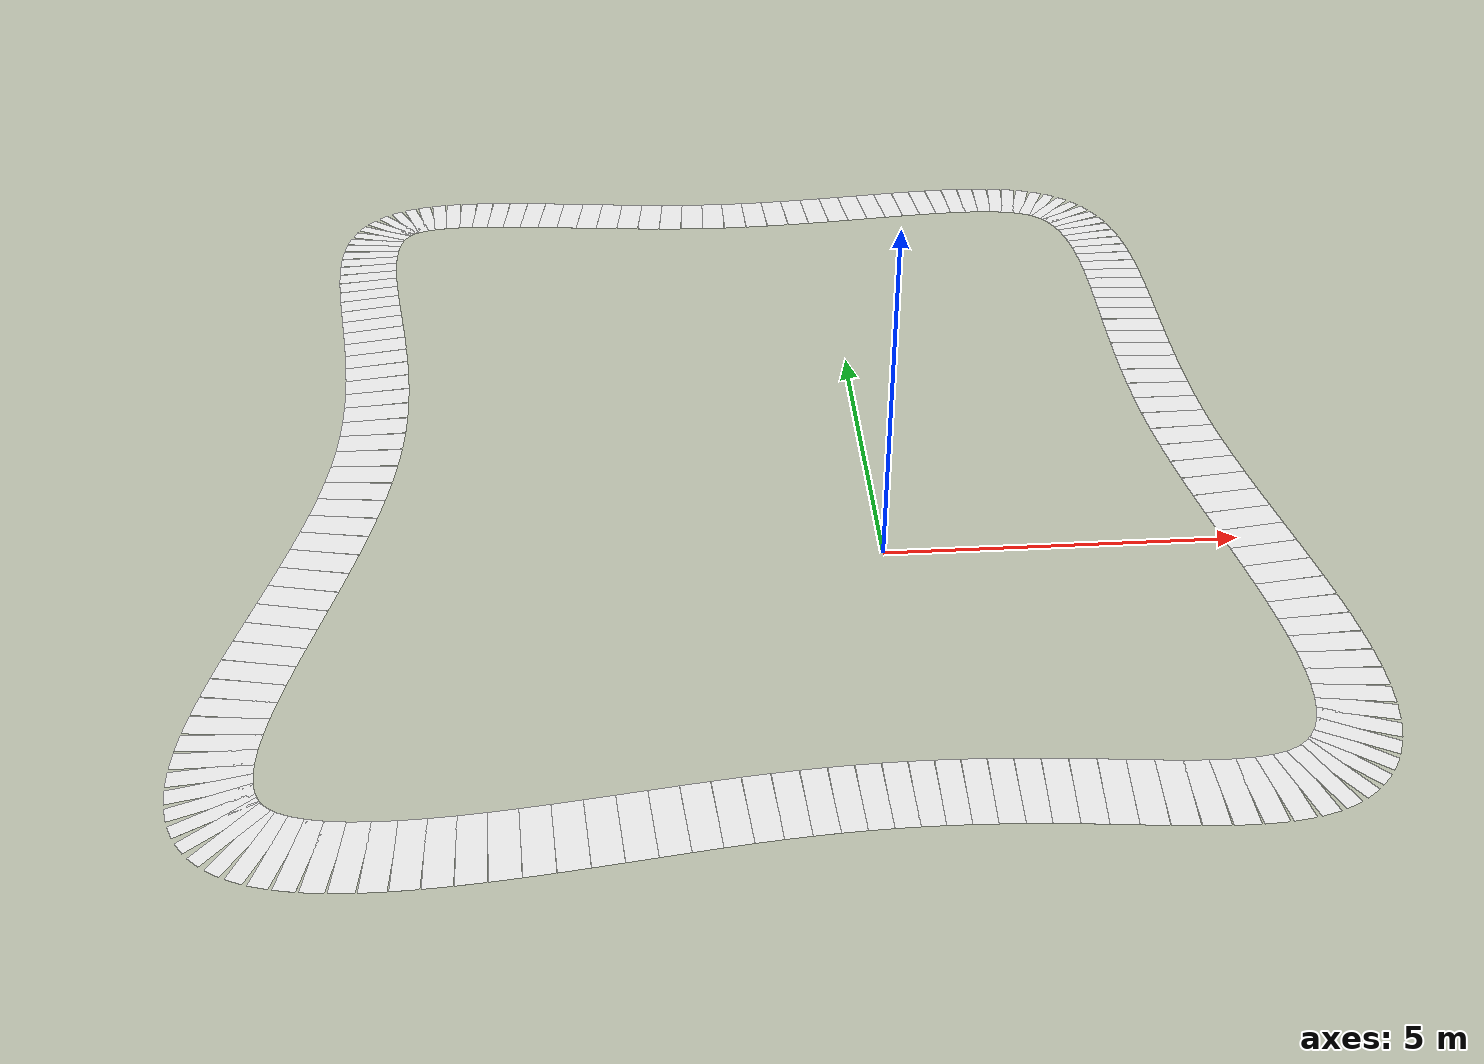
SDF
<sdf version='1.6'>
  <model name='road_model'>

    <model name='road_section_0'>
      <static>1</static>
      <link name='road_link'>
        <visual name='road_visual'>
          <geometry>
            <box>
              <size>0.197141 1 0.0001</size>
            </box>
          </geometry>
          <material>
            <ambient>0.8 0.8 0.8 1</ambient>
              <diffuse>1 1 1 1</diffuse>
              <specular>0 0 0 1</specular>
              <pbr>
                <metal>
                  <albedo_map>model://road_material/materials/textures/road_texture.jpg</albedo_map>
                  <metalness>0</metalness>
                  <roughness>0.8</roughness>
                </metal>
              </pbr>
          </material>
        </visual>
        <collision name='road_collision'>
          <geometry>
            <box>
              <size>0.197141 1 0.0001</size>
            </box>
          </geometry>
          <max_contacts>10</max_contacts>
          <surface>
            <contact>
              <ode/>
            </contact>
            <bounce/>
            <friction>
              <torsional>
                <ode/>
              </torsional>
              <ode/>
            </friction>
          </surface>
        </collision>
        <self_collide>0</self_collide>
        <enable_wind>0</enable_wind>
        <kinematic>0</kinematic>
      </link>
      <pose>4.57288 10.3336 0 0 0 -0.738724</pose>
    </model>

    <model name='road_section_1'>
      <static>1</static>
      <link name='road_link'>
        <visual name='road_visual'>
          <geometry>
            <box>
              <size>0.199153 1 0.0001</size>
            </box>
          </geometry>
          <material>
            <ambient>0.8 0.8 0.8 1</ambient>
              <diffuse>1 1 1 1</diffuse>
              <specular>0 0 0 1</specular>
              <pbr>
                <metal>
                  <albedo_map>model://road_material/materials/textures/road_texture.jpg</albedo_map>
                  <metalness>0</metalness>
                  <roughness>0.8</roughness>
                </metal>
              </pbr>
          </material>
        </visual>
        <collision name='road_collision'>
          <geometry>
            <box>
              <size>0.199153 1 0.0001</size>
            </box>
          </geometry>
          <max_contacts>10</max_contacts>
          <surface>
            <contact>
              <ode/>
            </contact>
            <bounce/>
            <friction>
              <torsional>
                <ode/>
              </torsional>
              <ode/>
            </friction>
          </surface>
        </collision>
        <self_collide>0</self_collide>
        <enable_wind>0</enable_wind>
        <kinematic>0</kinematic>
      </link>
      <pose>4.70788 10.1894 0 0 0 -0.897049</pose>
    </model>
    <model name='road_section_2'>
      <static>1</static>
      <link name='road_link'>
        <visual name='road_visual'>
          <geometry>
            <box>
              <size>0.205917 1 0.0001</size>
            </box>
          </geometry>
          <material>
            <ambient>0.8 0.8 0.8 1</ambient>
              <diffuse>1 1 1 1</diffuse>
              <specular>0 0 0 1</specular>
              <pbr>
                <metal>
                  <albedo_map>model://road_material/materials/textures/road_texture.jpg</albedo_map>
                  <metalness>0</metalness>
                  <roughness>0.8</roughness>
                </metal>
              </pbr>
          </material>
        </visual>
        <collision name='road_collision'>
          <geometry>
            <box>
              <size>0.205917 1 0.0001</size>
            </box>
          </geometry>
          <max_contacts>10</max_contacts>
          <surface>
            <contact>
              <ode/>
            </contact>
            <bounce/>
            <friction>
              <torsional>
                <ode/>
              </torsional>
              <ode/>
            </friction>
          </surface>
        </collision>
        <self_collide>0</self_collide>
        <enable_wind>0</enable_wind>
        <kinematic>0</kinematic>
      </link>
      <pose>4.82211 10.0228 0 0 0 -1.04016</pose>
    </model>
    <model name='road_section_3'>
      <static>1</static>
      <link name='road_link'>
        <visual name='road_visual'>
          <geometry>
            <box>
              <size>0.216306 1 0.0001</size>
            </box>
          </geometry>
          <material>
            <ambient>0.8 0.8 0.8 1</ambient>
              <diffuse>1 1 1 1</diffuse>
              <specular>0 0 0 1</specular>
              <pbr>
                <metal>
                  <albedo_map>model://road_material/materials/textures/road_texture.jpg</albedo_map>
                  <metalness>0</metalness>
                  <roughness>0.8</roughness>
                </metal>
              </pbr>
          </material>
        </visual>
        <collision name='road_collision'>
          <geometry>
            <box>
              <size>0.216306 1 0.0001</size>
            </box>
          </geometry>
          <max_contacts>10</max_contacts>
          <surface>
            <contact>
              <ode/>
            </contact>
            <bounce/>
            <friction>
              <torsional>
                <ode/>
              </torsional>
              <ode/>
            </friction>
          </surface>
        </collision>
        <self_collide>0</self_collide>
        <enable_wind>0</enable_wind>
        <kinematic>0</kinematic>
      </link>
      <pose>4.91703 9.8347 0 0 0 -1.16381</pose>
    </model>
    <model name='road_section_4'>
      <static>1</static>
      <link name='road_link'>
        <visual name='road_visual'>
          <geometry>
            <box>
              <size>0.229219 1 0.0001</size>
            </box>
          </geometry>
          <material>
            <ambient>0.8 0.8 0.8 1</ambient>
              <diffuse>1 1 1 1</diffuse>
              <specular>0 0 0 1</specular>
              <pbr>
                <metal>
                  <albedo_map>model://road_material/materials/textures/road_texture.jpg</albedo_map>
                  <metalness>0</metalness>
                  <roughness>0.8</roughness>
                </metal>
              </pbr>
          </material>
        </visual>
        <collision name='road_collision'>
          <geometry>
            <box>
              <size>0.229219 1 0.0001</size>
            </box>
          </geometry>
          <max_contacts>10</max_contacts>
          <surface>
            <contact>
              <ode/>
            </contact>
            <bounce/>
            <friction>
              <torsional>
                <ode/>
              </torsional>
              <ode/>
            </friction>
          </surface>
        </collision>
        <self_collide>0</self_collide>
        <enable_wind>0</enable_wind>
        <kinematic>0</kinematic>
      </link>
      <pose>4.99408 9.62601 0 0 0 -1.26738</pose>
    </model>
    <model name='road_section_5'>
      <static>1</static>
      <link name='road_link'>
        <visual name='road_visual'>
          <geometry>
            <box>
              <size>0.24372 1 0.0001</size>
            </box>
          </geometry>
          <material>
            <ambient>0.8 0.8 0.8 1</ambient>
              <diffuse>1 1 1 1</diffuse>
              <specular>0 0 0 1</specular>
              <pbr>
                <metal>
                  <albedo_map>model://road_material/materials/textures/road_texture.jpg</albedo_map>
                  <metalness>0</metalness>
                  <roughness>0.8</roughness>
                </metal>
              </pbr>
          </material>
        </visual>
        <collision name='road_collision'>
          <geometry>
            <box>
              <size>0.24372 1 0.0001</size>
            </box>
          </geometry>
          <max_contacts>10</max_contacts>
          <surface>
            <contact>
              <ode/>
            </contact>
            <bounce/>
            <friction>
              <torsional>
                <ode/>
              </torsional>
              <ode/>
            </friction>
          </surface>
        </collision>
        <self_collide>0</self_collide>
        <enable_wind>0</enable_wind>
        <kinematic>0</kinematic>
      </link>
      <pose>5.05473 9.39767 0 0 0 -1.35241</pose>
    </model>
    <model name='road_section_6'>
      <static>1</static>
      <link name='road_link'>
        <visual name='road_visual'>
          <geometry>
            <box>
              <size>0.259075 1 0.0001</size>
            </box>
          </geometry>
          <material>
            <ambient>0.8 0.8 0.8 1</ambient>
              <diffuse>1 1 1 1</diffuse>
              <specular>0 0 0 1</specular>
              <pbr>
                <metal>
                  <albedo_map>model://road_material/materials/textures/road_texture.jpg</albedo_map>
                  <metalness>0</metalness>
                  <roughness>0.8</roughness>
                </metal>
              </pbr>
          </material>
        </visual>
        <collision name='road_collision'>
          <geometry>
            <box>
              <size>0.259075 1 0.0001</size>
            </box>
          </geometry>
          <max_contacts>10</max_contacts>
          <surface>
            <contact>
              <ode/>
            </contact>
            <bounce/>
            <friction>
              <torsional>
                <ode/>
              </torsional>
              <ode/>
            </friction>
          </surface>
        </collision>
        <self_collide>0</self_collide>
        <enable_wind>0</enable_wind>
        <kinematic>0</kinematic>
      </link>
      <pose>5.10042 9.15061 0 0 0 -1.42135</pose>
    </model>
    <model name='road_section_7'>
      <static>1</static>
      <link name='road_link'>
        <visual name='road_visual'>
          <geometry>
            <box>
              <size>0.27473 1 0.0001</size>
            </box>
          </geometry>
          <material>
            <ambient>0.8 0.8 0.8 1</ambient>
              <diffuse>1 1 1 1</diffuse>
              <specular>0 0 0 1</specular>
              <pbr>
                <metal>
                  <albedo_map>model://road_material/materials/textures/road_texture.jpg</albedo_map>
                  <metalness>0</metalness>
                  <roughness>0.8</roughness>
                </metal>
              </pbr>
          </material>
        </visual>
        <collision name='road_collision'>
          <geometry>
            <box>
              <size>0.27473 1 0.0001</size>
            </box>
          </geometry>
          <max_contacts>10</max_contacts>
          <surface>
            <contact>
              <ode/>
            </contact>
            <bounce/>
            <friction>
              <torsional>
                <ode/>
              </torsional>
              <ode/>
            </friction>
          </surface>
        </collision>
        <self_collide>0</self_collide>
        <enable_wind>0</enable_wind>
        <kinematic>0</kinematic>
      </link>
      <pose>5.13261 8.88576 0 0 0 -1.47675</pose>
    </model>
    <model name='road_section_8'>
      <static>1</static>
      <link name='road_link'>
        <visual name='road_visual'>
          <geometry>
            <box>
              <size>0.290279 1 0.0001</size>
            </box>
          </geometry>
          <material>
            <ambient>0.8 0.8 0.8 1</ambient>
              <diffuse>1 1 1 1</diffuse>
              <specular>0 0 0 1</specular>
              <pbr>
                <metal>
                  <albedo_map>model://road_material/materials/textures/road_texture.jpg</albedo_map>
                  <metalness>0</metalness>
                  <roughness>0.8</roughness>
                </metal>
              </pbr>
          </material>
        </visual>
        <collision name='road_collision'>
          <geometry>
            <box>
              <size>0.290279 1 0.0001</size>
            </box>
          </geometry>
          <max_contacts>10</max_contacts>
          <surface>
            <contact>
              <ode/>
            </contact>
            <bounce/>
            <friction>
              <torsional>
                <ode/>
              </torsional>
              <ode/>
            </friction>
          </surface>
        </collision>
        <self_collide>0</self_collide>
        <enable_wind>0</enable_wind>
        <kinematic>0</kinematic>
      </link>
      <pose>5.15275 8.60404 0 0 0 -1.5209</pose>
    </model>
    <model name='road_section_9'>
      <static>1</static>
      <link name='road_link'>
        <visual name='road_visual'>
          <geometry>
            <box>
              <size>0.305427 1 0.0001</size>
            </box>
          </geometry>
          <material>
            <ambient>0.8 0.8 0.8 1</ambient>
              <diffuse>1 1 1 1</diffuse>
              <specular>0 0 0 1</specular>
              <pbr>
                <metal>
                  <albedo_map>model://road_material/materials/textures/road_texture.jpg</albedo_map>
                  <metalness>0</metalness>
                  <roughness>0.8</roughness>
                </metal>
              </pbr>
          </material>
        </visual>
        <collision name='road_collision'>
          <geometry>
            <box>
              <size>0.305427 1 0.0001</size>
            </box>
          </geometry>
          <max_contacts>10</max_contacts>
          <surface>
            <contact>
              <ode/>
            </contact>
            <bounce/>
            <friction>
              <torsional>
                <ode/>
              </torsional>
              <ode/>
            </friction>
          </surface>
        </collision>
        <self_collide>0</self_collide>
        <enable_wind>0</enable_wind>
        <kinematic>0</kinematic>
      </link>
      <pose>5.16229 8.30639 0 0 0 -1.5557</pose>
    </model>
    <model name='road_section_10'>
      <static>1</static>
      <link name='road_link'>
        <visual name='road_visual'>
          <geometry>
            <box>
              <size>0.319962 1 0.0001</size>
            </box>
          </geometry>
          <material>
            <ambient>0.8 0.8 0.8 1</ambient>
              <diffuse>1 1 1 1</diffuse>
              <specular>0 0 0 1</specular>
              <pbr>
                <metal>
                  <albedo_map>model://road_material/materials/textures/road_texture.jpg</albedo_map>
                  <metalness>0</metalness>
                  <roughness>0.8</roughness>
                </metal>
              </pbr>
          </material>
        </visual>
        <collision name='road_collision'>
          <geometry>
            <box>
              <size>0.319962 1 0.0001</size>
            </box>
          </geometry>
          <max_contacts>10</max_contacts>
          <surface>
            <contact>
              <ode/>
            </contact>
            <bounce/>
            <friction>
              <torsional>
                <ode/>
              </torsional>
              <ode/>
            </friction>
          </surface>
        </collision>
        <self_collide>0</self_collide>
        <enable_wind>0</enable_wind>
        <kinematic>0</kinematic>
      </link>
      <pose>5.16269 7.99372 0 0 0 -1.58269</pose>
    </model>
    <model name='road_section_11'>
      <static>1</static>
      <link name='road_link'>
        <visual name='road_visual'>
          <geometry>
            <box>
              <size>0.333733 1 0.0001</size>
            </box>
          </geometry>
          <material>
            <ambient>0.8 0.8 0.8 1</ambient>
              <diffuse>1 1 1 1</diffuse>
              <specular>0 0 0 1</specular>
              <pbr>
                <metal>
                  <albedo_map>model://road_material/materials/textures/road_texture.jpg</albedo_map>
                  <metalness>0</metalness>
                  <roughness>0.8</roughness>
                </metal>
              </pbr>
          </material>
        </visual>
        <collision name='road_collision'>
          <geometry>
            <box>
              <size>0.333733 1 0.0001</size>
            </box>
          </geometry>
          <max_contacts>10</max_contacts>
          <surface>
            <contact>
              <ode/>
            </contact>
            <bounce/>
            <friction>
              <torsional>
                <ode/>
              </torsional>
              <ode/>
            </friction>
          </surface>
        </collision>
        <self_collide>0</self_collide>
        <enable_wind>0</enable_wind>
        <kinematic>0</kinematic>
      </link>
      <pose>5.1554 7.66697 0 0 0 -1.60307</pose>
    </model>
    <model name='road_section_12'>
      <static>1</static>
      <link name='road_link'>
        <visual name='road_visual'>
          <geometry>
            <box>
              <size>0.346634 1 0.0001</size>
            </box>
          </geometry>
          <material>
            <ambient>0.8 0.8 0.8 1</ambient>
              <diffuse>1 1 1 1</diffuse>
              <specular>0 0 0 1</specular>
              <pbr>
                <metal>
                  <albedo_map>model://road_material/materials/textures/road_texture.jpg</albedo_map>
                  <metalness>0</metalness>
                  <roughness>0.8</roughness>
                </metal>
              </pbr>
          </material>
        </visual>
        <collision name='road_collision'>
          <geometry>
            <box>
              <size>0.346634 1 0.0001</size>
            </box>
          </geometry>
          <max_contacts>10</max_contacts>
          <surface>
            <contact>
              <ode/>
            </contact>
            <bounce/>
            <friction>
              <torsional>
                <ode/>
              </torsional>
              <ode/>
            </friction>
          </surface>
        </collision>
        <self_collide>0</self_collide>
        <enable_wind>0</enable_wind>
        <kinematic>0</kinematic>
      </link>
      <pose>5.14188 7.32707 0 0 0 -1.61777</pose>
    </model>
    <model name='road_section_13'>
      <static>1</static>
      <link name='road_link'>
        <visual name='road_visual'>
          <geometry>
            <box>
              <size>0.358594 1 0.0001</size>
            </box>
          </geometry>
          <material>
            <ambient>0.8 0.8 0.8 1</ambient>
              <diffuse>1 1 1 1</diffuse>
              <specular>0 0 0 1</specular>
              <pbr>
                <metal>
                  <albedo_map>model://road_material/materials/textures/road_texture.jpg</albedo_map>
                  <metalness>0</metalness>
                  <roughness>0.8</roughness>
                </metal>
              </pbr>
          </material>
        </visual>
        <collision name='road_collision'>
          <geometry>
            <box>
              <size>0.358594 1 0.0001</size>
            </box>
          </geometry>
          <max_contacts>10</max_contacts>
          <surface>
            <contact>
              <ode/>
            </contact>
            <bounce/>
            <friction>
              <torsional>
                <ode/>
              </torsional>
              <ode/>
            </friction>
          </surface>
        </collision>
        <self_collide>0</self_collide>
        <enable_wind>0</enable_wind>
        <kinematic>0</kinematic>
      </link>
      <pose>5.12358 6.97493 0 0 0 -1.62752</pose>
    </model>
    <model name='road_section_14'>
      <static>1</static>
      <link name='road_link'>
        <visual name='road_visual'>
          <geometry>
            <box>
              <size>0.369568 1 0.0001</size>
            </box>
          </geometry>
          <material>
            <ambient>0.8 0.8 0.8 1</ambient>
              <diffuse>1 1 1 1</diffuse>
              <specular>0 0 0 1</specular>
              <pbr>
                <metal>
                  <albedo_map>model://road_material/materials/textures/road_texture.jpg</albedo_map>
                  <metalness>0</metalness>
                  <roughness>0.8</roughness>
                </metal>
              </pbr>
          </material>
        </visual>
        <collision name='road_collision'>
          <geometry>
            <box>
              <size>0.369568 1 0.0001</size>
            </box>
          </geometry>
          <max_contacts>10</max_contacts>
          <surface>
            <contact>
              <ode/>
            </contact>
            <bounce/>
            <friction>
              <torsional>
                <ode/>
              </torsional>
              <ode/>
            </friction>
          </surface>
        </collision>
        <self_collide>0</self_collide>
        <enable_wind>0</enable_wind>
        <kinematic>0</kinematic>
      </link>
      <pose>5.10195 6.6115 0 0 0 -1.63288</pose>
    </model>
    <model name='road_section_15'>
      <static>1</static>
      <link name='road_link'>
        <visual name='road_visual'>
          <geometry>
            <box>
              <size>0.379531 1 0.0001</size>
            </box>
          </geometry>
          <material>
            <ambient>0.8 0.8 0.8 1</ambient>
              <diffuse>1 1 1 1</diffuse>
              <specular>0 0 0 1</specular>
              <pbr>
                <metal>
                  <albedo_map>model://road_material/materials/textures/road_texture.jpg</albedo_map>
                  <metalness>0</metalness>
                  <roughness>0.8</roughness>
                </metal>
              </pbr>
          </material>
        </visual>
        <collision name='road_collision'>
          <geometry>
            <box>
              <size>0.379531 1 0.0001</size>
            </box>
          </geometry>
          <max_contacts>10</max_contacts>
          <surface>
            <contact>
              <ode/>
            </contact>
            <bounce/>
            <friction>
              <torsional>
                <ode/>
              </torsional>
              <ode/>
            </friction>
          </surface>
        </collision>
        <self_collide>0</self_collide>
        <enable_wind>0</enable_wind>
        <kinematic>0</kinematic>
      </link>
      <pose>5.07845 6.23769 0 0 0 -1.63428</pose>
    </model>
    <model name='road_section_16'>
      <static>1</static>
      <link name='road_link'>
        <visual name='road_visual'>
          <geometry>
            <box>
              <size>0.388479 1 0.0001</size>
            </box>
          </geometry>
          <material>
            <ambient>0.8 0.8 0.8 1</ambient>
              <diffuse>1 1 1 1</diffuse>
              <specular>0 0 0 1</specular>
              <pbr>
                <metal>
                  <albedo_map>model://road_material/materials/textures/road_texture.jpg</albedo_map>
                  <metalness>0</metalness>
                  <roughness>0.8</roughness>
                </metal>
              </pbr>
          </material>
        </visual>
        <collision name='road_collision'>
          <geometry>
            <box>
              <size>0.388479 1 0.0001</size>
            </box>
          </geometry>
          <max_contacts>10</max_contacts>
          <surface>
            <contact>
              <ode/>
            </contact>
            <bounce/>
            <friction>
              <torsional>
                <ode/>
              </torsional>
              <ode/>
            </friction>
          </surface>
        </collision>
        <self_collide>0</self_collide>
        <enable_wind>0</enable_wind>
        <kinematic>0</kinematic>
      </link>
      <pose>5.05452 5.85443 0 0 0 -1.63203</pose>
    </model>
    <model name='road_section_17'>
      <static>1</static>
      <link name='road_link'>
        <visual name='road_visual'>
          <geometry>
            <box>
              <size>0.396419 1 0.0001</size>
            </box>
          </geometry>
          <material>
            <ambient>0.8 0.8 0.8 1</ambient>
              <diffuse>1 1 1 1</diffuse>
              <specular>0 0 0 1</specular>
              <pbr>
                <metal>
                  <albedo_map>model://road_material/materials/textures/road_texture.jpg</albedo_map>
                  <metalness>0</metalness>
                  <roughness>0.8</roughness>
                </metal>
              </pbr>
          </material>
        </visual>
        <collision name='road_collision'>
          <geometry>
            <box>
              <size>0.396419 1 0.0001</size>
            </box>
          </geometry>
          <max_contacts>10</max_contacts>
          <surface>
            <contact>
              <ode/>
            </contact>
            <bounce/>
            <friction>
              <torsional>
                <ode/>
              </torsional>
              <ode/>
            </friction>
          </surface>
        </collision>
        <self_collide>0</self_collide>
        <enable_wind>0</enable_wind>
        <kinematic>0</kinematic>
      </link>
      <pose>5.03163 5.46265 0 0 0 -1.62635</pose>
    </model>
    <model name='road_section_18'>
      <static>1</static>
      <link name='road_link'>
        <visual name='road_visual'>
          <geometry>
            <box>
              <size>0.403375 1 0.0001</size>
            </box>
          </geometry>
          <material>
            <ambient>0.8 0.8 0.8 1</ambient>
              <diffuse>1 1 1 1</diffuse>
              <specular>0 0 0 1</specular>
              <pbr>
                <metal>
                  <albedo_map>model://road_material/materials/textures/road_texture.jpg</albedo_map>
                  <metalness>0</metalness>
                  <roughness>0.8</roughness>
                </metal>
              </pbr>
          </material>
        </visual>
        <collision name='road_collision'>
          <geometry>
            <box>
              <size>0.403375 1 0.0001</size>
            </box>
          </geometry>
          <max_contacts>10</max_contacts>
          <surface>
            <contact>
              <ode/>
            </contact>
            <bounce/>
            <friction>
              <torsional>
                <ode/>
              </torsional>
              <ode/>
            </friction>
          </surface>
        </collision>
        <self_collide>0</self_collide>
        <enable_wind>0</enable_wind>
        <kinematic>0</kinematic>
      </link>
      <pose>5.01122 5.06328 0 0 0 -1.61742</pose>
    </model>
    <model name='road_section_19'>
      <static>1</static>
      <link name='road_link'>
        <visual name='road_visual'>
          <geometry>
            <box>
              <size>0.409383 1 0.0001</size>
            </box>
          </geometry>
          <material>
            <ambient>0.8 0.8 0.8 1</ambient>
              <diffuse>1 1 1 1</diffuse>
              <specular>0 0 0 1</specular>
              <pbr>
                <metal>
                  <albedo_map>model://road_material/materials/textures/road_texture.jpg</albedo_map>
                  <metalness>0</metalness>
                  <roughness>0.8</roughness>
                </metal>
              </pbr>
          </material>
        </visual>
        <collision name='road_collision'>
          <geometry>
            <box>
              <size>0.409383 1 0.0001</size>
            </box>
          </geometry>
          <max_contacts>10</max_contacts>
          <surface>
            <contact>
              <ode/>
            </contact>
            <bounce/>
            <friction>
              <torsional>
                <ode/>
              </torsional>
              <ode/>
            </friction>
          </surface>
        </collision>
        <self_collide>0</self_collide>
        <enable_wind>0</enable_wind>
        <kinematic>0</kinematic>
      </link>
      <pose>4.99476 4.65724 0 0 0 -1.60533</pose>
    </model>
    <model name='road_section_20'>
      <static>1</static>
      <link name='road_link'>
        <visual name='road_visual'>
          <geometry>
            <box>
              <size>0.414492 1 0.0001</size>
            </box>
          </geometry>
          <material>
            <ambient>0.8 0.8 0.8 1</ambient>
              <diffuse>1 1 1 1</diffuse>
              <specular>0 0 0 1</specular>
              <pbr>
                <metal>
                  <albedo_map>model://road_material/materials/textures/road_texture.jpg</albedo_map>
                  <metalness>0</metalness>
                  <roughness>0.8</roughness>
                </metal>
              </pbr>
          </material>
        </visual>
        <collision name='road_collision'>
          <geometry>
            <box>
              <size>0.414492 1 0.0001</size>
            </box>
          </geometry>
          <max_contacts>10</max_contacts>
          <surface>
            <contact>
              <ode/>
            </contact>
            <bounce/>
            <friction>
              <torsional>
                <ode/>
              </torsional>
              <ode/>
            </friction>
          </surface>
        </collision>
        <self_collide>0</self_collide>
        <enable_wind>0</enable_wind>
        <kinematic>0</kinematic>
      </link>
      <pose>4.98368 4.24546 0 0 0 -1.59013</pose>
    </model>
    <model name='road_section_21'>
      <static>1</static>
      <link name='road_link'>
        <visual name='road_visual'>
          <geometry>
            <box>
              <size>0.418762 1 0.0001</size>
            </box>
          </geometry>
          <material>
            <ambient>0.8 0.8 0.8 1</ambient>
              <diffuse>1 1 1 1</diffuse>
              <specular>0 0 0 1</specular>
              <pbr>
                <metal>
                  <albedo_map>model://road_material/materials/textures/road_texture.jpg</albedo_map>
                  <metalness>0</metalness>
                  <roughness>0.8</roughness>
                </metal>
              </pbr>
          </material>
        </visual>
        <collision name='road_collision'>
          <geometry>
            <box>
              <size>0.418762 1 0.0001</size>
            </box>
          </geometry>
          <max_contacts>10</max_contacts>
          <surface>
            <contact>
              <ode/>
            </contact>
            <bounce/>
            <friction>
              <torsional>
                <ode/>
              </torsional>
              <ode/>
            </friction>
          </surface>
        </collision>
        <self_collide>0</self_collide>
        <enable_wind>0</enable_wind>
        <kinematic>0</kinematic>
      </link>
      <pose>4.97946 3.82887 0 0 0 -1.57184</pose>
    </model>
    <model name='road_section_22'>
      <static>1</static>
      <link name='road_link'>
        <visual name='road_visual'>
          <geometry>
            <box>
              <size>0.42227 1 0.0001</size>
            </box>
          </geometry>
          <material>
            <ambient>0.8 0.8 0.8 1</ambient>
              <diffuse>1 1 1 1</diffuse>
              <specular>0 0 0 1</specular>
              <pbr>
                <metal>
                  <albedo_map>model://road_material/materials/textures/road_texture.jpg</albedo_map>
                  <metalness>0</metalness>
                  <roughness>0.8</roughness>
                </metal>
              </pbr>
          </material>
        </visual>
        <collision name='road_collision'>
          <geometry>
            <box>
              <size>0.42227 1 0.0001</size>
            </box>
          </geometry>
          <max_contacts>10</max_contacts>
          <surface>
            <contact>
              <ode/>
            </contact>
            <bounce/>
            <friction>
              <torsional>
                <ode/>
              </torsional>
              <ode/>
            </friction>
          </surface>
        </collision>
        <self_collide>0</self_collide>
        <enable_wind>0</enable_wind>
        <kinematic>0</kinematic>
      </link>
      <pose>4.98353 3.4084 0 0 0 -1.55046</pose>
    </model>
    <model name='road_section_23'>
      <static>1</static>
      <link name='road_link'>
        <visual name='road_visual'>
          <geometry>
            <box>
              <size>0.425101 1 0.0001</size>
            </box>
          </geometry>
          <material>
            <ambient>0.8 0.8 0.8 1</ambient>
              <diffuse>1 1 1 1</diffuse>
              <specular>0 0 0 1</specular>
              <pbr>
                <metal>
                  <albedo_map>model://road_material/materials/textures/road_texture.jpg</albedo_map>
                  <metalness>0</metalness>
                  <roughness>0.8</roughness>
                </metal>
              </pbr>
          </material>
        </visual>
        <collision name='road_collision'>
          <geometry>
            <box>
              <size>0.425101 1 0.0001</size>
            </box>
          </geometry>
          <max_contacts>10</max_contacts>
          <surface>
            <contact>
              <ode/>
            </contact>
            <bounce/>
            <friction>
              <torsional>
                <ode/>
              </torsional>
              <ode/>
            </friction>
          </surface>
        </collision>
        <self_collide>0</self_collide>
        <enable_wind>0</enable_wind>
        <kinematic>0</kinematic>
      </link>
      <pose>4.99735 2.98497 0 0 0 -1.52596</pose>
    </model>
    <model name='road_section_24'>
      <static>1</static>
      <link name='road_link'>
        <visual name='road_visual'>
          <geometry>
            <box>
              <size>0.427101 1 0.0001</size>
            </box>
          </geometry>
          <material>
            <ambient>0.8 0.8 0.8 1</ambient>
              <diffuse>1 1 1 1</diffuse>
              <specular>0 0 0 1</specular>
              <pbr>
                <metal>
                  <albedo_map>model://road_material/materials/textures/road_texture.jpg</albedo_map>
                  <metalness>0</metalness>
                  <roughness>0.8</roughness>
                </metal>
              </pbr>
          </material>
        </visual>
        <collision name='road_collision'>
          <geometry>
            <box>
              <size>0.427101 1 0.0001</size>
            </box>
          </geometry>
          <max_contacts>10</max_contacts>
          <surface>
            <contact>
              <ode/>
            </contact>
            <bounce/>
            <friction>
              <torsional>
                <ode/>
              </torsional>
              <ode/>
            </friction>
          </surface>
        </collision>
        <self_collide>0</self_collide>
        <enable_wind>0</enable_wind>
        <kinematic>0</kinematic>
      </link>
      <pose>5.02177 2.5596 0 0 0 -1.50102</pose>
    </model>
    <model name='road_section_25'>
      <static>1</static>
      <link name='road_link'>
        <visual name='road_visual'>
          <geometry>
            <box>
              <size>0.427807 1 0.0001</size>
            </box>
          </geometry>
          <material>
            <ambient>0.8 0.8 0.8 1</ambient>
              <diffuse>1 1 1 1</diffuse>
              <specular>0 0 0 1</specular>
              <pbr>
                <metal>
                  <albedo_map>model://road_material/materials/textures/road_texture.jpg</albedo_map>
                  <metalness>0</metalness>
                  <roughness>0.8</roughness>
                </metal>
              </pbr>
          </material>
        </visual>
        <collision name='road_collision'>
          <geometry>
            <box>
              <size>0.427807 1 0.0001</size>
            </box>
          </geometry>
          <max_contacts>10</max_contacts>
          <surface>
            <contact>
              <ode/>
            </contact>
            <bounce/>
            <friction>
              <torsional>
                <ode/>
              </torsional>
              <ode/>
            </friction>
          </surface>
        </collision>
        <self_collide>0</self_collide>
        <enable_wind>0</enable_wind>
        <kinematic>0</kinematic>
      </link>
      <pose>5.05603 2.13355 0 0 0 -1.48009</pose>
    </model>
    <model name='road_section_26'>
      <static>1</static>
      <link name='road_link'>
        <visual name='road_visual'>
          <geometry>
            <box>
              <size>0.427068 1 0.0001</size>
            </box>
          </geometry>
          <material>
            <ambient>0.8 0.8 0.8 1</ambient>
              <diffuse>1 1 1 1</diffuse>
              <specular>0 0 0 1</specular>
              <pbr>
                <metal>
                  <albedo_map>model://road_material/materials/textures/road_texture.jpg</albedo_map>
                  <metalness>0</metalness>
                  <roughness>0.8</roughness>
                </metal>
              </pbr>
          </material>
        </visual>
        <collision name='road_collision'>
          <geometry>
            <box>
              <size>0.427068 1 0.0001</size>
            </box>
          </geometry>
          <max_contacts>10</max_contacts>
          <surface>
            <contact>
              <ode/>
            </contact>
            <bounce/>
            <friction>
              <torsional>
                <ode/>
              </torsional>
              <ode/>
            </friction>
          </surface>
        </collision>
        <self_collide>0</self_collide>
        <enable_wind>0</enable_wind>
        <kinematic>0</kinematic>
      </link>
      <pose>5.0983 1.70822 0 0 0 -1.46339</pose>
    </model>
    <model name='road_section_27'>
      <static>1</static>
      <link name='road_link'>
        <visual name='road_visual'>
          <geometry>
            <box>
              <size>0.424794 1 0.0001</size>
            </box>
          </geometry>
          <material>
            <ambient>0.8 0.8 0.8 1</ambient>
              <diffuse>1 1 1 1</diffuse>
              <specular>0 0 0 1</specular>
              <pbr>
                <metal>
                  <albedo_map>model://road_material/materials/textures/road_texture.jpg</albedo_map>
                  <metalness>0</metalness>
                  <roughness>0.8</roughness>
                </metal>
              </pbr>
          </material>
        </visual>
        <collision name='road_collision'>
          <geometry>
            <box>
              <size>0.424794 1 0.0001</size>
            </box>
          </geometry>
          <max_contacts>10</max_contacts>
          <surface>
            <contact>
              <ode/>
            </contact>
            <bounce/>
            <friction>
              <torsional>
                <ode/>
              </torsional>
              <ode/>
            </friction>
          </surface>
        </collision>
        <self_collide>0</self_collide>
        <enable_wind>0</enable_wind>
        <kinematic>0</kinematic>
      </link>
      <pose>5.14662 1.28505 0 0 0 -1.45076</pose>
    </model>
    <model name='road_section_28'>
      <static>1</static>
      <link name='road_link'>
        <visual name='road_visual'>
          <geometry>
            <box>
              <size>0.420918 1 0.0001</size>
            </box>
          </geometry>
          <material>
            <ambient>0.8 0.8 0.8 1</ambient>
              <diffuse>1 1 1 1</diffuse>
              <specular>0 0 0 1</specular>
              <pbr>
                <metal>
                  <albedo_map>model://road_material/materials/textures/road_texture.jpg</albedo_map>
                  <metalness>0</metalness>
                  <roughness>0.8</roughness>
                </metal>
              </pbr>
          </material>
        </visual>
        <collision name='road_collision'>
          <geometry>
            <box>
              <size>0.420918 1 0.0001</size>
            </box>
          </geometry>
          <max_contacts>10</max_contacts>
          <surface>
            <contact>
              <ode/>
            </contact>
            <bounce/>
            <friction>
              <torsional>
                <ode/>
              </torsional>
              <ode/>
            </friction>
          </surface>
        </collision>
        <self_collide>0</self_collide>
        <enable_wind>0</enable_wind>
        <kinematic>0</kinematic>
      </link>
      <pose>5.19906 0.865461 0 0 0 -1.44212</pose>
    </model>
    <model name='road_section_29'>
      <static>1</static>
      <link name='road_link'>
        <visual name='road_visual'>
          <geometry>
            <box>
              <size>0.415396 1 0.0001</size>
            </box>
          </geometry>
          <material>
            <ambient>0.8 0.8 0.8 1</ambient>
              <diffuse>1 1 1 1</diffuse>
              <specular>0 0 0 1</specular>
              <pbr>
                <metal>
                  <albedo_map>model://road_material/materials/textures/road_texture.jpg</albedo_map>
                  <metalness>0</metalness>
                  <roughness>0.8</roughness>
                </metal>
              </pbr>
          </material>
        </visual>
        <collision name='road_collision'>
          <geometry>
            <box>
              <size>0.415396 1 0.0001</size>
            </box>
          </geometry>
          <max_contacts>10</max_contacts>
          <surface>
            <contact>
              <ode/>
            </contact>
            <bounce/>
            <friction>
              <torsional>
                <ode/>
              </torsional>
              <ode/>
            </friction>
          </surface>
        </collision>
        <self_collide>0</self_collide>
        <enable_wind>0</enable_wind>
        <kinematic>0</kinematic>
      </link>
      <pose>5.25367 0.450887 0 0 0 -1.43748</pose>
    </model>
    <model name='road_section_30'>
      <static>1</static>
      <link name='road_link'>
        <visual name='road_visual'>
          <geometry>
            <box>
              <size>0.408204 1 0.0001</size>
            </box>
          </geometry>
          <material>
            <ambient>0.8 0.8 0.8 1</ambient>
              <diffuse>1 1 1 1</diffuse>
              <specular>0 0 0 1</specular>
              <pbr>
                <metal>
                  <albedo_map>model://road_material/materials/textures/road_texture.jpg</albedo_map>
                  <metalness>0</metalness>
                  <roughness>0.8</roughness>
                </metal>
              </pbr>
          </material>
        </visual>
        <collision name='road_collision'>
          <geometry>
            <box>
              <size>0.408204 1 0.0001</size>
            </box>
          </geometry>
          <max_contacts>10</max_contacts>
          <surface>
            <contact>
              <ode/>
            </contact>
            <bounce/>
            <friction>
              <torsional>
                <ode/>
              </torsional>
              <ode/>
            </friction>
          </surface>
        </collision>
        <self_collide>0</self_collide>
        <enable_wind>0</enable_wind>
        <kinematic>0</kinematic>
      </link>
      <pose>5.30852 0.042755 0 0 0 -1.43696</pose>
    </model>
    <model name='road_section_31'>
      <static>1</static>
      <link name='road_link'>
        <visual name='road_visual'>
          <geometry>
            <box>
              <size>0.39934 1 0.0001</size>
            </box>
          </geometry>
          <material>
            <ambient>0.8 0.8 0.8 1</ambient>
              <diffuse>1 1 1 1</diffuse>
              <specular>0 0 0 1</specular>
              <pbr>
                <metal>
                  <albedo_map>model://road_material/materials/textures/road_texture.jpg</albedo_map>
                  <metalness>0</metalness>
                  <roughness>0.8</roughness>
                </metal>
              </pbr>
          </material>
        </visual>
        <collision name='road_collision'>
          <geometry>
            <box>
              <size>0.39934 1 0.0001</size>
            </box>
          </geometry>
          <max_contacts>10</max_contacts>
          <surface>
            <contact>
              <ode/>
            </contact>
            <bounce/>
            <friction>
              <torsional>
                <ode/>
              </torsional>
              <ode/>
            </friction>
          </surface>
        </collision>
        <self_collide>0</self_collide>
        <enable_wind>0</enable_wind>
        <kinematic>0</kinematic>
      </link>
      <pose>5.36165 -0.357506 0 0 0 -1.44075</pose>
    </model>
    <model name='road_section_32'>
      <static>1</static>
      <link name='road_link'>
        <visual name='road_visual'>
          <geometry>
            <box>
              <size>0.388824 1 0.0001</size>
            </box>
          </geometry>
          <material>
            <ambient>0.8 0.8 0.8 1</ambient>
              <diffuse>1 1 1 1</diffuse>
              <specular>0 0 0 1</specular>
              <pbr>
                <metal>
                  <albedo_map>model://road_material/materials/textures/road_texture.jpg</albedo_map>
                  <metalness>0</metalness>
                  <roughness>0.8</roughness>
                </metal>
              </pbr>
          </material>
        </visual>
        <collision name='road_collision'>
          <geometry>
            <box>
              <size>0.388824 1 0.0001</size>
            </box>
          </geometry>
          <max_contacts>10</max_contacts>
          <surface>
            <contact>
              <ode/>
            </contact>
            <bounce/>
            <friction>
              <torsional>
                <ode/>
              </torsional>
              <ode/>
            </friction>
          </surface>
        </collision>
        <self_collide>0</self_collide>
        <enable_wind>0</enable_wind>
        <kinematic>0</kinematic>
      </link>
      <pose>5.41112 -0.748467 0 0 0 -1.44921</pose>
    </model>
    <model name='road_section_33'>
      <static>1</static>
      <link name='road_link'>
        <visual name='road_visual'>
          <geometry>
            <box>
              <size>0.376704 1 0.0001</size>
            </box>
          </geometry>
          <material>
            <ambient>0.8 0.8 0.8 1</ambient>
              <diffuse>1 1 1 1</diffuse>
              <specular>0 0 0 1</specular>
              <pbr>
                <metal>
                  <albedo_map>model://road_material/materials/textures/road_texture.jpg</albedo_map>
                  <metalness>0</metalness>
                  <roughness>0.8</roughness>
                </metal>
              </pbr>
          </material>
        </visual>
        <collision name='road_collision'>
          <geometry>
            <box>
              <size>0.376704 1 0.0001</size>
            </box>
          </geometry>
          <max_contacts>10</max_contacts>
          <surface>
            <contact>
              <ode/>
            </contact>
            <bounce/>
            <friction>
              <torsional>
                <ode/>
              </torsional>
              <ode/>
            </friction>
          </surface>
        </collision>
        <self_collide>0</self_collide>
        <enable_wind>0</enable_wind>
        <kinematic>0</kinematic>
      </link>
      <pose>5.45499 -1.1287 0 0 0 -1.46285</pose>
    </model>
    <model name='road_section_34'>
      <static>1</static>
      <link name='road_link'>
        <visual name='road_visual'>
          <geometry>
            <box>
              <size>0.363058 1 0.0001</size>
            </box>
          </geometry>
          <material>
            <ambient>0.8 0.8 0.8 1</ambient>
              <diffuse>1 1 1 1</diffuse>
              <specular>0 0 0 1</specular>
              <pbr>
                <metal>
                  <albedo_map>model://road_material/materials/textures/road_texture.jpg</albedo_map>
                  <metalness>0</metalness>
                  <roughness>0.8</roughness>
                </metal>
              </pbr>
          </material>
        </visual>
        <collision name='road_collision'>
          <geometry>
            <box>
              <size>0.363058 1 0.0001</size>
            </box>
          </geometry>
          <max_contacts>10</max_contacts>
          <surface>
            <contact>
              <ode/>
            </contact>
            <bounce/>
            <friction>
              <torsional>
                <ode/>
              </torsional>
              <ode/>
            </friction>
          </surface>
        </collision>
        <self_collide>0</self_collide>
        <enable_wind>0</enable_wind>
        <kinematic>0</kinematic>
      </link>
      <pose>5.49132 -1.49677 0 0 0 -1.48234</pose>
    </model>
    <model name='road_section_35'>
      <static>1</static>
      <link name='road_link'>
        <visual name='road_visual'>
          <geometry>
            <box>
              <size>0.34801 1 0.0001</size>
            </box>
          </geometry>
          <material>
            <ambient>0.8 0.8 0.8 1</ambient>
              <diffuse>1 1 1 1</diffuse>
              <specular>0 0 0 1</specular>
              <pbr>
                <metal>
                  <albedo_map>model://road_material/materials/textures/road_texture.jpg</albedo_map>
                  <metalness>0</metalness>
                  <roughness>0.8</roughness>
                </metal>
              </pbr>
          </material>
        </visual>
        <collision name='road_collision'>
          <geometry>
            <box>
              <size>0.34801 1 0.0001</size>
            </box>
          </geometry>
          <max_contacts>10</max_contacts>
          <surface>
            <contact>
              <ode/>
            </contact>
            <bounce/>
            <friction>
              <torsional>
                <ode/>
              </torsional>
              <ode/>
            </friction>
          </surface>
        </collision>
        <self_collide>0</self_collide>
        <enable_wind>0</enable_wind>
        <kinematic>0</kinematic>
      </link>
      <pose>5.51816 -1.85126 0 0 0 -1.50865</pose>
    </model>
    <model name='road_section_36'>
      <static>1</static>
      <link name='road_link'>
        <visual name='road_visual'>
          <geometry>
            <box>
              <size>0.331737 1 0.0001</size>
            </box>
          </geometry>
          <material>
            <ambient>0.8 0.8 0.8 1</ambient>
              <diffuse>1 1 1 1</diffuse>
              <specular>0 0 0 1</specular>
              <pbr>
                <metal>
                  <albedo_map>model://road_material/materials/textures/road_texture.jpg</albedo_map>
                  <metalness>0</metalness>
                  <roughness>0.8</roughness>
                </metal>
              </pbr>
          </material>
        </visual>
        <collision name='road_collision'>
          <geometry>
            <box>
              <size>0.331737 1 0.0001</size>
            </box>
          </geometry>
          <max_contacts>10</max_contacts>
          <surface>
            <contact>
              <ode/>
            </contact>
            <bounce/>
            <friction>
              <torsional>
                <ode/>
              </torsional>
              <ode/>
            </friction>
          </surface>
        </collision>
        <self_collide>0</self_collide>
        <enable_wind>0</enable_wind>
        <kinematic>0</kinematic>
      </link>
      <pose>5.53357 -2.19074 0 0 0 -1.54302</pose>
    </model>
    <model name='road_section_37'>
      <static>1</static>
      <link name='road_link'>
        <visual name='road_visual'>
          <geometry>
            <box>
              <size>0.314492 1 0.0001</size>
            </box>
          </geometry>
          <material>
            <ambient>0.8 0.8 0.8 1</ambient>
              <diffuse>1 1 1 1</diffuse>
              <specular>0 0 0 1</specular>
              <pbr>
                <metal>
                  <albedo_map>model://road_material/materials/textures/road_texture.jpg</albedo_map>
                  <metalness>0</metalness>
                  <roughness>0.8</roughness>
                </metal>
              </pbr>
          </material>
        </visual>
        <collision name='road_collision'>
          <geometry>
            <box>
              <size>0.314492 1 0.0001</size>
            </box>
          </geometry>
          <max_contacts>10</max_contacts>
          <surface>
            <contact>
              <ode/>
            </contact>
            <bounce/>
            <friction>
              <torsional>
                <ode/>
              </torsional>
              <ode/>
            </friction>
          </surface>
        </collision>
        <self_collide>0</self_collide>
        <enable_wind>0</enable_wind>
        <kinematic>0</kinematic>
      </link>
      <pose>5.53561 -2.51377 0 0 0 -1.58711</pose>
    </model>
    <model name='road_section_38'>
      <static>1</static>
      <link name='road_link'>
        <visual name='road_visual'>
          <geometry>
            <box>
              <size>0.296638 1 0.0001</size>
            </box>
          </geometry>
          <material>
            <ambient>0.8 0.8 0.8 1</ambient>
              <diffuse>1 1 1 1</diffuse>
              <specular>0 0 0 1</specular>
              <pbr>
                <metal>
                  <albedo_map>model://road_material/materials/textures/road_texture.jpg</albedo_map>
                  <metalness>0</metalness>
                  <roughness>0.8</roughness>
                </metal>
              </pbr>
          </material>
        </visual>
        <collision name='road_collision'>
          <geometry>
            <box>
              <size>0.296638 1 0.0001</size>
            </box>
          </geometry>
          <max_contacts>10</max_contacts>
          <surface>
            <contact>
              <ode/>
            </contact>
            <bounce/>
            <friction>
              <torsional>
                <ode/>
              </torsional>
              <ode/>
            </friction>
          </surface>
        </collision>
        <self_collide>0</self_collide>
        <enable_wind>0</enable_wind>
        <kinematic>0</kinematic>
      </link>
      <pose>5.52234 -2.81892 0 0 0 -1.64307</pose>
    </model>
    <model name='road_section_39'>
      <static>1</static>
      <link name='road_link'>
        <visual name='road_visual'>
          <geometry>
            <box>
              <size>0.278683 1 0.0001</size>
            </box>
          </geometry>
          <material>
            <ambient>0.8 0.8 0.8 1</ambient>
              <diffuse>1 1 1 1</diffuse>
              <specular>0 0 0 1</specular>
              <pbr>
                <metal>
                  <albedo_map>model://road_material/materials/textures/road_texture.jpg</albedo_map>
                  <metalness>0</metalness>
                  <roughness>0.8</roughness>
                </metal>
              </pbr>
          </material>
        </visual>
        <collision name='road_collision'>
          <geometry>
            <box>
              <size>0.278683 1 0.0001</size>
            </box>
          </geometry>
          <max_contacts>10</max_contacts>
          <surface>
            <contact>
              <ode/>
            </contact>
            <bounce/>
            <friction>
              <torsional>
                <ode/>
              </torsional>
              <ode/>
            </friction>
          </surface>
        </collision>
        <self_collide>0</self_collide>
        <enable_wind>0</enable_wind>
        <kinematic>0</kinematic>
      </link>
      <pose>5.4918 -3.10478 0 0 0 -1.71356</pose>
    </model>
    <model name='road_section_40'>
      <static>1</static>
      <link name='road_link'>
        <visual name='road_visual'>
          <geometry>
            <box>
              <size>0.261342 1 0.0001</size>
            </box>
          </geometry>
          <material>
            <ambient>0.8 0.8 0.8 1</ambient>
              <diffuse>1 1 1 1</diffuse>
              <specular>0 0 0 1</specular>
              <pbr>
                <metal>
                  <albedo_map>model://road_material/materials/textures/road_texture.jpg</albedo_map>
                  <metalness>0</metalness>
                  <roughness>0.8</roughness>
                </metal>
              </pbr>
          </material>
        </visual>
        <collision name='road_collision'>
          <geometry>
            <box>
              <size>0.261342 1 0.0001</size>
            </box>
          </geometry>
          <max_contacts>10</max_contacts>
          <surface>
            <contact>
              <ode/>
            </contact>
            <bounce/>
            <friction>
              <torsional>
                <ode/>
              </torsional>
              <ode/>
            </friction>
          </surface>
        </collision>
        <self_collide>0</self_collide>
        <enable_wind>0</enable_wind>
        <kinematic>0</kinematic>
      </link>
      <pose>5.44207 -3.3699 0 0 0 -1.80175</pose>
    </model>
    <model name='road_section_41'>
      <static>1</static>
      <link name='road_link'>
        <visual name='road_visual'>
          <geometry>
            <box>
              <size>0.245602 1 0.0001</size>
            </box>
          </geometry>
          <material>
            <ambient>0.8 0.8 0.8 1</ambient>
              <diffuse>1 1 1 1</diffuse>
              <specular>0 0 0 1</specular>
              <pbr>
                <metal>
                  <albedo_map>model://road_material/materials/textures/road_texture.jpg</albedo_map>
                  <metalness>0</metalness>
                  <roughness>0.8</roughness>
                </metal>
              </pbr>
          </material>
        </visual>
        <collision name='road_collision'>
          <geometry>
            <box>
              <size>0.245602 1 0.0001</size>
            </box>
          </geometry>
          <max_contacts>10</max_contacts>
          <surface>
            <contact>
              <ode/>
            </contact>
            <bounce/>
            <friction>
              <torsional>
                <ode/>
              </torsional>
              <ode/>
            </friction>
          </surface>
        </collision>
        <self_collide>0</self_collide>
        <enable_wind>0</enable_wind>
        <kinematic>0</kinematic>
      </link>
      <pose>5.37118 -3.61287 0 0 0 -1.91095</pose>
    </model>
    <model name='road_section_42'>
      <static>1</static>
      <link name='road_link'>
        <visual name='road_visual'>
          <geometry>
            <box>
              <size>0.232765 1 0.0001</size>
            </box>
          </geometry>
          <material>
            <ambient>0.8 0.8 0.8 1</ambient>
              <diffuse>1 1 1 1</diffuse>
              <specular>0 0 0 1</specular>
              <pbr>
                <metal>
                  <albedo_map>model://road_material/materials/textures/road_texture.jpg</albedo_map>
                  <metalness>0</metalness>
                  <roughness>0.8</roughness>
                </metal>
              </pbr>
          </material>
        </visual>
        <collision name='road_collision'>
          <geometry>
            <box>
              <size>0.232765 1 0.0001</size>
            </box>
          </geometry>
          <max_contacts>10</max_contacts>
          <surface>
            <contact>
              <ode/>
            </contact>
            <bounce/>
            <friction>
              <torsional>
                <ode/>
              </torsional>
              <ode/>
            </friction>
          </surface>
        </collision>
        <self_collide>0</self_collide>
        <enable_wind>0</enable_wind>
        <kinematic>0</kinematic>
      </link>
      <pose>5.27721 -3.83225 0 0 0 -2.04362</pose>
    </model>
    <model name='road_section_43'>
      <static>1</static>
      <link name='road_link'>
        <visual name='road_visual'>
          <geometry>
            <box>
              <size>0.224424 1 0.0001</size>
            </box>
          </geometry>
          <material>
            <ambient>0.8 0.8 0.8 1</ambient>
              <diffuse>1 1 1 1</diffuse>
              <specular>0 0 0 1</specular>
              <pbr>
                <metal>
                  <albedo_map>model://road_material/materials/textures/road_texture.jpg</albedo_map>
                  <metalness>0</metalness>
                  <roughness>0.8</roughness>
                </metal>
              </pbr>
          </material>
        </visual>
        <collision name='road_collision'>
          <geometry>
            <box>
              <size>0.224424 1 0.0001</size>
            </box>
          </geometry>
          <max_contacts>10</max_contacts>
          <surface>
            <contact>
              <ode/>
            </contact>
            <bounce/>
            <friction>
              <torsional>
                <ode/>
              </torsional>
              <ode/>
            </friction>
          </surface>
        </collision>
        <self_collide>0</self_collide>
        <enable_wind>0</enable_wind>
        <kinematic>0</kinematic>
      </link>
      <pose>5.15821 -4.02661 0 0 0 -2.19962</pose>
    </model>
    <model name='road_section_44'>
      <static>1</static>
      <link name='road_link'>
        <visual name='road_visual'>
          <geometry>
            <box>
              <size>0.22227 1 0.0001</size>
            </box>
          </geometry>
          <material>
            <ambient>0.8 0.8 0.8 1</ambient>
              <diffuse>1 1 1 1</diffuse>
              <specular>0 0 0 1</specular>
              <pbr>
                <metal>
                  <albedo_map>model://road_material/materials/textures/road_texture.jpg</albedo_map>
                  <metalness>0</metalness>
                  <roughness>0.8</roughness>
                </metal>
              </pbr>
          </material>
        </visual>
        <collision name='road_collision'>
          <geometry>
            <box>
              <size>0.22227 1 0.0001</size>
            </box>
          </geometry>
          <max_contacts>10</max_contacts>
          <surface>
            <contact>
              <ode/>
            </contact>
            <bounce/>
            <friction>
              <torsional>
                <ode/>
              </torsional>
              <ode/>
            </friction>
          </surface>
        </collision>
        <self_collide>0</self_collide>
        <enable_wind>0</enable_wind>
        <kinematic>0</kinematic>
      </link>
      <pose>5.01223 -4.19453 0 0 0 -2.37406</pose>
    </model>
    <model name='road_section_45'>
      <static>1</static>
      <link name='road_link'>
        <visual name='road_visual'>
          <geometry>
            <box>
              <size>0.22771 1 0.0001</size>
            </box>
          </geometry>
          <material>
            <ambient>0.8 0.8 0.8 1</ambient>
              <diffuse>1 1 1 1</diffuse>
              <specular>0 0 0 1</specular>
              <pbr>
                <metal>
                  <albedo_map>model://road_material/materials/textures/road_texture.jpg</albedo_map>
                  <metalness>0</metalness>
                  <roughness>0.8</roughness>
                </metal>
              </pbr>
          </material>
        </visual>
        <collision name='road_collision'>
          <geometry>
            <box>
              <size>0.22771 1 0.0001</size>
            </box>
          </geometry>
          <max_contacts>10</max_contacts>
          <surface>
            <contact>
              <ode/>
            </contact>
            <bounce/>
            <friction>
              <torsional>
                <ode/>
              </torsional>
              <ode/>
            </friction>
          </surface>
        </collision>
        <self_collide>0</self_collide>
        <enable_wind>0</enable_wind>
        <kinematic>0</kinematic>
      </link>
      <pose>4.83734 -4.33457 0 0 0 -2.55656</pose>
    </model>
    <model name='road_section_46'>
      <static>1</static>
      <link name='road_link'>
        <visual name='road_visual'>
          <geometry>
            <box>
              <size>0.241461 1 0.0001</size>
            </box>
          </geometry>
          <material>
            <ambient>0.8 0.8 0.8 1</ambient>
              <diffuse>1 1 1 1</diffuse>
              <specular>0 0 0 1</specular>
              <pbr>
                <metal>
                  <albedo_map>model://road_material/materials/textures/road_texture.jpg</albedo_map>
                  <metalness>0</metalness>
                  <roughness>0.8</roughness>
                </metal>
              </pbr>
          </material>
        </visual>
        <collision name='road_collision'>
          <geometry>
            <box>
              <size>0.241461 1 0.0001</size>
            </box>
          </geometry>
          <max_contacts>10</max_contacts>
          <surface>
            <contact>
              <ode/>
            </contact>
            <bounce/>
            <friction>
              <torsional>
                <ode/>
              </torsional>
              <ode/>
            </friction>
          </surface>
        </collision>
        <self_collide>0</self_collide>
        <enable_wind>0</enable_wind>
        <kinematic>0</kinematic>
      </link>
      <pose>4.63158 -4.44531 0 0 0 -2.73393</pose>
    </model>
    <model name='road_section_47'>
      <static>1</static>
      <link name='road_link'>
        <visual name='road_visual'>
          <geometry>
            <box>
              <size>0.262674 1 0.0001</size>
            </box>
          </geometry>
          <material>
            <ambient>0.8 0.8 0.8 1</ambient>
              <diffuse>1 1 1 1</diffuse>
              <specular>0 0 0 1</specular>
              <pbr>
                <metal>
                  <albedo_map>model://road_material/materials/textures/road_texture.jpg</albedo_map>
                  <metalness>0</metalness>
                  <roughness>0.8</roughness>
                </metal>
              </pbr>
          </material>
        </visual>
        <collision name='road_collision'>
          <geometry>
            <box>
              <size>0.262674 1 0.0001</size>
            </box>
          </geometry>
          <max_contacts>10</max_contacts>
          <surface>
            <contact>
              <ode/>
            </contact>
            <bounce/>
            <friction>
              <torsional>
                <ode/>
              </torsional>
              <ode/>
            </friction>
          </surface>
        </collision>
        <self_collide>0</self_collide>
        <enable_wind>0</enable_wind>
        <kinematic>0</kinematic>
      </link>
      <pose>4.3935 -4.52569 0 0 0 -2.89138</pose>
    </model>
    <model name='road_section_48'>
      <static>1</static>
      <link name='road_link'>
        <visual name='road_visual'>
          <geometry>
            <box>
              <size>0.285824 1 0.0001</size>
            </box>
          </geometry>
          <material>
            <ambient>0.8 0.8 0.8 1</ambient>
              <diffuse>1 1 1 1</diffuse>
              <specular>0 0 0 1</specular>
              <pbr>
                <metal>
                  <albedo_map>model://road_material/materials/textures/road_texture.jpg</albedo_map>
                  <metalness>0</metalness>
                  <roughness>0.8</roughness>
                </metal>
              </pbr>
          </material>
        </visual>
        <collision name='road_collision'>
          <geometry>
            <box>
              <size>0.285824 1 0.0001</size>
            </box>
          </geometry>
          <max_contacts>10</max_contacts>
          <surface>
            <contact>
              <ode/>
            </contact>
            <bounce/>
            <friction>
              <torsional>
                <ode/>
              </torsional>
              <ode/>
            </friction>
          </surface>
        </collision>
        <self_collide>0</self_collide>
        <enable_wind>0</enable_wind>
        <kinematic>0</kinematic>
      </link>
      <pose>4.12458 -4.57702 0 0 0 -3.00963</pose>
    </model>
    <model name='road_section_49'>
      <static>1</static>
      <link name='road_link'>
        <visual name='road_visual'>
          <geometry>
            <box>
              <size>0.306955 1 0.0001</size>
            </box>
          </geometry>
          <material>
            <ambient>0.8 0.8 0.8 1</ambient>
              <diffuse>1 1 1 1</diffuse>
              <specular>0 0 0 1</specular>
              <pbr>
                <metal>
                  <albedo_map>model://road_material/materials/textures/road_texture.jpg</albedo_map>
                  <metalness>0</metalness>
                  <roughness>0.8</roughness>
                </metal>
              </pbr>
          </material>
        </visual>
        <collision name='road_collision'>
          <geometry>
            <box>
              <size>0.306955 1 0.0001</size>
            </box>
          </geometry>
          <max_contacts>10</max_contacts>
          <surface>
            <contact>
              <ode/>
            </contact>
            <bounce/>
            <friction>
              <torsional>
                <ode/>
              </torsional>
              <ode/>
            </friction>
          </surface>
        </collision>
        <self_collide>0</self_collide>
        <enable_wind>0</enable_wind>
        <kinematic>0</kinematic>
      </link>
      <pose>3.82961 -4.60318 0 0 0 -3.09366</pose>
    </model>
    <model name='road_section_50'>
      <static>1</static>
      <link name='road_link'>
        <visual name='road_visual'>
          <geometry>
            <box>
              <size>0.324306 1 0.0001</size>
            </box>
          </geometry>
          <material>
            <ambient>0.8 0.8 0.8 1</ambient>
              <diffuse>1 1 1 1</diffuse>
              <specular>0 0 0 1</specular>
              <pbr>
                <metal>
                  <albedo_map>model://road_material/materials/textures/road_texture.jpg</albedo_map>
                  <metalness>0</metalness>
                  <roughness>0.8</roughness>
                </metal>
              </pbr>
          </material>
        </visual>
        <collision name='road_collision'>
          <geometry>
            <box>
              <size>0.324306 1 0.0001</size>
            </box>
          </geometry>
          <max_contacts>10</max_contacts>
          <surface>
            <contact>
              <ode/>
            </contact>
            <bounce/>
            <friction>
              <torsional>
                <ode/>
              </torsional>
              <ode/>
            </friction>
          </surface>
        </collision>
        <self_collide>0</self_collide>
        <enable_wind>0</enable_wind>
        <kinematic>0</kinematic>
      </link>
      <pose>3.51417 -4.6087 0 0 -0 3.13029</pose>
    </model>
    <model name='road_section_51'>
      <static>1</static>
      <link name='road_link'>
        <visual name='road_visual'>
          <geometry>
            <box>
              <size>0.336842 1 0.0001</size>
            </box>
          </geometry>
          <material>
            <ambient>0.8 0.8 0.8 1</ambient>
              <diffuse>1 1 1 1</diffuse>
              <specular>0 0 0 1</specular>
              <pbr>
                <metal>
                  <albedo_map>model://road_material/materials/textures/road_texture.jpg</albedo_map>
                  <metalness>0</metalness>
                  <roughness>0.8</roughness>
                </metal>
              </pbr>
          </material>
        </visual>
        <collision name='road_collision'>
          <geometry>
            <box>
              <size>0.336842 1 0.0001</size>
            </box>
          </geometry>
          <max_contacts>10</max_contacts>
          <surface>
            <contact>
              <ode/>
            </contact>
            <bounce/>
            <friction>
              <torsional>
                <ode/>
              </torsional>
              <ode/>
            </friction>
          </surface>
        </collision>
        <self_collide>0</self_collide>
        <enable_wind>0</enable_wind>
        <kinematic>0</kinematic>
      </link>
      <pose>3.18383 -4.59811 0 0 -0 3.08959</pose>
    </model>
    <model name='road_section_52'>
      <static>1</static>
      <link name='road_link'>
        <visual name='road_visual'>
          <geometry>
            <box>
              <size>0.343953 1 0.0001</size>
            </box>
          </geometry>
          <material>
            <ambient>0.8 0.8 0.8 1</ambient>
              <diffuse>1 1 1 1</diffuse>
              <specular>0 0 0 1</specular>
              <pbr>
                <metal>
                  <albedo_map>model://road_material/materials/textures/road_texture.jpg</albedo_map>
                  <metalness>0</metalness>
                  <roughness>0.8</roughness>
                </metal>
              </pbr>
          </material>
        </visual>
        <collision name='road_collision'>
          <geometry>
            <box>
              <size>0.343953 1 0.0001</size>
            </box>
          </geometry>
          <max_contacts>10</max_contacts>
          <surface>
            <contact>
              <ode/>
            </contact>
            <bounce/>
            <friction>
              <torsional>
                <ode/>
              </torsional>
              <ode/>
            </friction>
          </surface>
        </collision>
        <self_collide>0</self_collide>
        <enable_wind>0</enable_wind>
        <kinematic>0</kinematic>
      </link>
      <pose>2.84418 -4.57594 0 0 -0 3.06353</pose>
    </model>
    <model name='road_section_53'>
      <static>1</static>
      <link name='road_link'>
        <visual name='road_visual'>
          <geometry>
            <box>
              <size>0.345293 1 0.0001</size>
            </box>
          </geometry>
          <material>
            <ambient>0.8 0.8 0.8 1</ambient>
              <diffuse>1 1 1 1</diffuse>
              <specular>0 0 0 1</specular>
              <pbr>
                <metal>
                  <albedo_map>model://road_material/materials/textures/road_texture.jpg</albedo_map>
                  <metalness>0</metalness>
                  <roughness>0.8</roughness>
                </metal>
              </pbr>
          </material>
        </visual>
        <collision name='road_collision'>
          <geometry>
            <box>
              <size>0.345293 1 0.0001</size>
            </box>
          </geometry>
          <max_contacts>10</max_contacts>
          <surface>
            <contact>
              <ode/>
            </contact>
            <bounce/>
            <friction>
              <torsional>
                <ode/>
              </torsional>
              <ode/>
            </friction>
          </surface>
        </collision>
        <self_collide>0</self_collide>
        <enable_wind>0</enable_wind>
        <kinematic>0</kinematic>
      </link>
      <pose>2.50081 -4.54673 0 0 -0 3.04992</pose>
    </model>
    <model name='road_section_54'>
      <static>1</static>
      <link name='road_link'>
        <visual name='road_visual'>
          <geometry>
            <box>
              <size>0.340693 1 0.0001</size>
            </box>
          </geometry>
          <material>
            <ambient>0.8 0.8 0.8 1</ambient>
              <diffuse>1 1 1 1</diffuse>
              <specular>0 0 0 1</specular>
              <pbr>
                <metal>
                  <albedo_map>model://road_material/materials/textures/road_texture.jpg</albedo_map>
                  <metalness>0</metalness>
                  <roughness>0.8</roughness>
                </metal>
              </pbr>
          </material>
        </visual>
        <collision name='road_collision'>
          <geometry>
            <box>
              <size>0.340693 1 0.0001</size>
            </box>
          </geometry>
          <max_contacts>10</max_contacts>
          <surface>
            <contact>
              <ode/>
            </contact>
            <bounce/>
            <friction>
              <torsional>
                <ode/>
              </torsional>
              <ode/>
            </friction>
          </surface>
        </collision>
        <self_collide>0</self_collide>
        <enable_wind>0</enable_wind>
        <kinematic>0</kinematic>
      </link>
      <pose>2.15929 -4.51499 0 0 -0 3.04793</pose>
    </model>
    <model name='road_section_55'>
      <static>1</static>
      <link name='road_link'>
        <visual name='road_visual'>
          <geometry>
            <box>
              <size>0.331522 1 0.0001</size>
            </box>
          </geometry>
          <material>
            <ambient>0.8 0.8 0.8 1</ambient>
              <diffuse>1 1 1 1</diffuse>
              <specular>0 0 0 1</specular>
              <pbr>
                <metal>
                  <albedo_map>model://road_material/materials/textures/road_texture.jpg</albedo_map>
                  <metalness>0</metalness>
                  <roughness>0.8</roughness>
                </metal>
              </pbr>
          </material>
        </visual>
        <collision name='road_collision'>
          <geometry>
            <box>
              <size>0.331522 1 0.0001</size>
            </box>
          </geometry>
          <max_contacts>10</max_contacts>
          <surface>
            <contact>
              <ode/>
            </contact>
            <bounce/>
            <friction>
              <torsional>
                <ode/>
              </torsional>
              <ode/>
            </friction>
          </surface>
        </collision>
        <self_collide>0</self_collide>
        <enable_wind>0</enable_wind>
        <kinematic>0</kinematic>
      </link>
      <pose>1.82453 -4.48487 0 0 -0 3.05587</pose>
    </model>
    <model name='road_section_56'>
      <static>1</static>
      <link name='road_link'>
        <visual name='road_visual'>
          <geometry>
            <box>
              <size>0.322907 1 0.0001</size>
            </box>
          </geometry>
          <material>
            <ambient>0.8 0.8 0.8 1</ambient>
              <diffuse>1 1 1 1</diffuse>
              <specular>0 0 0 1</specular>
              <pbr>
                <metal>
                  <albedo_map>model://road_material/materials/textures/road_texture.jpg</albedo_map>
                  <metalness>0</metalness>
                  <roughness>0.8</roughness>
                </metal>
              </pbr>
          </material>
        </visual>
        <collision name='road_collision'>
          <geometry>
            <box>
              <size>0.322907 1 0.0001</size>
            </box>
          </geometry>
          <max_contacts>10</max_contacts>
          <surface>
            <contact>
              <ode/>
            </contact>
            <bounce/>
            <friction>
              <torsional>
                <ode/>
              </torsional>
              <ode/>
            </friction>
          </surface>
        </collision>
        <self_collide>0</self_collide>
        <enable_wind>0</enable_wind>
        <kinematic>0</kinematic>
      </link>
      <pose>1.49838 -4.45864 0 0 -0 3.06697</pose>
    </model>
    <model name='road_section_57'>
      <static>1</static>
      <link name='road_link'>
        <visual name='road_visual'>
          <geometry>
            <box>
              <size>0.316027 1 0.0001</size>
            </box>
          </geometry>
          <material>
            <ambient>0.8 0.8 0.8 1</ambient>
              <diffuse>1 1 1 1</diffuse>
              <specular>0 0 0 1</specular>
              <pbr>
                <metal>
                  <albedo_map>model://road_material/materials/textures/road_texture.jpg</albedo_map>
                  <metalness>0</metalness>
                  <roughness>0.8</roughness>
                </metal>
              </pbr>
          </material>
        </visual>
        <collision name='road_collision'>
          <geometry>
            <box>
              <size>0.316027 1 0.0001</size>
            </box>
          </geometry>
          <max_contacts>10</max_contacts>
          <surface>
            <contact>
              <ode/>
            </contact>
            <bounce/>
            <friction>
              <torsional>
                <ode/>
              </torsional>
              <ode/>
            </friction>
          </surface>
        </collision>
        <self_collide>0</self_collide>
        <enable_wind>0</enable_wind>
        <kinematic>0</kinematic>
      </link>
      <pose>1.17966 -4.43681 0 0 -0 3.07956</pose>
    </model>
    <model name='road_section_58'>
      <static>1</static>
      <link name='road_link'>
        <visual name='road_visual'>
          <geometry>
            <box>
              <size>0.310894 1 0.0001</size>
            </box>
          </geometry>
          <material>
            <ambient>0.8 0.8 0.8 1</ambient>
              <diffuse>1 1 1 1</diffuse>
              <specular>0 0 0 1</specular>
              <pbr>
                <metal>
                  <albedo_map>model://road_material/materials/textures/road_texture.jpg</albedo_map>
                  <metalness>0</metalness>
                  <roughness>0.8</roughness>
                </metal>
              </pbr>
          </material>
        </visual>
        <collision name='road_collision'>
          <geometry>
            <box>
              <size>0.310894 1 0.0001</size>
            </box>
          </geometry>
          <max_contacts>10</max_contacts>
          <surface>
            <contact>
              <ode/>
            </contact>
            <bounce/>
            <friction>
              <torsional>
                <ode/>
              </torsional>
              <ode/>
            </friction>
          </surface>
        </collision>
        <self_collide>0</self_collide>
        <enable_wind>0</enable_wind>
        <kinematic>0</kinematic>
      </link>
      <pose>0.866687 -4.41955 0 0 -0 3.09353</pose>
    </model>
    <model name='road_section_59'>
      <static>1</static>
      <link name='road_link'>
        <visual name='road_visual'>
          <geometry>
            <box>
              <size>0.307523 1 0.0001</size>
            </box>
          </geometry>
          <material>
            <ambient>0.8 0.8 0.8 1</ambient>
              <diffuse>1 1 1 1</diffuse>
              <specular>0 0 0 1</specular>
              <pbr>
                <metal>
                  <albedo_map>model://road_material/materials/textures/road_texture.jpg</albedo_map>
                  <metalness>0</metalness>
                  <roughness>0.8</roughness>
                </metal>
              </pbr>
          </material>
        </visual>
        <collision name='road_collision'>
          <geometry>
            <box>
              <size>0.307523 1 0.0001</size>
            </box>
          </geometry>
          <max_contacts>10</max_contacts>
          <surface>
            <contact>
              <ode/>
            </contact>
            <bounce/>
            <friction>
              <torsional>
                <ode/>
              </torsional>
              <ode/>
            </friction>
          </surface>
        </collision>
        <self_collide>0</self_collide>
        <enable_wind>0</enable_wind>
        <kinematic>0</kinematic>
      </link>
      <pose>0.557741 -4.40702 0 0 -0 3.1087</pose>
    </model>
    <model name='road_section_60'>
      <static>1</static>
      <link name='road_link'>
        <visual name='road_visual'>
          <geometry>
            <box>
              <size>0.305927 1 0.0001</size>
            </box>
          </geometry>
          <material>
            <ambient>0.8 0.8 0.8 1</ambient>
              <diffuse>1 1 1 1</diffuse>
              <specular>0 0 0 1</specular>
              <pbr>
                <metal>
                  <albedo_map>model://road_material/materials/textures/road_texture.jpg</albedo_map>
                  <metalness>0</metalness>
                  <roughness>0.8</roughness>
                </metal>
              </pbr>
          </material>
        </visual>
        <collision name='road_collision'>
          <geometry>
            <box>
              <size>0.305927 1 0.0001</size>
            </box>
          </geometry>
          <max_contacts>10</max_contacts>
          <surface>
            <contact>
              <ode/>
            </contact>
            <bounce/>
            <friction>
              <torsional>
                <ode/>
              </torsional>
              <ode/>
            </friction>
          </surface>
        </collision>
        <self_collide>0</self_collide>
        <enable_wind>0</enable_wind>
        <kinematic>0</kinematic>
      </link>
      <pose>0.251121 -4.39941 0 0 -0 3.12487</pose>
    </model>
    <model name='road_section_61'>
      <static>1</static>
      <link name='road_link'>
        <visual name='road_visual'>
          <geometry>
            <box>
              <size>0.306117 1 0.0001</size>
            </box>
          </geometry>
          <material>
            <ambient>0.8 0.8 0.8 1</ambient>
              <diffuse>1 1 1 1</diffuse>
              <specular>0 0 0 1</specular>
              <pbr>
                <metal>
                  <albedo_map>model://road_material/materials/textures/road_texture.jpg</albedo_map>
                  <metalness>0</metalness>
                  <roughness>0.8</roughness>
                </metal>
              </pbr>
          </material>
        </visual>
        <collision name='road_collision'>
          <geometry>
            <box>
              <size>0.306117 1 0.0001</size>
            </box>
          </geometry>
          <max_contacts>10</max_contacts>
          <surface>
            <contact>
              <ode/>
            </contact>
            <bounce/>
            <friction>
              <torsional>
                <ode/>
              </torsional>
              <ode/>
            </friction>
          </surface>
        </collision>
        <self_collide>0</self_collide>
        <enable_wind>0</enable_wind>
        <kinematic>0</kinematic>
      </link>
      <pose>-0.05488 -4.39687 0 0 0 -3.14143</pose>
    </model>
    <model name='road_section_62'>
      <static>1</static>
      <link name='road_link'>
        <visual name='road_visual'>
          <geometry>
            <box>
              <size>0.308103 1 0.0001</size>
            </box>
          </geometry>
          <material>
            <ambient>0.8 0.8 0.8 1</ambient>
              <diffuse>1 1 1 1</diffuse>
              <specular>0 0 0 1</specular>
              <pbr>
                <metal>
                  <albedo_map>model://road_material/materials/textures/road_texture.jpg</albedo_map>
                  <metalness>0</metalness>
                  <roughness>0.8</roughness>
                </metal>
              </pbr>
          </material>
        </visual>
        <collision name='road_collision'>
          <geometry>
            <box>
              <size>0.308103 1 0.0001</size>
            </box>
          </geometry>
          <max_contacts>10</max_contacts>
          <surface>
            <contact>
              <ode/>
            </contact>
            <bounce/>
            <friction>
              <torsional>
                <ode/>
              </torsional>
              <ode/>
            </friction>
          </surface>
        </collision>
        <self_collide>0</self_collide>
        <enable_wind>0</enable_wind>
        <kinematic>0</kinematic>
      </link>
      <pose>-0.361966 -4.39959 0 0 0 -3.12411</pose>
    </model>
    <model name='road_section_63'>
      <static>1</static>
      <link name='road_link'>
        <visual name='road_visual'>
          <geometry>
            <box>
              <size>0.311891 1 0.0001</size>
            </box>
          </geometry>
          <material>
            <ambient>0.8 0.8 0.8 1</ambient>
              <diffuse>1 1 1 1</diffuse>
              <specular>0 0 0 1</specular>
              <pbr>
                <metal>
                  <albedo_map>model://road_material/materials/textures/road_texture.jpg</albedo_map>
                  <metalness>0</metalness>
                  <roughness>0.8</roughness>
                </metal>
              </pbr>
          </material>
        </visual>
        <collision name='road_collision'>
          <geometry>
            <box>
              <size>0.311891 1 0.0001</size>
            </box>
          </geometry>
          <max_contacts>10</max_contacts>
          <surface>
            <contact>
              <ode/>
            </contact>
            <bounce/>
            <friction>
              <torsional>
                <ode/>
              </torsional>
              <ode/>
            </friction>
          </surface>
        </collision>
        <self_collide>0</self_collide>
        <enable_wind>0</enable_wind>
        <kinematic>0</kinematic>
      </link>
      <pose>-0.671845 -4.40773 0 0 0 -3.10665</pose>
    </model>
    <model name='road_section_64'>
      <static>1</static>
      <link name='road_link'>
        <visual name='road_visual'>
          <geometry>
            <box>
              <size>0.317484 1 0.0001</size>
            </box>
          </geometry>
          <material>
            <ambient>0.8 0.8 0.8 1</ambient>
              <diffuse>1 1 1 1</diffuse>
              <specular>0 0 0 1</specular>
              <pbr>
                <metal>
                  <albedo_map>model://road_material/materials/textures/road_texture.jpg</albedo_map>
                  <metalness>0</metalness>
                  <roughness>0.8</roughness>
                </metal>
              </pbr>
          </material>
        </visual>
        <collision name='road_collision'>
          <geometry>
            <box>
              <size>0.317484 1 0.0001</size>
            </box>
          </geometry>
          <max_contacts>10</max_contacts>
          <surface>
            <contact>
              <ode/>
            </contact>
            <bounce/>
            <friction>
              <torsional>
                <ode/>
              </torsional>
              <ode/>
            </friction>
          </surface>
        </collision>
        <self_collide>0</self_collide>
        <enable_wind>0</enable_wind>
        <kinematic>0</kinematic>
      </link>
      <pose>-0.98622 -4.42147 0 0 0 -3.08936</pose>
    </model>
    <model name='road_section_65'>
      <static>1</static>
      <link name='road_link'>
        <visual name='road_visual'>
          <geometry>
            <box>
              <size>0.324881 1 0.0001</size>
            </box>
          </geometry>
          <material>
            <ambient>0.8 0.8 0.8 1</ambient>
              <diffuse>1 1 1 1</diffuse>
              <specular>0 0 0 1</specular>
              <pbr>
                <metal>
                  <albedo_map>model://road_material/materials/textures/road_texture.jpg</albedo_map>
                  <metalness>0</metalness>
                  <roughness>0.8</roughness>
                </metal>
              </pbr>
          </material>
        </visual>
        <collision name='road_collision'>
          <geometry>
            <box>
              <size>0.324881 1 0.0001</size>
            </box>
          </geometry>
          <max_contacts>10</max_contacts>
          <surface>
            <contact>
              <ode/>
            </contact>
            <bounce/>
            <friction>
              <torsional>
                <ode/>
              </torsional>
              <ode/>
            </friction>
          </surface>
        </collision>
        <self_collide>0</self_collide>
        <enable_wind>0</enable_wind>
        <kinematic>0</kinematic>
      </link>
      <pose>-1.3068 -4.44096 0 0 0 -3.07252</pose>
    </model>
    <model name='road_section_66'>
      <static>1</static>
      <link name='road_link'>
        <visual name='road_visual'>
          <geometry>
            <box>
              <size>0.334081 1 0.0001</size>
            </box>
          </geometry>
          <material>
            <ambient>0.8 0.8 0.8 1</ambient>
              <diffuse>1 1 1 1</diffuse>
              <specular>0 0 0 1</specular>
              <pbr>
                <metal>
                  <albedo_map>model://road_material/materials/textures/road_texture.jpg</albedo_map>
                  <metalness>0</metalness>
                  <roughness>0.8</roughness>
                </metal>
              </pbr>
          </material>
        </visual>
        <collision name='road_collision'>
          <geometry>
            <box>
              <size>0.334081 1 0.0001</size>
            </box>
          </geometry>
          <max_contacts>10</max_contacts>
          <surface>
            <contact>
              <ode/>
            </contact>
            <bounce/>
            <friction>
              <torsional>
                <ode/>
              </torsional>
              <ode/>
            </friction>
          </surface>
        </collision>
        <self_collide>0</self_collide>
        <enable_wind>0</enable_wind>
        <kinematic>0</kinematic>
      </link>
      <pose>-1.63529 -4.4664 0 0 0 -3.05635</pose>
    </model>
    <model name='road_section_67'>
      <static>1</static>
      <link name='road_link'>
        <visual name='road_visual'>
          <geometry>
            <box>
              <size>0.345028 1 0.0001</size>
            </box>
          </geometry>
          <material>
            <ambient>0.8 0.8 0.8 1</ambient>
              <diffuse>1 1 1 1</diffuse>
              <specular>0 0 0 1</specular>
              <pbr>
                <metal>
                  <albedo_map>model://road_material/materials/textures/road_texture.jpg</albedo_map>
                  <metalness>0</metalness>
                  <roughness>0.8</roughness>
                </metal>
              </pbr>
          </material>
        </visual>
        <collision name='road_collision'>
          <geometry>
            <box>
              <size>0.345028 1 0.0001</size>
            </box>
          </geometry>
          <max_contacts>10</max_contacts>
          <surface>
            <contact>
              <ode/>
            </contact>
            <bounce/>
            <friction>
              <torsional>
                <ode/>
              </torsional>
              <ode/>
            </friction>
          </surface>
        </collision>
        <self_collide>0</self_collide>
        <enable_wind>0</enable_wind>
        <kinematic>0</kinematic>
      </link>
      <pose>-1.97336 -4.49793 0 0 0 -3.0411</pose>
    </model>
    <model name='road_section_68'>
      <static>1</static>
      <link name='road_link'>
        <visual name='road_visual'>
          <geometry>
            <box>
              <size>0.355941 1 0.0001</size>
            </box>
          </geometry>
          <material>
            <ambient>0.8 0.8 0.8 1</ambient>
              <diffuse>1 1 1 1</diffuse>
              <specular>0 0 0 1</specular>
              <pbr>
                <metal>
                  <albedo_map>model://road_material/materials/textures/road_texture.jpg</albedo_map>
                  <metalness>0</metalness>
                  <roughness>0.8</roughness>
                </metal>
              </pbr>
          </material>
        </visual>
        <collision name='road_collision'>
          <geometry>
            <box>
              <size>0.355941 1 0.0001</size>
            </box>
          </geometry>
          <max_contacts>10</max_contacts>
          <surface>
            <contact>
              <ode/>
            </contact>
            <bounce/>
            <friction>
              <torsional>
                <ode/>
              </torsional>
              <ode/>
            </friction>
          </surface>
        </collision>
        <self_collide>0</self_collide>
        <enable_wind>0</enable_wind>
        <kinematic>0</kinematic>
      </link>
      <pose>-2.32184 -4.53533 0 0 0 -3.02845</pose>
    </model>
    <model name='road_section_69'>
      <static>1</static>
      <link name='road_link'>
        <visual name='road_visual'>
          <geometry>
            <box>
              <size>0.364597 1 0.0001</size>
            </box>
          </geometry>
          <material>
            <ambient>0.8 0.8 0.8 1</ambient>
              <diffuse>1 1 1 1</diffuse>
              <specular>0 0 0 1</specular>
              <pbr>
                <metal>
                  <albedo_map>model://road_material/materials/textures/road_texture.jpg</albedo_map>
                  <metalness>0</metalness>
                  <roughness>0.8</roughness>
                </metal>
              </pbr>
          </material>
        </visual>
        <collision name='road_collision'>
          <geometry>
            <box>
              <size>0.364597 1 0.0001</size>
            </box>
          </geometry>
          <max_contacts>10</max_contacts>
          <surface>
            <contact>
              <ode/>
            </contact>
            <bounce/>
            <friction>
              <torsional>
                <ode/>
              </torsional>
              <ode/>
            </friction>
          </surface>
        </collision>
        <self_collide>0</self_collide>
        <enable_wind>0</enable_wind>
        <kinematic>0</kinematic>
      </link>
      <pose>-2.67962 -4.57754 0 0 0 -3.01999</pose>
    </model>
    <model name='road_section_70'>
      <static>1</static>
      <link name='road_link'>
        <visual name='road_visual'>
          <geometry>
            <box>
              <size>0.370822 1 0.0001</size>
            </box>
          </geometry>
          <material>
            <ambient>0.8 0.8 0.8 1</ambient>
              <diffuse>1 1 1 1</diffuse>
              <specular>0 0 0 1</specular>
              <pbr>
                <metal>
                  <albedo_map>model://road_material/materials/textures/road_texture.jpg</albedo_map>
                  <metalness>0</metalness>
                  <roughness>0.8</roughness>
                </metal>
              </pbr>
          </material>
        </visual>
        <collision name='road_collision'>
          <geometry>
            <box>
              <size>0.370822 1 0.0001</size>
            </box>
          </geometry>
          <max_contacts>10</max_contacts>
          <surface>
            <contact>
              <ode/>
            </contact>
            <bounce/>
            <friction>
              <torsional>
                <ode/>
              </torsional>
              <ode/>
            </friction>
          </surface>
        </collision>
        <self_collide>0</self_collide>
        <enable_wind>0</enable_wind>
        <kinematic>0</kinematic>
      </link>
      <pose>-3.04451 -4.62299 0 0 0 -3.01538</pose>
    </model>
    <model name='road_section_71'>
      <static>1</static>
      <link name='road_link'>
        <visual name='road_visual'>
          <geometry>
            <box>
              <size>0.3746 1 0.0001</size>
            </box>
          </geometry>
          <material>
            <ambient>0.8 0.8 0.8 1</ambient>
              <diffuse>1 1 1 1</diffuse>
              <specular>0 0 0 1</specular>
              <pbr>
                <metal>
                  <albedo_map>model://road_material/materials/textures/road_texture.jpg</albedo_map>
                  <metalness>0</metalness>
                  <roughness>0.8</roughness>
                </metal>
              </pbr>
          </material>
        </visual>
        <collision name='road_collision'>
          <geometry>
            <box>
              <size>0.3746 1 0.0001</size>
            </box>
          </geometry>
          <max_contacts>10</max_contacts>
          <surface>
            <contact>
              <ode/>
            </contact>
            <bounce/>
            <friction>
              <torsional>
                <ode/>
              </torsional>
              <ode/>
            </friction>
          </surface>
        </collision>
        <self_collide>0</self_collide>
        <enable_wind>0</enable_wind>
        <kinematic>0</kinematic>
      </link>
      <pose>-3.41423 -4.6701 0 0 0 -3.01432</pose>
    </model>
    <model name='road_section_72'>
      <static>1</static>
      <link name='road_link'>
        <visual name='road_visual'>
          <geometry>
            <box>
              <size>0.375925 1 0.0001</size>
            </box>
          </geometry>
          <material>
            <ambient>0.8 0.8 0.8 1</ambient>
              <diffuse>1 1 1 1</diffuse>
              <specular>0 0 0 1</specular>
              <pbr>
                <metal>
                  <albedo_map>model://road_material/materials/textures/road_texture.jpg</albedo_map>
                  <metalness>0</metalness>
                  <roughness>0.8</roughness>
                </metal>
              </pbr>
          </material>
        </visual>
        <collision name='road_collision'>
          <geometry>
            <box>
              <size>0.375925 1 0.0001</size>
            </box>
          </geometry>
          <max_contacts>10</max_contacts>
          <surface>
            <contact>
              <ode/>
            </contact>
            <bounce/>
            <friction>
              <torsional>
                <ode/>
              </torsional>
              <ode/>
            </friction>
          </surface>
        </collision>
        <self_collide>0</self_collide>
        <enable_wind>0</enable_wind>
        <kinematic>0</kinematic>
      </link>
      <pose>-3.78652 -4.71729 0 0 0 -3.0167</pose>
    </model>
    <model name='road_section_73'>
      <static>1</static>
      <link name='road_link'>
        <visual name='road_visual'>
          <geometry>
            <box>
              <size>0.374807 1 0.0001</size>
            </box>
          </geometry>
          <material>
            <ambient>0.8 0.8 0.8 1</ambient>
              <diffuse>1 1 1 1</diffuse>
              <specular>0 0 0 1</specular>
              <pbr>
                <metal>
                  <albedo_map>model://road_material/materials/textures/road_texture.jpg</albedo_map>
                  <metalness>0</metalness>
                  <roughness>0.8</roughness>
                </metal>
              </pbr>
          </material>
        </visual>
        <collision name='road_collision'>
          <geometry>
            <box>
              <size>0.374807 1 0.0001</size>
            </box>
          </geometry>
          <max_contacts>10</max_contacts>
          <surface>
            <contact>
              <ode/>
            </contact>
            <bounce/>
            <friction>
              <torsional>
                <ode/>
              </torsional>
              <ode/>
            </friction>
          </surface>
        </collision>
        <self_collide>0</self_collide>
        <enable_wind>0</enable_wind>
        <kinematic>0</kinematic>
      </link>
      <pose>-4.15909 -4.76296 0 0 0 -3.02253</pose>
    </model>
    <model name='road_section_74'>
      <static>1</static>
      <link name='road_link'>
        <visual name='road_visual'>
          <geometry>
            <box>
              <size>0.37127 1 0.0001</size>
            </box>
          </geometry>
          <material>
            <ambient>0.8 0.8 0.8 1</ambient>
              <diffuse>1 1 1 1</diffuse>
              <specular>0 0 0 1</specular>
              <pbr>
                <metal>
                  <albedo_map>model://road_material/materials/textures/road_texture.jpg</albedo_map>
                  <metalness>0</metalness>
                  <roughness>0.8</roughness>
                </metal>
              </pbr>
          </material>
        </visual>
        <collision name='road_collision'>
          <geometry>
            <box>
              <size>0.37127 1 0.0001</size>
            </box>
          </geometry>
          <max_contacts>10</max_contacts>
          <surface>
            <contact>
              <ode/>
            </contact>
            <bounce/>
            <friction>
              <torsional>
                <ode/>
              </torsional>
              <ode/>
            </friction>
          </surface>
        </collision>
        <self_collide>0</self_collide>
        <enable_wind>0</enable_wind>
        <kinematic>0</kinematic>
      </link>
      <pose>-4.52969 -4.80553 0 0 0 -3.03195</pose>
    </model>
    <model name='road_section_75'>
      <static>1</static>
      <link name='road_link'>
        <visual name='road_visual'>
          <geometry>
            <box>
              <size>0.36535 1 0.0001</size>
            </box>
          </geometry>
          <material>
            <ambient>0.8 0.8 0.8 1</ambient>
              <diffuse>1 1 1 1</diffuse>
              <specular>0 0 0 1</specular>
              <pbr>
                <metal>
                  <albedo_map>model://road_material/materials/textures/road_texture.jpg</albedo_map>
                  <metalness>0</metalness>
                  <roughness>0.8</roughness>
                </metal>
              </pbr>
          </material>
        </visual>
        <collision name='road_collision'>
          <geometry>
            <box>
              <size>0.36535 1 0.0001</size>
            </box>
          </geometry>
          <max_contacts>10</max_contacts>
          <surface>
            <contact>
              <ode/>
            </contact>
            <bounce/>
            <friction>
              <torsional>
                <ode/>
              </torsional>
              <ode/>
            </friction>
          </surface>
        </collision>
        <self_collide>0</self_collide>
        <enable_wind>0</enable_wind>
        <kinematic>0</kinematic>
      </link>
      <pose>-4.89604 -4.84342 0 0 0 -3.04524</pose>
    </model>
    <model name='road_section_76'>
      <static>1</static>
      <link name='road_link'>
        <visual name='road_visual'>
          <geometry>
            <box>
              <size>0.357107 1 0.0001</size>
            </box>
          </geometry>
          <material>
            <ambient>0.8 0.8 0.8 1</ambient>
              <diffuse>1 1 1 1</diffuse>
              <specular>0 0 0 1</specular>
              <pbr>
                <metal>
                  <albedo_map>model://road_material/materials/textures/road_texture.jpg</albedo_map>
                  <metalness>0</metalness>
                  <roughness>0.8</roughness>
                </metal>
              </pbr>
          </material>
        </visual>
        <collision name='road_collision'>
          <geometry>
            <box>
              <size>0.357107 1 0.0001</size>
            </box>
          </geometry>
          <max_contacts>10</max_contacts>
          <surface>
            <contact>
              <ode/>
            </contact>
            <bounce/>
            <friction>
              <torsional>
                <ode/>
              </torsional>
              <ode/>
            </friction>
          </surface>
        </collision>
        <self_collide>0</self_collide>
        <enable_wind>0</enable_wind>
        <kinematic>0</kinematic>
      </link>
      <pose>-5.25587 -4.87503 0 0 0 -3.06288</pose>
    </model>
    <model name='road_section_77'>
      <static>1</static>
      <link name='road_link'>
        <visual name='road_visual'>
          <geometry>
            <box>
              <size>0.34662 1 0.0001</size>
            </box>
          </geometry>
          <material>
            <ambient>0.8 0.8 0.8 1</ambient>
              <diffuse>1 1 1 1</diffuse>
              <specular>0 0 0 1</specular>
              <pbr>
                <metal>
                  <albedo_map>model://road_material/materials/textures/road_texture.jpg</albedo_map>
                  <metalness>0</metalness>
                  <roughness>0.8</roughness>
                </metal>
              </pbr>
          </material>
        </visual>
        <collision name='road_collision'>
          <geometry>
            <box>
              <size>0.34662 1 0.0001</size>
            </box>
          </geometry>
          <max_contacts>10</max_contacts>
          <surface>
            <contact>
              <ode/>
            </contact>
            <bounce/>
            <friction>
              <torsional>
                <ode/>
              </torsional>
              <ode/>
            </friction>
          </surface>
        </collision>
        <self_collide>0</self_collide>
        <enable_wind>0</enable_wind>
        <kinematic>0</kinematic>
      </link>
      <pose>-5.60691 -4.89879 0 0 0 -3.08552</pose>
    </model>
    <model name='road_section_78'>
      <static>1</static>
      <link name='road_link'>
        <visual name='road_visual'>
          <geometry>
            <box>
              <size>0.334006 1 0.0001</size>
            </box>
          </geometry>
          <material>
            <ambient>0.8 0.8 0.8 1</ambient>
              <diffuse>1 1 1 1</diffuse>
              <specular>0 0 0 1</specular>
              <pbr>
                <metal>
                  <albedo_map>model://road_material/materials/textures/road_texture.jpg</albedo_map>
                  <metalness>0</metalness>
                  <roughness>0.8</roughness>
                </metal>
              </pbr>
          </material>
        </visual>
        <collision name='road_collision'>
          <geometry>
            <box>
              <size>0.334006 1 0.0001</size>
            </box>
          </geometry>
          <max_contacts>10</max_contacts>
          <surface>
            <contact>
              <ode/>
            </contact>
            <bounce/>
            <friction>
              <torsional>
                <ode/>
              </torsional>
              <ode/>
            </friction>
          </surface>
        </collision>
        <self_collide>0</self_collide>
        <enable_wind>0</enable_wind>
        <kinematic>0</kinematic>
      </link>
      <pose>-5.94688 -4.91309 0 0 0 -3.11409</pose>
    </model>
    <model name='road_section_79'>
      <static>1</static>
      <link name='road_link'>
        <visual name='road_visual'>
          <geometry>
            <box>
              <size>0.319424 1 0.0001</size>
            </box>
          </geometry>
          <material>
            <ambient>0.8 0.8 0.8 1</ambient>
              <diffuse>1 1 1 1</diffuse>
              <specular>0 0 0 1</specular>
              <pbr>
                <metal>
                  <albedo_map>model://road_material/materials/textures/road_texture.jpg</albedo_map>
                  <metalness>0</metalness>
                  <roughness>0.8</roughness>
                </metal>
              </pbr>
          </material>
        </visual>
        <collision name='road_collision'>
          <geometry>
            <box>
              <size>0.319424 1 0.0001</size>
            </box>
          </geometry>
          <max_contacts>10</max_contacts>
          <surface>
            <contact>
              <ode/>
            </contact>
            <bounce/>
            <friction>
              <torsional>
                <ode/>
              </torsional>
              <ode/>
            </friction>
          </surface>
        </collision>
        <self_collide>0</self_collide>
        <enable_wind>0</enable_wind>
        <kinematic>0</kinematic>
      </link>
      <pose>-6.27353 -4.91637 0 0 -0 3.13332</pose>
    </model>
    <model name='road_section_80'>
      <static>1</static>
      <link name='road_link'>
        <visual name='road_visual'>
          <geometry>
            <box>
              <size>0.303102 1 0.0001</size>
            </box>
          </geometry>
          <material>
            <ambient>0.8 0.8 0.8 1</ambient>
              <diffuse>1 1 1 1</diffuse>
              <specular>0 0 0 1</specular>
              <pbr>
                <metal>
                  <albedo_map>model://road_material/materials/textures/road_texture.jpg</albedo_map>
                  <metalness>0</metalness>
                  <roughness>0.8</roughness>
                </metal>
              </pbr>
          </material>
        </visual>
        <collision name='road_collision'>
          <geometry>
            <box>
              <size>0.303102 1 0.0001</size>
            </box>
          </geometry>
          <max_contacts>10</max_contacts>
          <surface>
            <contact>
              <ode/>
            </contact>
            <bounce/>
            <friction>
              <torsional>
                <ode/>
              </torsional>
              <ode/>
            </friction>
          </surface>
        </collision>
        <self_collide>0</self_collide>
        <enable_wind>0</enable_wind>
        <kinematic>0</kinematic>
      </link>
      <pose>-6.58457 -4.90702 0 0 -0 3.0886</pose>
    </model>
    <model name='road_section_81'>
      <static>1</static>
      <link name='road_link'>
        <visual name='road_visual'>
          <geometry>
            <box>
              <size>0.285364 1 0.0001</size>
            </box>
          </geometry>
          <material>
            <ambient>0.8 0.8 0.8 1</ambient>
              <diffuse>1 1 1 1</diffuse>
              <specular>0 0 0 1</specular>
              <pbr>
                <metal>
                  <albedo_map>model://road_material/materials/textures/road_texture.jpg</albedo_map>
                  <metalness>0</metalness>
                  <roughness>0.8</roughness>
                </metal>
              </pbr>
          </material>
        </visual>
        <collision name='road_collision'>
          <geometry>
            <box>
              <size>0.285364 1 0.0001</size>
            </box>
          </geometry>
          <max_contacts>10</max_contacts>
          <surface>
            <contact>
              <ode/>
            </contact>
            <bounce/>
            <friction>
              <torsional>
                <ode/>
              </torsional>
              <ode/>
            </friction>
          </surface>
        </collision>
        <self_collide>0</self_collide>
        <enable_wind>0</enable_wind>
        <kinematic>0</kinematic>
      </link>
      <pose>-6.87775 -4.88346 0 0 -0 3.03255</pose>
    </model>
    <model name='road_section_82'>
      <static>1</static>
      <link name='road_link'>
        <visual name='road_visual'>
          <geometry>
            <box>
              <size>0.266682 1 0.0001</size>
            </box>
          </geometry>
          <material>
            <ambient>0.8 0.8 0.8 1</ambient>
              <diffuse>1 1 1 1</diffuse>
              <specular>0 0 0 1</specular>
              <pbr>
                <metal>
                  <albedo_map>model://road_material/materials/textures/road_texture.jpg</albedo_map>
                  <metalness>0</metalness>
                  <roughness>0.8</roughness>
                </metal>
              </pbr>
          </material>
        </visual>
        <collision name='road_collision'>
          <geometry>
            <box>
              <size>0.266682 1 0.0001</size>
            </box>
          </geometry>
          <max_contacts>10</max_contacts>
          <surface>
            <contact>
              <ode/>
            </contact>
            <bounce/>
            <friction>
              <torsional>
                <ode/>
              </torsional>
              <ode/>
            </friction>
          </surface>
        </collision>
        <self_collide>0</self_collide>
        <enable_wind>0</enable_wind>
        <kinematic>0</kinematic>
      </link>
      <pose>-7.15078 -4.84411 0 0 -0 2.96197</pose>
    </model>
    <model name='road_section_83'>
      <static>1</static>
      <link name='road_link'>
        <visual name='road_visual'>
          <geometry>
            <box>
              <size>0.247746 1 0.0001</size>
            </box>
          </geometry>
          <material>
            <ambient>0.8 0.8 0.8 1</ambient>
              <diffuse>1 1 1 1</diffuse>
              <specular>0 0 0 1</specular>
              <pbr>
                <metal>
                  <albedo_map>model://road_material/materials/textures/road_texture.jpg</albedo_map>
                  <metalness>0</metalness>
                  <roughness>0.8</roughness>
                </metal>
              </pbr>
          </material>
        </visual>
        <collision name='road_collision'>
          <geometry>
            <box>
              <size>0.247746 1 0.0001</size>
            </box>
          </geometry>
          <max_contacts>10</max_contacts>
          <surface>
            <contact>
              <ode/>
            </contact>
            <bounce/>
            <friction>
              <torsional>
                <ode/>
              </torsional>
              <ode/>
            </friction>
          </surface>
        </collision>
        <self_collide>0</self_collide>
        <enable_wind>0</enable_wind>
        <kinematic>0</kinematic>
      </link>
      <pose>-7.40139 -4.78738 0 0 -0 2.8727</pose>
    </model>
    <model name='road_section_84'>
      <static>1</static>
      <link name='road_link'>
        <visual name='road_visual'>
          <geometry>
            <box>
              <size>0.229572 1 0.0001</size>
            </box>
          </geometry>
          <material>
            <ambient>0.8 0.8 0.8 1</ambient>
              <diffuse>1 1 1 1</diffuse>
              <specular>0 0 0 1</specular>
              <pbr>
                <metal>
                  <albedo_map>model://road_material/materials/textures/road_texture.jpg</albedo_map>
                  <metalness>0</metalness>
                  <roughness>0.8</roughness>
                </metal>
              </pbr>
          </material>
        </visual>
        <collision name='road_collision'>
          <geometry>
            <box>
              <size>0.229572 1 0.0001</size>
            </box>
          </geometry>
          <max_contacts>10</max_contacts>
          <surface>
            <contact>
              <ode/>
            </contact>
            <bounce/>
            <friction>
              <torsional>
                <ode/>
              </torsional>
              <ode/>
            </friction>
          </surface>
        </collision>
        <self_collide>0</self_collide>
        <enable_wind>0</enable_wind>
        <kinematic>0</kinematic>
      </link>
      <pose>-7.62733 -4.71168 0 0 -0 2.75959</pose>
    </model>
    <model name='road_section_85'>
      <static>1</static>
      <link name='road_link'>
        <visual name='road_visual'>
          <geometry>
            <box>
              <size>0.213622 1 0.0001</size>
            </box>
          </geometry>
          <material>
            <ambient>0.8 0.8 0.8 1</ambient>
              <diffuse>1 1 1 1</diffuse>
              <specular>0 0 0 1</specular>
              <pbr>
                <metal>
                  <albedo_map>model://road_material/materials/textures/road_texture.jpg</albedo_map>
                  <metalness>0</metalness>
                  <roughness>0.8</roughness>
                </metal>
              </pbr>
          </material>
        </visual>
        <collision name='road_collision'>
          <geometry>
            <box>
              <size>0.213622 1 0.0001</size>
            </box>
          </geometry>
          <max_contacts>10</max_contacts>
          <surface>
            <contact>
              <ode/>
            </contact>
            <bounce/>
            <friction>
              <torsional>
                <ode/>
              </torsional>
              <ode/>
            </friction>
          </surface>
        </collision>
        <self_collide>0</self_collide>
        <enable_wind>0</enable_wind>
        <kinematic>0</kinematic>
      </link>
      <pose>-7.82631 -4.61543 0 0 -0 2.61737</pose>
    </model>
    <model name='road_section_86'>
      <static>1</static>
      <link name='road_link'>
        <visual name='road_visual'>
          <geometry>
            <box>
              <size>0.20192 1 0.0001</size>
            </box>
          </geometry>
          <material>
            <ambient>0.8 0.8 0.8 1</ambient>
              <diffuse>1 1 1 1</diffuse>
              <specular>0 0 0 1</specular>
              <pbr>
                <metal>
                  <albedo_map>model://road_material/materials/textures/road_texture.jpg</albedo_map>
                  <metalness>0</metalness>
                  <roughness>0.8</roughness>
                </metal>
              </pbr>
          </material>
        </visual>
        <collision name='road_collision'>
          <geometry>
            <box>
              <size>0.20192 1 0.0001</size>
            </box>
          </geometry>
          <max_contacts>10</max_contacts>
          <surface>
            <contact>
              <ode/>
            </contact>
            <bounce/>
            <friction>
              <torsional>
                <ode/>
              </torsional>
              <ode/>
            </friction>
          </surface>
        </collision>
        <self_collide>0</self_collide>
        <enable_wind>0</enable_wind>
        <kinematic>0</kinematic>
      </link>
      <pose>-7.99611 -4.49706 0 0 -0 2.44336</pose>
    </model>
    <model name='road_section_87'>
      <static>1</static>
      <link name='road_link'>
        <visual name='road_visual'>
          <geometry>
            <box>
              <size>0.197127 1 0.0001</size>
            </box>
          </geometry>
          <material>
            <ambient>0.8 0.8 0.8 1</ambient>
              <diffuse>1 1 1 1</diffuse>
              <specular>0 0 0 1</specular>
              <pbr>
                <metal>
                  <albedo_map>model://road_material/materials/textures/road_texture.jpg</albedo_map>
                  <metalness>0</metalness>
                  <roughness>0.8</roughness>
                </metal>
              </pbr>
          </material>
        </visual>
        <collision name='road_collision'>
          <geometry>
            <box>
              <size>0.197127 1 0.0001</size>
            </box>
          </geometry>
          <max_contacts>10</max_contacts>
          <surface>
            <contact>
              <ode/>
            </contact>
            <bounce/>
            <friction>
              <torsional>
                <ode/>
              </torsional>
              <ode/>
            </friction>
          </surface>
        </collision>
        <self_collide>0</self_collide>
        <enable_wind>0</enable_wind>
        <kinematic>0</kinematic>
      </link>
      <pose>-8.1356 -4.35566 0 0 -0 2.25318</pose>
    </model>
    <model name='road_section_88'>
      <static>1</static>
      <link name='road_link'>
        <visual name='road_visual'>
          <geometry>
            <box>
              <size>0.199786 1 0.0001</size>
            </box>
          </geometry>
          <material>
            <ambient>0.8 0.8 0.8 1</ambient>
              <diffuse>1 1 1 1</diffuse>
              <specular>0 0 0 1</specular>
              <pbr>
                <metal>
                  <albedo_map>model://road_material/materials/textures/road_texture.jpg</albedo_map>
                  <metalness>0</metalness>
                  <roughness>0.8</roughness>
                </metal>
              </pbr>
          </material>
        </visual>
        <collision name='road_collision'>
          <geometry>
            <box>
              <size>0.199786 1 0.0001</size>
            </box>
          </geometry>
          <max_contacts>10</max_contacts>
          <surface>
            <contact>
              <ode/>
            </contact>
            <bounce/>
            <friction>
              <torsional>
                <ode/>
              </torsional>
              <ode/>
            </friction>
          </surface>
        </collision>
        <self_collide>0</self_collide>
        <enable_wind>0</enable_wind>
        <kinematic>0</kinematic>
      </link>
      <pose>-8.24575 -4.19156 0 0 -0 2.07195</pose>
    </model>
    <model name='road_section_89'>
      <static>1</static>
      <link name='road_link'>
        <visual name='road_visual'>
          <geometry>
            <box>
              <size>0.208474 1 0.0001</size>
            </box>
          </geometry>
          <material>
            <ambient>0.8 0.8 0.8 1</ambient>
              <diffuse>1 1 1 1</diffuse>
              <specular>0 0 0 1</specular>
              <pbr>
                <metal>
                  <albedo_map>model://road_material/materials/textures/road_texture.jpg</albedo_map>
                  <metalness>0</metalness>
                  <roughness>0.8</roughness>
                </metal>
              </pbr>
          </material>
        </visual>
        <collision name='road_collision'>
          <geometry>
            <box>
              <size>0.208474 1 0.0001</size>
            </box>
          </geometry>
          <max_contacts>10</max_contacts>
          <surface>
            <contact>
              <ode/>
            </contact>
            <bounce/>
            <friction>
              <torsional>
                <ode/>
              </torsional>
              <ode/>
            </friction>
          </surface>
        </collision>
        <self_collide>0</self_collide>
        <enable_wind>0</enable_wind>
        <kinematic>0</kinematic>
      </link>
      <pose>-8.32862 -4.00573 0 0 -0 1.91201</pose>
    </model>
    <model name='road_section_90'>
      <static>1</static>
      <link name='road_link'>
        <visual name='road_visual'>
          <geometry>
            <box>
              <size>0.221452 1 0.0001</size>
            </box>
          </geometry>
          <material>
            <ambient>0.8 0.8 0.8 1</ambient>
              <diffuse>1 1 1 1</diffuse>
              <specular>0 0 0 1</specular>
              <pbr>
                <metal>
                  <albedo_map>model://road_material/materials/textures/road_texture.jpg</albedo_map>
                  <metalness>0</metalness>
                  <roughness>0.8</roughness>
                </metal>
              </pbr>
          </material>
        </visual>
        <collision name='road_collision'>
          <geometry>
            <box>
              <size>0.221452 1 0.0001</size>
            </box>
          </geometry>
          <max_contacts>10</max_contacts>
          <surface>
            <contact>
              <ode/>
            </contact>
            <bounce/>
            <friction>
              <torsional>
                <ode/>
              </torsional>
              <ode/>
            </friction>
          </surface>
        </collision>
        <self_collide>0</self_collide>
        <enable_wind>0</enable_wind>
        <kinematic>0</kinematic>
      </link>
      <pose>-8.38633 -3.79915 0 0 -0 1.77842</pose>
    </model>
    <model name='road_section_91'>
      <static>1</static>
      <link name='road_link'>
        <visual name='road_visual'>
          <geometry>
            <box>
              <size>0.237122 1 0.0001</size>
            </box>
          </geometry>
          <material>
            <ambient>0.8 0.8 0.8 1</ambient>
              <diffuse>1 1 1 1</diffuse>
              <specular>0 0 0 1</specular>
              <pbr>
                <metal>
                  <albedo_map>model://road_material/materials/textures/road_texture.jpg</albedo_map>
                  <metalness>0</metalness>
                  <roughness>0.8</roughness>
                </metal>
              </pbr>
          </material>
        </visual>
        <collision name='road_collision'>
          <geometry>
            <box>
              <size>0.237122 1 0.0001</size>
            </box>
          </geometry>
          <max_contacts>10</max_contacts>
          <surface>
            <contact>
              <ode/>
            </contact>
            <bounce/>
            <friction>
              <torsional>
                <ode/>
              </torsional>
              <ode/>
            </friction>
          </surface>
        </collision>
        <self_collide>0</self_collide>
        <enable_wind>0</enable_wind>
        <kinematic>0</kinematic>
      </link>
      <pose>-8.42098 -3.57283 0 0 -0 1.67067</pose>
    </model>
    <model name='road_section_92'>
      <static>1</static>
      <link name='road_link'>
        <visual name='road_visual'>
          <geometry>
            <box>
              <size>0.254216 1 0.0001</size>
            </box>
          </geometry>
          <material>
            <ambient>0.8 0.8 0.8 1</ambient>
              <diffuse>1 1 1 1</diffuse>
              <specular>0 0 0 1</specular>
              <pbr>
                <metal>
                  <albedo_map>model://road_material/materials/textures/road_texture.jpg</albedo_map>
                  <metalness>0</metalness>
                  <roughness>0.8</roughness>
                </metal>
              </pbr>
          </material>
        </visual>
        <collision name='road_collision'>
          <geometry>
            <box>
              <size>0.254216 1 0.0001</size>
            </box>
          </geometry>
          <max_contacts>10</max_contacts>
          <surface>
            <contact>
              <ode/>
            </contact>
            <bounce/>
            <friction>
              <torsional>
                <ode/>
              </torsional>
              <ode/>
            </friction>
          </surface>
        </collision>
        <self_collide>0</self_collide>
        <enable_wind>0</enable_wind>
        <kinematic>0</kinematic>
      </link>
      <pose>-8.43467 -3.32777 0 0 -0 1.58553</pose>
    </model>
    <model name='road_section_93'>
      <static>1</static>
      <link name='road_link'>
        <visual name='road_visual'>
          <geometry>
            <box>
              <size>0.271803 1 0.0001</size>
            </box>
          </geometry>
          <material>
            <ambient>0.8 0.8 0.8 1</ambient>
              <diffuse>1 1 1 1</diffuse>
              <specular>0 0 0 1</specular>
              <pbr>
                <metal>
                  <albedo_map>model://road_material/materials/textures/road_texture.jpg</albedo_map>
                  <metalness>0</metalness>
                  <roughness>0.8</roughness>
                </metal>
              </pbr>
          </material>
        </visual>
        <collision name='road_collision'>
          <geometry>
            <box>
              <size>0.271803 1 0.0001</size>
            </box>
          </geometry>
          <max_contacts>10</max_contacts>
          <surface>
            <contact>
              <ode/>
            </contact>
            <bounce/>
            <friction>
              <torsional>
                <ode/>
              </torsional>
              <ode/>
            </friction>
          </surface>
        </collision>
        <self_collide>0</self_collide>
        <enable_wind>0</enable_wind>
        <kinematic>0</kinematic>
      </link>
      <pose>-8.42952 -3.06496 0 0 -0 1.51911</pose>
    </model>
    <model name='road_section_94'>
      <static>1</static>
      <link name='road_link'>
        <visual name='road_visual'>
          <geometry>
            <box>
              <size>0.289227 1 0.0001</size>
            </box>
          </geometry>
          <material>
            <ambient>0.8 0.8 0.8 1</ambient>
              <diffuse>1 1 1 1</diffuse>
              <specular>0 0 0 1</specular>
              <pbr>
                <metal>
                  <albedo_map>model://road_material/materials/textures/road_texture.jpg</albedo_map>
                  <metalness>0</metalness>
                  <roughness>0.8</roughness>
                </metal>
              </pbr>
          </material>
        </visual>
        <collision name='road_collision'>
          <geometry>
            <box>
              <size>0.289227 1 0.0001</size>
            </box>
          </geometry>
          <max_contacts>10</max_contacts>
          <surface>
            <contact>
              <ode/>
            </contact>
            <bounce/>
            <friction>
              <torsional>
                <ode/>
              </torsional>
              <ode/>
            </friction>
          </surface>
        </collision>
        <self_collide>0</self_collide>
        <enable_wind>0</enable_wind>
        <kinematic>0</kinematic>
      </link>
      <pose>-8.40764 -2.78539 0 0 -0 1.46786</pose>
    </model>
    <model name='road_section_95'>
      <static>1</static>
      <link name='road_link'>
        <visual name='road_visual'>
          <geometry>
            <box>
              <size>0.306032 1 0.0001</size>
            </box>
          </geometry>
          <material>
            <ambient>0.8 0.8 0.8 1</ambient>
              <diffuse>1 1 1 1</diffuse>
              <specular>0 0 0 1</specular>
              <pbr>
                <metal>
                  <albedo_map>model://road_material/materials/textures/road_texture.jpg</albedo_map>
                  <metalness>0</metalness>
                  <roughness>0.8</roughness>
                </metal>
              </pbr>
          </material>
        </visual>
        <collision name='road_collision'>
          <geometry>
            <box>
              <size>0.306032 1 0.0001</size>
            </box>
          </geometry>
          <max_contacts>10</max_contacts>
          <surface>
            <contact>
              <ode/>
            </contact>
            <bounce/>
            <friction>
              <torsional>
                <ode/>
              </torsional>
              <ode/>
            </friction>
          </surface>
        </collision>
        <self_collide>0</self_collide>
        <enable_wind>0</enable_wind>
        <kinematic>0</kinematic>
      </link>
      <pose>-8.37114 -2.49006 0 0 -0 1.42886</pose>
    </model>
    <model name='road_section_96'>
      <static>1</static>
      <link name='road_link'>
        <visual name='road_visual'>
          <geometry>
            <box>
              <size>0.321907 1 0.0001</size>
            </box>
          </geometry>
          <material>
            <ambient>0.8 0.8 0.8 1</ambient>
              <diffuse>1 1 1 1</diffuse>
              <specular>0 0 0 1</specular>
              <pbr>
                <metal>
                  <albedo_map>model://road_material/materials/textures/road_texture.jpg</albedo_map>
                  <metalness>0</metalness>
                  <roughness>0.8</roughness>
                </metal>
              </pbr>
          </material>
        </visual>
        <collision name='road_collision'>
          <geometry>
            <box>
              <size>0.321907 1 0.0001</size>
            </box>
          </geometry>
          <max_contacts>10</max_contacts>
          <surface>
            <contact>
              <ode/>
            </contact>
            <bounce/>
            <friction>
              <torsional>
                <ode/>
              </torsional>
              <ode/>
            </friction>
          </surface>
        </collision>
        <self_collide>0</self_collide>
        <enable_wind>0</enable_wind>
        <kinematic>0</kinematic>
      </link>
      <pose>-8.32211 -2.17998 0 0 -0 1.39988</pose>
    </model>
    <model name='road_section_97'>
      <static>1</static>
      <link name='road_link'>
        <visual name='road_visual'>
          <geometry>
            <box>
              <size>0.336643 1 0.0001</size>
            </box>
          </geometry>
          <material>
            <ambient>0.8 0.8 0.8 1</ambient>
              <diffuse>1 1 1 1</diffuse>
              <specular>0 0 0 1</specular>
              <pbr>
                <metal>
                  <albedo_map>model://road_material/materials/textures/road_texture.jpg</albedo_map>
                  <metalness>0</metalness>
                  <roughness>0.8</roughness>
                </metal>
              </pbr>
          </material>
        </visual>
        <collision name='road_collision'>
          <geometry>
            <box>
              <size>0.336643 1 0.0001</size>
            </box>
          </geometry>
          <max_contacts>10</max_contacts>
          <surface>
            <contact>
              <ode/>
            </contact>
            <bounce/>
            <friction>
              <torsional>
                <ode/>
              </torsional>
              <ode/>
            </friction>
          </surface>
        </collision>
        <self_collide>0</self_collide>
        <enable_wind>0</enable_wind>
        <kinematic>0</kinematic>
      </link>
      <pose>-8.26269 -1.85613 0 0 -0 1.37921</pose>
    </model>
    <model name='road_section_98'>
      <static>1</static>
      <link name='road_link'>
        <visual name='road_visual'>
          <geometry>
            <box>
              <size>0.3501 1 0.0001</size>
            </box>
          </geometry>
          <material>
            <ambient>0.8 0.8 0.8 1</ambient>
              <diffuse>1 1 1 1</diffuse>
              <specular>0 0 0 1</specular>
              <pbr>
                <metal>
                  <albedo_map>model://road_material/materials/textures/road_texture.jpg</albedo_map>
                  <metalness>0</metalness>
                  <roughness>0.8</roughness>
                </metal>
              </pbr>
          </material>
        </visual>
        <collision name='road_collision'>
          <geometry>
            <box>
              <size>0.3501 1 0.0001</size>
            </box>
          </geometry>
          <max_contacts>10</max_contacts>
          <surface>
            <contact>
              <ode/>
            </contact>
            <bounce/>
            <friction>
              <torsional>
                <ode/>
              </torsional>
              <ode/>
            </friction>
          </surface>
        </collision>
        <self_collide>0</self_collide>
        <enable_wind>0</enable_wind>
        <kinematic>0</kinematic>
      </link>
      <pose>-8.19496 -1.51951 0 0 -0 1.36557</pose>
    </model>
    <model name='road_section_99'>
      <static>1</static>
      <link name='road_link'>
        <visual name='road_visual'>
          <geometry>
            <box>
              <size>0.362194 1 0.0001</size>
            </box>
          </geometry>
          <material>
            <ambient>0.8 0.8 0.8 1</ambient>
              <diffuse>1 1 1 1</diffuse>
              <specular>0 0 0 1</specular>
              <pbr>
                <metal>
                  <albedo_map>model://road_material/materials/textures/road_texture.jpg</albedo_map>
                  <metalness>0</metalness>
                  <roughness>0.8</roughness>
                </metal>
              </pbr>
          </material>
        </visual>
        <collision name='road_collision'>
          <geometry>
            <box>
              <size>0.362194 1 0.0001</size>
            </box>
          </geometry>
          <max_contacts>10</max_contacts>
          <surface>
            <contact>
              <ode/>
            </contact>
            <bounce/>
            <friction>
              <torsional>
                <ode/>
              </torsional>
              <ode/>
            </friction>
          </surface>
        </collision>
        <self_collide>0</self_collide>
        <enable_wind>0</enable_wind>
        <kinematic>0</kinematic>
      </link>
      <pose>-8.12105 -1.17112 0 0 -0 1.35803</pose>
    </model>
    <model name='road_section_100'>
      <static>1</static>
      <link name='road_link'>
        <visual name='road_visual'>
          <geometry>
            <box>
              <size>0.372879 1 0.0001</size>
            </box>
          </geometry>
          <material>
            <ambient>0.8 0.8 0.8 1</ambient>
              <diffuse>1 1 1 1</diffuse>
              <specular>0 0 0 1</specular>
              <pbr>
                <metal>
                  <albedo_map>model://road_material/materials/textures/road_texture.jpg</albedo_map>
                  <metalness>0</metalness>
                  <roughness>0.8</roughness>
                </metal>
              </pbr>
          </material>
        </visual>
        <collision name='road_collision'>
          <geometry>
            <box>
              <size>0.372879 1 0.0001</size>
            </box>
          </geometry>
          <max_contacts>10</max_contacts>
          <surface>
            <contact>
              <ode/>
            </contact>
            <bounce/>
            <friction>
              <torsional>
                <ode/>
              </torsional>
              <ode/>
            </friction>
          </surface>
        </collision>
        <self_collide>0</self_collide>
        <enable_wind>0</enable_wind>
        <kinematic>0</kinematic>
      </link>
      <pose>-8.04305 -0.811953 0 0 -0 1.35592</pose>
    </model>
    <model name='road_section_101'>
      <static>1</static>
      <link name='road_link'>
        <visual name='road_visual'>
          <geometry>
            <box>
              <size>0.382144 1 0.0001</size>
            </box>
          </geometry>
          <material>
            <ambient>0.8 0.8 0.8 1</ambient>
              <diffuse>1 1 1 1</diffuse>
              <specular>0 0 0 1</specular>
              <pbr>
                <metal>
                  <albedo_map>model://road_material/materials/textures/road_texture.jpg</albedo_map>
                  <metalness>0</metalness>
                  <roughness>0.8</roughness>
                </metal>
              </pbr>
          </material>
        </visual>
        <collision name='road_collision'>
          <geometry>
            <box>
              <size>0.382144 1 0.0001</size>
            </box>
          </geometry>
          <max_contacts>10</max_contacts>
          <surface>
            <contact>
              <ode/>
            </contact>
            <bounce/>
            <friction>
              <torsional>
                <ode/>
              </torsional>
              <ode/>
            </friction>
          </surface>
        </collision>
        <self_collide>0</self_collide>
        <enable_wind>0</enable_wind>
        <kinematic>0</kinematic>
      </link>
      <pose>-7.96309 -0.443008 0 0 -0 1.35875</pose>
    </model>
    <model name='road_section_102'>
      <static>1</static>
      <link name='road_link'>
        <visual name='road_visual'>
          <geometry>
            <box>
              <size>0.390003 1 0.0001</size>
            </box>
          </geometry>
          <material>
            <ambient>0.8 0.8 0.8 1</ambient>
              <diffuse>1 1 1 1</diffuse>
              <specular>0 0 0 1</specular>
              <pbr>
                <metal>
                  <albedo_map>model://road_material/materials/textures/road_texture.jpg</albedo_map>
                  <metalness>0</metalness>
                  <roughness>0.8</roughness>
                </metal>
              </pbr>
          </material>
        </visual>
        <collision name='road_collision'>
          <geometry>
            <box>
              <size>0.390003 1 0.0001</size>
            </box>
          </geometry>
          <max_contacts>10</max_contacts>
          <surface>
            <contact>
              <ode/>
            </contact>
            <bounce/>
            <friction>
              <torsional>
                <ode/>
              </torsional>
              <ode/>
            </friction>
          </surface>
        </collision>
        <self_collide>0</self_collide>
        <enable_wind>0</enable_wind>
        <kinematic>0</kinematic>
      </link>
      <pose>-7.88326 -0.065281 0 0 -0 1.36621</pose>
    </model>
    <model name='road_section_103'>
      <static>1</static>
      <link name='road_link'>
        <visual name='road_visual'>
          <geometry>
            <box>
              <size>0.396496 1 0.0001</size>
            </box>
          </geometry>
          <material>
            <ambient>0.8 0.8 0.8 1</ambient>
              <diffuse>1 1 1 1</diffuse>
              <specular>0 0 0 1</specular>
              <pbr>
                <metal>
                  <albedo_map>model://road_material/materials/textures/road_texture.jpg</albedo_map>
                  <metalness>0</metalness>
                  <roughness>0.8</roughness>
                </metal>
              </pbr>
          </material>
        </visual>
        <collision name='road_collision'>
          <geometry>
            <box>
              <size>0.396496 1 0.0001</size>
            </box>
          </geometry>
          <max_contacts>10</max_contacts>
          <surface>
            <contact>
              <ode/>
            </contact>
            <bounce/>
            <friction>
              <torsional>
                <ode/>
              </torsional>
              <ode/>
            </friction>
          </surface>
        </collision>
        <self_collide>0</self_collide>
        <enable_wind>0</enable_wind>
        <kinematic>0</kinematic>
      </link>
      <pose>-7.80567 0.320233 0 0 -0 1.3781</pose>
    </model>
    <model name='road_section_104'>
      <static>1</static>
      <link name='road_link'>
        <visual name='road_visual'>
          <geometry>
            <box>
              <size>0.401688 1 0.0001</size>
            </box>
          </geometry>
          <material>
            <ambient>0.8 0.8 0.8 1</ambient>
              <diffuse>1 1 1 1</diffuse>
              <specular>0 0 0 1</specular>
              <pbr>
                <metal>
                  <albedo_map>model://road_material/materials/textures/road_texture.jpg</albedo_map>
                  <metalness>0</metalness>
                  <roughness>0.8</roughness>
                </metal>
              </pbr>
          </material>
        </visual>
        <collision name='road_collision'>
          <geometry>
            <box>
              <size>0.401688 1 0.0001</size>
            </box>
          </geometry>
          <max_contacts>10</max_contacts>
          <surface>
            <contact>
              <ode/>
            </contact>
            <bounce/>
            <friction>
              <torsional>
                <ode/>
              </torsional>
              <ode/>
            </friction>
          </surface>
        </collision>
        <self_collide>0</self_collide>
        <enable_wind>0</enable_wind>
        <kinematic>0</kinematic>
      </link>
      <pose>-7.73245 0.712536 0 0 -0 1.39432</pose>
    </model>
    <model name='road_section_105'>
      <static>1</static>
      <link name='road_link'>
        <visual name='road_visual'>
          <geometry>
            <box>
              <size>0.405667 1 0.0001</size>
            </box>
          </geometry>
          <material>
            <ambient>0.8 0.8 0.8 1</ambient>
              <diffuse>1 1 1 1</diffuse>
              <specular>0 0 0 1</specular>
              <pbr>
                <metal>
                  <albedo_map>model://road_material/materials/textures/road_texture.jpg</albedo_map>
                  <metalness>0</metalness>
                  <roughness>0.8</roughness>
                </metal>
              </pbr>
          </material>
        </visual>
        <collision name='road_collision'>
          <geometry>
            <box>
              <size>0.405667 1 0.0001</size>
            </box>
          </geometry>
          <max_contacts>10</max_contacts>
          <surface>
            <contact>
              <ode/>
            </contact>
            <bounce/>
            <friction>
              <torsional>
                <ode/>
              </torsional>
              <ode/>
            </friction>
          </surface>
        </collision>
        <self_collide>0</self_collide>
        <enable_wind>0</enable_wind>
        <kinematic>0</kinematic>
      </link>
      <pose>-7.66568 1.11063 0 0 -0 1.41485</pose>
    </model>
    <model name='road_section_106'>
      <static>1</static>
      <link name='road_link'>
        <visual name='road_visual'>
          <geometry>
            <box>
              <size>0.408546 1 0.0001</size>
            </box>
          </geometry>
          <material>
            <ambient>0.8 0.8 0.8 1</ambient>
              <diffuse>1 1 1 1</diffuse>
              <specular>0 0 0 1</specular>
              <pbr>
                <metal>
                  <albedo_map>model://road_material/materials/textures/road_texture.jpg</albedo_map>
                  <metalness>0</metalness>
                  <roughness>0.8</roughness>
                </metal>
              </pbr>
          </material>
        </visual>
        <collision name='road_collision'>
          <geometry>
            <box>
              <size>0.408546 1 0.0001</size>
            </box>
          </geometry>
          <max_contacts>10</max_contacts>
          <surface>
            <contact>
              <ode/>
            </contact>
            <bounce/>
            <friction>
              <torsional>
                <ode/>
              </torsional>
              <ode/>
            </friction>
          </surface>
        </collision>
        <self_collide>0</self_collide>
        <enable_wind>0</enable_wind>
        <kinematic>0</kinematic>
      </link>
      <pose>-7.60749 1.51353 0 0 -0 1.43977</pose>
    </model>
    <model name='road_section_107'>
      <static>1</static>
      <link name='road_link'>
        <visual name='road_visual'>
          <geometry>
            <box>
              <size>0.410464 1 0.0001</size>
            </box>
          </geometry>
          <material>
            <ambient>0.8 0.8 0.8 1</ambient>
              <diffuse>1 1 1 1</diffuse>
              <specular>0 0 0 1</specular>
              <pbr>
                <metal>
                  <albedo_map>model://road_material/materials/textures/road_texture.jpg</albedo_map>
                  <metalness>0</metalness>
                  <roughness>0.8</roughness>
                </metal>
              </pbr>
          </material>
        </visual>
        <collision name='road_collision'>
          <geometry>
            <box>
              <size>0.410464 1 0.0001</size>
            </box>
          </geometry>
          <max_contacts>10</max_contacts>
          <surface>
            <contact>
              <ode/>
            </contact>
            <bounce/>
            <friction>
              <torsional>
                <ode/>
              </torsional>
              <ode/>
            </friction>
          </surface>
        </collision>
        <self_collide>0</self_collide>
        <enable_wind>0</enable_wind>
        <kinematic>0</kinematic>
      </link>
      <pose>-7.55998 1.92022 0 0 -0 1.46917</pose>
    </model>
    <model name='road_section_108'>
      <static>1</static>
      <link name='road_link'>
        <visual name='road_visual'>
          <geometry>
            <box>
              <size>0.411592 1 0.0001</size>
            </box>
          </geometry>
          <material>
            <ambient>0.8 0.8 0.8 1</ambient>
              <diffuse>1 1 1 1</diffuse>
              <specular>0 0 0 1</specular>
              <pbr>
                <metal>
                  <albedo_map>model://road_material/materials/textures/road_texture.jpg</albedo_map>
                  <metalness>0</metalness>
                  <roughness>0.8</roughness>
                </metal>
              </pbr>
          </material>
        </visual>
        <collision name='road_collision'>
          <geometry>
            <box>
              <size>0.411592 1 0.0001</size>
            </box>
          </geometry>
          <max_contacts>10</max_contacts>
          <surface>
            <contact>
              <ode/>
            </contact>
            <bounce/>
            <friction>
              <torsional>
                <ode/>
              </torsional>
              <ode/>
            </friction>
          </surface>
        </collision>
        <self_collide>0</self_collide>
        <enable_wind>0</enable_wind>
        <kinematic>0</kinematic>
      </link>
      <pose>-7.52526 2.32972 0 0 -0 1.50321</pose>
    </model>
    <model name='road_section_109'>
      <static>1</static>
      <link name='road_link'>
        <visual name='road_visual'>
          <geometry>
            <box>
              <size>0.412133 1 0.0001</size>
            </box>
          </geometry>
          <material>
            <ambient>0.8 0.8 0.8 1</ambient>
              <diffuse>1 1 1 1</diffuse>
              <specular>0 0 0 1</specular>
              <pbr>
                <metal>
                  <albedo_map>model://road_material/materials/textures/road_texture.jpg</albedo_map>
                  <metalness>0</metalness>
                  <roughness>0.8</roughness>
                </metal>
              </pbr>
          </material>
        </visual>
        <collision name='road_collision'>
          <geometry>
            <box>
              <size>0.412133 1 0.0001</size>
            </box>
          </geometry>
          <max_contacts>10</max_contacts>
          <surface>
            <contact>
              <ode/>
            </contact>
            <bounce/>
            <friction>
              <torsional>
                <ode/>
              </torsional>
              <ode/>
            </friction>
          </surface>
        </collision>
        <self_collide>0</self_collide>
        <enable_wind>0</enable_wind>
        <kinematic>0</kinematic>
      </link>
      <pose>-7.50544 2.74103 0 0 -0 1.54205</pose>
    </model>
    <model name='road_section_110'>
      <static>1</static>
      <link name='road_link'>
        <visual name='road_visual'>
          <geometry>
            <box>
              <size>0.412291 1 0.0001</size>
            </box>
          </geometry>
          <material>
            <ambient>0.8 0.8 0.8 1</ambient>
              <diffuse>1 1 1 1</diffuse>
              <specular>0 0 0 1</specular>
              <pbr>
                <metal>
                  <albedo_map>model://road_material/materials/textures/road_texture.jpg</albedo_map>
                  <metalness>0</metalness>
                  <roughness>0.8</roughness>
                </metal>
              </pbr>
          </material>
        </visual>
        <collision name='road_collision'>
          <geometry>
            <box>
              <size>0.412291 1 0.0001</size>
            </box>
          </geometry>
          <max_contacts>10</max_contacts>
          <surface>
            <contact>
              <ode/>
            </contact>
            <bounce/>
            <friction>
              <torsional>
                <ode/>
              </torsional>
              <ode/>
            </friction>
          </surface>
        </collision>
        <self_collide>0</self_collide>
        <enable_wind>0</enable_wind>
        <kinematic>0</kinematic>
      </link>
      <pose>-7.50216 3.15314 0 0 -0 1.5836</pose>
    </model>
    <model name='road_section_111'>
      <static>1</static>
      <link name='road_link'>
        <visual name='road_visual'>
          <geometry>
            <box>
              <size>0.412015 1 0.0001</size>
            </box>
          </geometry>
          <material>
            <ambient>0.8 0.8 0.8 1</ambient>
              <diffuse>1 1 1 1</diffuse>
              <specular>0 0 0 1</specular>
              <pbr>
                <metal>
                  <albedo_map>model://road_material/materials/textures/road_texture.jpg</albedo_map>
                  <metalness>0</metalness>
                  <roughness>0.8</roughness>
                </metal>
              </pbr>
          </material>
        </visual>
        <collision name='road_collision'>
          <geometry>
            <box>
              <size>0.412015 1 0.0001</size>
            </box>
          </geometry>
          <max_contacts>10</max_contacts>
          <surface>
            <contact>
              <ode/>
            </contact>
            <bounce/>
            <friction>
              <torsional>
                <ode/>
              </torsional>
              <ode/>
            </friction>
          </surface>
        </collision>
        <self_collide>0</self_collide>
        <enable_wind>0</enable_wind>
        <kinematic>0</kinematic>
      </link>
      <pose>-7.51525 3.56501 0 0 -0 1.62155</pose>
    </model>
    <model name='road_section_112'>
      <static>1</static>
      <link name='road_link'>
        <visual name='road_visual'>
          <geometry>
            <box>
              <size>0.411089 1 0.0001</size>
            </box>
          </geometry>
          <material>
            <ambient>0.8 0.8 0.8 1</ambient>
              <diffuse>1 1 1 1</diffuse>
              <specular>0 0 0 1</specular>
              <pbr>
                <metal>
                  <albedo_map>model://road_material/materials/textures/road_texture.jpg</albedo_map>
                  <metalness>0</metalness>
                  <roughness>0.8</roughness>
                </metal>
              </pbr>
          </material>
        </visual>
        <collision name='road_collision'>
          <geometry>
            <box>
              <size>0.411089 1 0.0001</size>
            </box>
          </geometry>
          <max_contacts>10</max_contacts>
          <surface>
            <contact>
              <ode/>
            </contact>
            <bounce/>
            <friction>
              <torsional>
                <ode/>
              </torsional>
              <ode/>
            </friction>
          </surface>
        </collision>
        <self_collide>0</self_collide>
        <enable_wind>0</enable_wind>
        <kinematic>0</kinematic>
      </link>
      <pose>-7.54298 3.97557 0 0 -0 1.65494</pose>
    </model>
    <model name='road_section_113'>
      <static>1</static>
      <link name='road_link'>
        <visual name='road_visual'>
          <geometry>
            <box>
              <size>0.409325 1 0.0001</size>
            </box>
          </geometry>
          <material>
            <ambient>0.8 0.8 0.8 1</ambient>
              <diffuse>1 1 1 1</diffuse>
              <specular>0 0 0 1</specular>
              <pbr>
                <metal>
                  <albedo_map>model://road_material/materials/textures/road_texture.jpg</albedo_map>
                  <metalness>0</metalness>
                  <roughness>0.8</roughness>
                </metal>
              </pbr>
          </material>
        </visual>
        <collision name='road_collision'>
          <geometry>
            <box>
              <size>0.409325 1 0.0001</size>
            </box>
          </geometry>
          <max_contacts>10</max_contacts>
          <surface>
            <contact>
              <ode/>
            </contact>
            <bounce/>
            <friction>
              <torsional>
                <ode/>
              </torsional>
              <ode/>
            </friction>
          </surface>
        </collision>
        <self_collide>0</self_collide>
        <enable_wind>0</enable_wind>
        <kinematic>0</kinematic>
      </link>
      <pose>-7.58336 4.38374 0 0 -0 1.68396</pose>
    </model>
    <model name='road_section_114'>
      <static>1</static>
      <link name='road_link'>
        <visual name='road_visual'>
          <geometry>
            <box>
              <size>0.406566 1 0.0001</size>
            </box>
          </geometry>
          <material>
            <ambient>0.8 0.8 0.8 1</ambient>
              <diffuse>1 1 1 1</diffuse>
              <specular>0 0 0 1</specular>
              <pbr>
                <metal>
                  <albedo_map>model://road_material/materials/textures/road_texture.jpg</albedo_map>
                  <metalness>0</metalness>
                  <roughness>0.8</roughness>
                </metal>
              </pbr>
          </material>
        </visual>
        <collision name='road_collision'>
          <geometry>
            <box>
              <size>0.406566 1 0.0001</size>
            </box>
          </geometry>
          <max_contacts>10</max_contacts>
          <surface>
            <contact>
              <ode/>
            </contact>
            <bounce/>
            <friction>
              <torsional>
                <ode/>
              </torsional>
              <ode/>
            </friction>
          </surface>
        </collision>
        <self_collide>0</self_collide>
        <enable_wind>0</enable_wind>
        <kinematic>0</kinematic>
      </link>
      <pose>-7.63443 4.78845 0 0 -0 1.70877</pose>
    </model>
    <model name='road_section_115'>
      <static>1</static>
      <link name='road_link'>
        <visual name='road_visual'>
          <geometry>
            <box>
              <size>0.40268 1 0.0001</size>
            </box>
          </geometry>
          <material>
            <ambient>0.8 0.8 0.8 1</ambient>
              <diffuse>1 1 1 1</diffuse>
              <specular>0 0 0 1</specular>
              <pbr>
                <metal>
                  <albedo_map>model://road_material/materials/textures/road_texture.jpg</albedo_map>
                  <metalness>0</metalness>
                  <roughness>0.8</roughness>
                </metal>
              </pbr>
          </material>
        </visual>
        <collision name='road_collision'>
          <geometry>
            <box>
              <size>0.40268 1 0.0001</size>
            </box>
          </geometry>
          <max_contacts>10</max_contacts>
          <surface>
            <contact>
              <ode/>
            </contact>
            <bounce/>
            <friction>
              <torsional>
                <ode/>
              </torsional>
              <ode/>
            </friction>
          </surface>
        </collision>
        <self_collide>0</self_collide>
        <enable_wind>0</enable_wind>
        <kinematic>0</kinematic>
      </link>
      <pose>-7.69421 5.18861 0 0 -0 1.7295</pose>
    </model>
    <model name='road_section_116'>
      <static>1</static>
      <link name='road_link'>
        <visual name='road_visual'>
          <geometry>
            <box>
              <size>0.397562 1 0.0001</size>
            </box>
          </geometry>
          <material>
            <ambient>0.8 0.8 0.8 1</ambient>
              <diffuse>1 1 1 1</diffuse>
              <specular>0 0 0 1</specular>
              <pbr>
                <metal>
                  <albedo_map>model://road_material/materials/textures/road_texture.jpg</albedo_map>
                  <metalness>0</metalness>
                  <roughness>0.8</roughness>
                </metal>
              </pbr>
          </material>
        </visual>
        <collision name='road_collision'>
          <geometry>
            <box>
              <size>0.397562 1 0.0001</size>
            </box>
          </geometry>
          <max_contacts>10</max_contacts>
          <surface>
            <contact>
              <ode/>
            </contact>
            <bounce/>
            <friction>
              <torsional>
                <ode/>
              </torsional>
              <ode/>
            </friction>
          </surface>
        </collision>
        <self_collide>0</self_collide>
        <enable_wind>0</enable_wind>
        <kinematic>0</kinematic>
      </link>
      <pose>-7.76072 5.58315 0 0 -0 1.74623</pose>
    </model>
    <model name='road_section_117'>
      <static>1</static>
      <link name='road_link'>
        <visual name='road_visual'>
          <geometry>
            <box>
              <size>0.391126 1 0.0001</size>
            </box>
          </geometry>
          <material>
            <ambient>0.8 0.8 0.8 1</ambient>
              <diffuse>1 1 1 1</diffuse>
              <specular>0 0 0 1</specular>
              <pbr>
                <metal>
                  <albedo_map>model://road_material/materials/textures/road_texture.jpg</albedo_map>
                  <metalness>0</metalness>
                  <roughness>0.8</roughness>
                </metal>
              </pbr>
          </material>
        </visual>
        <collision name='road_collision'>
          <geometry>
            <box>
              <size>0.391126 1 0.0001</size>
            </box>
          </geometry>
          <max_contacts>10</max_contacts>
          <surface>
            <contact>
              <ode/>
            </contact>
            <bounce/>
            <friction>
              <torsional>
                <ode/>
              </torsional>
              <ode/>
            </friction>
          </surface>
        </collision>
        <self_collide>0</self_collide>
        <enable_wind>0</enable_wind>
        <kinematic>0</kinematic>
      </link>
      <pose>-7.832 5.97099 0 0 -0 1.75895</pose>
    </model>
    <model name='road_section_118'>
      <static>1</static>
      <link name='road_link'>
        <visual name='road_visual'>
          <geometry>
            <box>
              <size>0.38331 1 0.0001</size>
            </box>
          </geometry>
          <material>
            <ambient>0.8 0.8 0.8 1</ambient>
              <diffuse>1 1 1 1</diffuse>
              <specular>0 0 0 1</specular>
              <pbr>
                <metal>
                  <albedo_map>model://road_material/materials/textures/road_texture.jpg</albedo_map>
                  <metalness>0</metalness>
                  <roughness>0.8</roughness>
                </metal>
              </pbr>
          </material>
        </visual>
        <collision name='road_collision'>
          <geometry>
            <box>
              <size>0.38331 1 0.0001</size>
            </box>
          </geometry>
          <max_contacts>10</max_contacts>
          <surface>
            <contact>
              <ode/>
            </contact>
            <bounce/>
            <friction>
              <torsional>
                <ode/>
              </torsional>
              <ode/>
            </friction>
          </surface>
        </collision>
        <self_collide>0</self_collide>
        <enable_wind>0</enable_wind>
        <kinematic>0</kinematic>
      </link>
      <pose>-7.90606 6.35105 0 0 -0 1.76762</pose>
    </model>
    <model name='road_section_119'>
      <static>1</static>
      <link name='road_link'>
        <visual name='road_visual'>
          <geometry>
            <box>
              <size>0.374068 1 0.0001</size>
            </box>
          </geometry>
          <material>
            <ambient>0.8 0.8 0.8 1</ambient>
              <diffuse>1 1 1 1</diffuse>
              <specular>0 0 0 1</specular>
              <pbr>
                <metal>
                  <albedo_map>model://road_material/materials/textures/road_texture.jpg</albedo_map>
                  <metalness>0</metalness>
                  <roughness>0.8</roughness>
                </metal>
              </pbr>
          </material>
        </visual>
        <collision name='road_collision'>
          <geometry>
            <box>
              <size>0.374068 1 0.0001</size>
            </box>
          </geometry>
          <max_contacts>10</max_contacts>
          <surface>
            <contact>
              <ode/>
            </contact>
            <bounce/>
            <friction>
              <torsional>
                <ode/>
              </torsional>
              <ode/>
            </friction>
          </surface>
        </collision>
        <self_collide>0</self_collide>
        <enable_wind>0</enable_wind>
        <kinematic>0</kinematic>
      </link>
      <pose>-7.98092 6.72227 0 0 -0 1.77206</pose>
    </model>
    <model name='road_section_120'>
      <static>1</static>
      <link name='road_link'>
        <visual name='road_visual'>
          <geometry>
            <box>
              <size>0.363381 1 0.0001</size>
            </box>
          </geometry>
          <material>
            <ambient>0.8 0.8 0.8 1</ambient>
              <diffuse>1 1 1 1</diffuse>
              <specular>0 0 0 1</specular>
              <pbr>
                <metal>
                  <albedo_map>model://road_material/materials/textures/road_texture.jpg</albedo_map>
                  <metalness>0</metalness>
                  <roughness>0.8</roughness>
                </metal>
              </pbr>
          </material>
        </visual>
        <collision name='road_collision'>
          <geometry>
            <box>
              <size>0.363381 1 0.0001</size>
            </box>
          </geometry>
          <max_contacts>10</max_contacts>
          <surface>
            <contact>
              <ode/>
            </contact>
            <bounce/>
            <friction>
              <torsional>
                <ode/>
              </torsional>
              <ode/>
            </friction>
          </surface>
        </collision>
        <self_collide>0</self_collide>
        <enable_wind>0</enable_wind>
        <kinematic>0</kinematic>
      </link>
      <pose>-8.05463 7.08355 0 0 -0 1.77202</pose>
    </model>
    <model name='road_section_121'>
      <static>1</static>
      <link name='road_link'>
        <visual name='road_visual'>
          <geometry>
            <box>
              <size>0.351247 1 0.0001</size>
            </box>
          </geometry>
          <material>
            <ambient>0.8 0.8 0.8 1</ambient>
              <diffuse>1 1 1 1</diffuse>
              <specular>0 0 0 1</specular>
              <pbr>
                <metal>
                  <albedo_map>model://road_material/materials/textures/road_texture.jpg</albedo_map>
                  <metalness>0</metalness>
                  <roughness>0.8</roughness>
                </metal>
              </pbr>
          </material>
        </visual>
        <collision name='road_collision'>
          <geometry>
            <box>
              <size>0.351247 1 0.0001</size>
            </box>
          </geometry>
          <max_contacts>10</max_contacts>
          <surface>
            <contact>
              <ode/>
            </contact>
            <bounce/>
            <friction>
              <torsional>
                <ode/>
              </torsional>
              <ode/>
            </friction>
          </surface>
        </collision>
        <self_collide>0</self_collide>
        <enable_wind>0</enable_wind>
        <kinematic>0</kinematic>
      </link>
      <pose>-8.12519 7.43383 0 0 -0 1.76707</pose>
    </model>
    <model name='road_section_122'>
      <static>1</static>
      <link name='road_link'>
        <visual name='road_visual'>
          <geometry>
            <box>
              <size>0.337694 1 0.0001</size>
            </box>
          </geometry>
          <material>
            <ambient>0.8 0.8 0.8 1</ambient>
              <diffuse>1 1 1 1</diffuse>
              <specular>0 0 0 1</specular>
              <pbr>
                <metal>
                  <albedo_map>model://road_material/materials/textures/road_texture.jpg</albedo_map>
                  <metalness>0</metalness>
                  <roughness>0.8</roughness>
                </metal>
              </pbr>
          </material>
        </visual>
        <collision name='road_collision'>
          <geometry>
            <box>
              <size>0.337694 1 0.0001</size>
            </box>
          </geometry>
          <max_contacts>10</max_contacts>
          <surface>
            <contact>
              <ode/>
            </contact>
            <bounce/>
            <friction>
              <torsional>
                <ode/>
              </torsional>
              <ode/>
            </friction>
          </surface>
        </collision>
        <self_collide>0</self_collide>
        <enable_wind>0</enable_wind>
        <kinematic>0</kinematic>
      </link>
      <pose>-8.19064 7.77202 0 0 -0 1.75664</pose>
    </model>
    <model name='road_section_123'>
      <static>1</static>
      <link name='road_link'>
        <visual name='road_visual'>
          <geometry>
            <box>
              <size>0.322782 1 0.0001</size>
            </box>
          </geometry>
          <material>
            <ambient>0.8 0.8 0.8 1</ambient>
              <diffuse>1 1 1 1</diffuse>
              <specular>0 0 0 1</specular>
              <pbr>
                <metal>
                  <albedo_map>model://road_material/materials/textures/road_texture.jpg</albedo_map>
                  <metalness>0</metalness>
                  <roughness>0.8</roughness>
                </metal>
              </pbr>
          </material>
        </visual>
        <collision name='road_collision'>
          <geometry>
            <box>
              <size>0.322782 1 0.0001</size>
            </box>
          </geometry>
          <max_contacts>10</max_contacts>
          <surface>
            <contact>
              <ode/>
            </contact>
            <bounce/>
            <friction>
              <torsional>
                <ode/>
              </torsional>
              <ode/>
            </friction>
          </surface>
        </collision>
        <self_collide>0</self_collide>
        <enable_wind>0</enable_wind>
        <kinematic>0</kinematic>
      </link>
      <pose>-8.249 8.09705 0 0 -0 1.73989</pose>
    </model>
    <model name='road_section_124'>
      <static>1</static>
      <link name='road_link'>
        <visual name='road_visual'>
          <geometry>
            <box>
              <size>0.306613 1 0.0001</size>
            </box>
          </geometry>
          <material>
            <ambient>0.8 0.8 0.8 1</ambient>
              <diffuse>1 1 1 1</diffuse>
              <specular>0 0 0 1</specular>
              <pbr>
                <metal>
                  <albedo_map>model://road_material/materials/textures/road_texture.jpg</albedo_map>
                  <metalness>0</metalness>
                  <roughness>0.8</roughness>
                </metal>
              </pbr>
          </material>
        </visual>
        <collision name='road_collision'>
          <geometry>
            <box>
              <size>0.306613 1 0.0001</size>
            </box>
          </geometry>
          <max_contacts>10</max_contacts>
          <surface>
            <contact>
              <ode/>
            </contact>
            <bounce/>
            <friction>
              <torsional>
                <ode/>
              </torsional>
              <ode/>
            </friction>
          </surface>
        </collision>
        <self_collide>0</self_collide>
        <enable_wind>0</enable_wind>
        <kinematic>0</kinematic>
      </link>
      <pose>-8.2983 8.40784 0 0 -0 1.71568</pose>
    </model>
    <model name='road_section_125'>
      <static>1</static>
      <link name='road_link'>
        <visual name='road_visual'>
          <geometry>
            <box>
              <size>0.289347 1 0.0001</size>
            </box>
          </geometry>
          <material>
            <ambient>0.8 0.8 0.8 1</ambient>
              <diffuse>1 1 1 1</diffuse>
              <specular>0 0 0 1</specular>
              <pbr>
                <metal>
                  <albedo_map>model://road_material/materials/textures/road_texture.jpg</albedo_map>
                  <metalness>0</metalness>
                  <roughness>0.8</roughness>
                </metal>
              </pbr>
          </material>
        </visual>
        <collision name='road_collision'>
          <geometry>
            <box>
              <size>0.289347 1 0.0001</size>
            </box>
          </geometry>
          <max_contacts>10</max_contacts>
          <surface>
            <contact>
              <ode/>
            </contact>
            <bounce/>
            <friction>
              <torsional>
                <ode/>
              </torsional>
              <ode/>
            </friction>
          </surface>
        </collision>
        <self_collide>0</self_collide>
        <enable_wind>0</enable_wind>
        <kinematic>0</kinematic>
      </link>
      <pose>-8.33655 8.70331 0 0 -0 1.68246</pose>
    </model>
    <model name='road_section_126'>
      <static>1</static>
      <link name='road_link'>
        <visual name='road_visual'>
          <geometry>
            <box>
              <size>0.271227 1 0.0001</size>
            </box>
          </geometry>
          <material>
            <ambient>0.8 0.8 0.8 1</ambient>
              <diffuse>1 1 1 1</diffuse>
              <specular>0 0 0 1</specular>
              <pbr>
                <metal>
                  <albedo_map>model://road_material/materials/textures/road_texture.jpg</albedo_map>
                  <metalness>0</metalness>
                  <roughness>0.8</roughness>
                </metal>
              </pbr>
          </material>
        </visual>
        <collision name='road_collision'>
          <geometry>
            <box>
              <size>0.271227 1 0.0001</size>
            </box>
          </geometry>
          <max_contacts>10</max_contacts>
          <surface>
            <contact>
              <ode/>
            </contact>
            <bounce/>
            <friction>
              <torsional>
                <ode/>
              </torsional>
              <ode/>
            </friction>
          </surface>
        </collision>
        <self_collide>0</self_collide>
        <enable_wind>0</enable_wind>
        <kinematic>0</kinematic>
      </link>
      <pose>-8.36179 8.98239 0 0 -0 1.6381</pose>
    </model>
    <model name='road_section_127'>
      <static>1</static>
      <link name='road_link'>
        <visual name='road_visual'>
          <geometry>
            <box>
              <size>0.252613 1 0.0001</size>
            </box>
          </geometry>
          <material>
            <ambient>0.8 0.8 0.8 1</ambient>
              <diffuse>1 1 1 1</diffuse>
              <specular>0 0 0 1</specular>
              <pbr>
                <metal>
                  <albedo_map>model://road_material/materials/textures/road_texture.jpg</albedo_map>
                  <metalness>0</metalness>
                  <roughness>0.8</roughness>
                </metal>
              </pbr>
          </material>
        </visual>
        <collision name='road_collision'>
          <geometry>
            <box>
              <size>0.252613 1 0.0001</size>
            </box>
          </geometry>
          <max_contacts>10</max_contacts>
          <surface>
            <contact>
              <ode/>
            </contact>
            <bounce/>
            <friction>
              <torsional>
                <ode/>
              </torsional>
              <ode/>
            </friction>
          </surface>
        </collision>
        <self_collide>0</self_collide>
        <enable_wind>0</enable_wind>
        <kinematic>0</kinematic>
      </link>
      <pose>-8.37205 9.24399 0 0 -0 1.57976</pose>
    </model>
    <model name='road_section_128'>
      <static>1</static>
      <link name='road_link'>
        <visual name='road_visual'>
          <geometry>
            <box>
              <size>0.234042 1 0.0001</size>
            </box>
          </geometry>
          <material>
            <ambient>0.8 0.8 0.8 1</ambient>
              <diffuse>1 1 1 1</diffuse>
              <specular>0 0 0 1</specular>
              <pbr>
                <metal>
                  <albedo_map>model://road_material/materials/textures/road_texture.jpg</albedo_map>
                  <metalness>0</metalness>
                  <roughness>0.8</roughness>
                </metal>
              </pbr>
          </material>
        </visual>
        <collision name='road_collision'>
          <geometry>
            <box>
              <size>0.234042 1 0.0001</size>
            </box>
          </geometry>
          <max_contacts>10</max_contacts>
          <surface>
            <contact>
              <ode/>
            </contact>
            <bounce/>
            <friction>
              <torsional>
                <ode/>
              </torsional>
              <ode/>
            </friction>
          </surface>
        </collision>
        <self_collide>0</self_collide>
        <enable_wind>0</enable_wind>
        <kinematic>0</kinematic>
      </link>
      <pose>-8.36533 9.48705 0 0 -0 1.50372</pose>
    </model>
    <model name='road_section_129'>
      <static>1</static>
      <link name='road_link'>
        <visual name='road_visual'>
          <geometry>
            <box>
              <size>0.216303 1 0.0001</size>
            </box>
          </geometry>
          <material>
            <ambient>0.8 0.8 0.8 1</ambient>
              <diffuse>1 1 1 1</diffuse>
              <specular>0 0 0 1</specular>
              <pbr>
                <metal>
                  <albedo_map>model://road_material/materials/textures/road_texture.jpg</albedo_map>
                  <metalness>0</metalness>
                  <roughness>0.8</roughness>
                </metal>
              </pbr>
          </material>
        </visual>
        <collision name='road_collision'>
          <geometry>
            <box>
              <size>0.216303 1 0.0001</size>
            </box>
          </geometry>
          <max_contacts>10</max_contacts>
          <surface>
            <contact>
              <ode/>
            </contact>
            <bounce/>
            <friction>
              <torsional>
                <ode/>
              </torsional>
              <ode/>
            </friction>
          </surface>
        </collision>
        <self_collide>0</self_collide>
        <enable_wind>0</enable_wind>
        <kinematic>0</kinematic>
      </link>
      <pose>-8.33968 9.71049 0 0 -0 1.40539</pose>
    </model>
    <model name='road_section_130'>
      <static>1</static>
      <link name='road_link'>
        <visual name='road_visual'>
          <geometry>
            <box>
              <size>0.200534 1 0.0001</size>
            </box>
          </geometry>
          <material>
            <ambient>0.8 0.8 0.8 1</ambient>
              <diffuse>1 1 1 1</diffuse>
              <specular>0 0 0 1</specular>
              <pbr>
                <metal>
                  <albedo_map>model://road_material/materials/textures/road_texture.jpg</albedo_map>
                  <metalness>0</metalness>
                  <roughness>0.8</roughness>
                </metal>
              </pbr>
          </material>
        </visual>
        <collision name='road_collision'>
          <geometry>
            <box>
              <size>0.200534 1 0.0001</size>
            </box>
          </geometry>
          <max_contacts>10</max_contacts>
          <surface>
            <contact>
              <ode/>
            </contact>
            <bounce/>
            <friction>
              <torsional>
                <ode/>
              </torsional>
              <ode/>
            </friction>
          </surface>
        </collision>
        <self_collide>0</self_collide>
        <enable_wind>0</enable_wind>
        <kinematic>0</kinematic>
      </link>
      <pose>-8.29312 9.91322 0 0 -0 1.2799</pose>
    </model>
    <model name='road_section_131'>
      <static>1</static>
      <link name='road_link'>
        <visual name='road_visual'>
          <geometry>
            <box>
              <size>0.18829 1 0.0001</size>
            </box>
          </geometry>
          <material>
            <ambient>0.8 0.8 0.8 1</ambient>
              <diffuse>1 1 1 1</diffuse>
              <specular>0 0 0 1</specular>
              <pbr>
                <metal>
                  <albedo_map>model://road_material/materials/textures/road_texture.jpg</albedo_map>
                  <metalness>0</metalness>
                  <roughness>0.8</roughness>
                </metal>
              </pbr>
          </material>
        </visual>
        <collision name='road_collision'>
          <geometry>
            <box>
              <size>0.18829 1 0.0001</size>
            </box>
          </geometry>
          <max_contacts>10</max_contacts>
          <surface>
            <contact>
              <ode/>
            </contact>
            <bounce/>
            <friction>
              <torsional>
                <ode/>
              </torsional>
              <ode/>
            </friction>
          </surface>
        </collision>
        <self_collide>0</self_collide>
        <enable_wind>0</enable_wind>
        <kinematic>0</kinematic>
      </link>
      <pose>-8.22366 10.0942 0 0 -0 1.12379</pose>
    </model>
    <model name='road_section_132'>
      <static>1</static>
      <link name='road_link'>
        <visual name='road_visual'>
          <geometry>
            <box>
              <size>0.181472 1 0.0001</size>
            </box>
          </geometry>
          <material>
            <ambient>0.8 0.8 0.8 1</ambient>
              <diffuse>1 1 1 1</diffuse>
              <specular>0 0 0 1</specular>
              <pbr>
                <metal>
                  <albedo_map>model://road_material/materials/textures/road_texture.jpg</albedo_map>
                  <metalness>0</metalness>
                  <roughness>0.8</roughness>
                </metal>
              </pbr>
          </material>
        </visual>
        <collision name='road_collision'>
          <geometry>
            <box>
              <size>0.181472 1 0.0001</size>
            </box>
          </geometry>
          <max_contacts>10</max_contacts>
          <surface>
            <contact>
              <ode/>
            </contact>
            <bounce/>
            <friction>
              <torsional>
                <ode/>
              </torsional>
              <ode/>
            </friction>
          </surface>
        </collision>
        <self_collide>0</self_collide>
        <enable_wind>0</enable_wind>
        <kinematic>0</kinematic>
      </link>
      <pose>-8.12934 10.2523 0 0 -0 0.938541</pose>
    </model>
    <model name='road_section_133'>
      <static>1</static>
      <link name='road_link'>
        <visual name='road_visual'>
          <geometry>
            <box>
              <size>0.181949 1 0.0001</size>
            </box>
          </geometry>
          <material>
            <ambient>0.8 0.8 0.8 1</ambient>
              <diffuse>1 1 1 1</diffuse>
              <specular>0 0 0 1</specular>
              <pbr>
                <metal>
                  <albedo_map>model://road_material/materials/textures/road_texture.jpg</albedo_map>
                  <metalness>0</metalness>
                  <roughness>0.8</roughness>
                </metal>
              </pbr>
          </material>
        </visual>
        <collision name='road_collision'>
          <geometry>
            <box>
              <size>0.181949 1 0.0001</size>
            </box>
          </geometry>
          <max_contacts>10</max_contacts>
          <surface>
            <contact>
              <ode/>
            </contact>
            <bounce/>
            <friction>
              <torsional>
                <ode/>
              </torsional>
              <ode/>
            </friction>
          </surface>
        </collision>
        <self_collide>0</self_collide>
        <enable_wind>0</enable_wind>
        <kinematic>0</kinematic>
      </link>
      <pose>-8.00821 10.3864 0 0 -0 0.734571</pose>
    </model>
    <model name='road_section_134'>
      <static>1</static>
      <link name='road_link'>
        <visual name='road_visual'>
          <geometry>
            <box>
              <size>0.190276 1 0.0001</size>
            </box>
          </geometry>
          <material>
            <ambient>0.8 0.8 0.8 1</ambient>
              <diffuse>1 1 1 1</diffuse>
              <specular>0 0 0 1</specular>
              <pbr>
                <metal>
                  <albedo_map>model://road_material/materials/textures/road_texture.jpg</albedo_map>
                  <metalness>0</metalness>
                  <roughness>0.8</roughness>
                </metal>
              </pbr>
          </material>
        </visual>
        <collision name='road_collision'>
          <geometry>
            <box>
              <size>0.190276 1 0.0001</size>
            </box>
          </geometry>
          <max_contacts>10</max_contacts>
          <surface>
            <contact>
              <ode/>
            </contact>
            <bounce/>
            <friction>
              <torsional>
                <ode/>
              </torsional>
              <ode/>
            </friction>
          </surface>
        </collision>
        <self_collide>0</self_collide>
        <enable_wind>0</enable_wind>
        <kinematic>0</kinematic>
      </link>
      <pose>-7.85908 10.4963 0 0 -0 0.53963</pose>
    </model>
    <model name='road_section_135'>
      <static>1</static>
      <link name='road_link'>
        <visual name='road_visual'>
          <geometry>
            <box>
              <size>0.204417 1 0.0001</size>
            </box>
          </geometry>
          <material>
            <ambient>0.8 0.8 0.8 1</ambient>
              <diffuse>1 1 1 1</diffuse>
              <specular>0 0 0 1</specular>
              <pbr>
                <metal>
                  <albedo_map>model://road_material/materials/textures/road_texture.jpg</albedo_map>
                  <metalness>0</metalness>
                  <roughness>0.8</roughness>
                </metal>
              </pbr>
          </material>
        </visual>
        <collision name='road_collision'>
          <geometry>
            <box>
              <size>0.204417 1 0.0001</size>
            </box>
          </geometry>
          <max_contacts>10</max_contacts>
          <surface>
            <contact>
              <ode/>
            </contact>
            <bounce/>
            <friction>
              <torsional>
                <ode/>
              </torsional>
              <ode/>
            </friction>
          </surface>
        </collision>
        <self_collide>0</self_collide>
        <enable_wind>0</enable_wind>
        <kinematic>0</kinematic>
      </link>
      <pose>-7.68247 10.5829 0 0 -0 0.378041</pose>
    </model>
    <model name='road_section_136'>
      <static>1</static>
      <link name='road_link'>
        <visual name='road_visual'>
          <geometry>
            <box>
              <size>0.222089 1 0.0001</size>
            </box>
          </geometry>
          <material>
            <ambient>0.8 0.8 0.8 1</ambient>
              <diffuse>1 1 1 1</diffuse>
              <specular>0 0 0 1</specular>
              <pbr>
                <metal>
                  <albedo_map>model://road_material/materials/textures/road_texture.jpg</albedo_map>
                  <metalness>0</metalness>
                  <roughness>0.8</roughness>
                </metal>
              </pbr>
          </material>
        </visual>
        <collision name='road_collision'>
          <geometry>
            <box>
              <size>0.222089 1 0.0001</size>
            </box>
          </geometry>
          <max_contacts>10</max_contacts>
          <surface>
            <contact>
              <ode/>
            </contact>
            <bounce/>
            <friction>
              <torsional>
                <ode/>
              </torsional>
              <ode/>
            </friction>
          </surface>
        </collision>
        <self_collide>0</self_collide>
        <enable_wind>0</enable_wind>
        <kinematic>0</kinematic>
      </link>
      <pose>-7.4799 10.6482 0 0 -0 0.250746</pose>
    </model>
    <model name='road_section_137'>
      <static>1</static>
      <link name='road_link'>
        <visual name='road_visual'>
          <geometry>
            <box>
              <size>0.24153 1 0.0001</size>
            </box>
          </geometry>
          <material>
            <ambient>0.8 0.8 0.8 1</ambient>
              <diffuse>1 1 1 1</diffuse>
              <specular>0 0 0 1</specular>
              <pbr>
                <metal>
                  <albedo_map>model://road_material/materials/textures/road_texture.jpg</albedo_map>
                  <metalness>0</metalness>
                  <roughness>0.8</roughness>
                </metal>
              </pbr>
          </material>
        </visual>
        <collision name='road_collision'>
          <geometry>
            <box>
              <size>0.24153 1 0.0001</size>
            </box>
          </geometry>
          <max_contacts>10</max_contacts>
          <surface>
            <contact>
              <ode/>
            </contact>
            <bounce/>
            <friction>
              <torsional>
                <ode/>
              </torsional>
              <ode/>
            </friction>
          </surface>
        </collision>
        <self_collide>0</self_collide>
        <enable_wind>0</enable_wind>
        <kinematic>0</kinematic>
      </link>
      <pose>-7.25297 10.6941 0 0 -0 0.152684</pose>
    </model>
    <model name='road_section_138'>
      <static>1</static>
      <link name='road_link'>
        <visual name='road_visual'>
          <geometry>
            <box>
              <size>0.261504 1 0.0001</size>
            </box>
          </geometry>
          <material>
            <ambient>0.8 0.8 0.8 1</ambient>
              <diffuse>1 1 1 1</diffuse>
              <specular>0 0 0 1</specular>
              <pbr>
                <metal>
                  <albedo_map>model://road_material/materials/textures/road_texture.jpg</albedo_map>
                  <metalness>0</metalness>
                  <roughness>0.8</roughness>
                </metal>
              </pbr>
          </material>
        </visual>
        <collision name='road_collision'>
          <geometry>
            <box>
              <size>0.261504 1 0.0001</size>
            </box>
          </geometry>
          <max_contacts>10</max_contacts>
          <surface>
            <contact>
              <ode/>
            </contact>
            <bounce/>
            <friction>
              <torsional>
                <ode/>
              </torsional>
              <ode/>
            </friction>
          </surface>
        </collision>
        <self_collide>0</self_collide>
        <enable_wind>0</enable_wind>
        <kinematic>0</kinematic>
      </link>
      <pose>-7.00325 10.7226 0 0 -0 0.077845</pose>
    </model>
    <model name='road_section_139'>
      <static>1</static>
      <link name='road_link'>
        <visual name='road_visual'>
          <geometry>
            <box>
              <size>0.281182 1 0.0001</size>
            </box>
          </geometry>
          <material>
            <ambient>0.8 0.8 0.8 1</ambient>
              <diffuse>1 1 1 1</diffuse>
              <specular>0 0 0 1</specular>
              <pbr>
                <metal>
                  <albedo_map>model://road_material/materials/textures/road_texture.jpg</albedo_map>
                  <metalness>0</metalness>
                  <roughness>0.8</roughness>
                </metal>
              </pbr>
          </material>
        </visual>
        <collision name='road_collision'>
          <geometry>
            <box>
              <size>0.281182 1 0.0001</size>
            </box>
          </geometry>
          <max_contacts>10</max_contacts>
          <surface>
            <contact>
              <ode/>
            </contact>
            <bounce/>
            <friction>
              <torsional>
                <ode/>
              </torsional>
              <ode/>
            </friction>
          </surface>
        </collision>
        <self_collide>0</self_collide>
        <enable_wind>0</enable_wind>
        <kinematic>0</kinematic>
      </link>
      <pose>-6.73234 10.7358 0 0 -0 0.021023</pose>
    </model>
    <model name='road_section_140'>
      <static>1</static>
      <link name='road_link'>
        <visual name='road_visual'>
          <geometry>
            <box>
              <size>0.300014 1 0.0001</size>
            </box>
          </geometry>
          <material>
            <ambient>0.8 0.8 0.8 1</ambient>
              <diffuse>1 1 1 1</diffuse>
              <specular>0 0 0 1</specular>
              <pbr>
                <metal>
                  <albedo_map>model://road_material/materials/textures/road_texture.jpg</albedo_map>
                  <metalness>0</metalness>
                  <roughness>0.8</roughness>
                </metal>
              </pbr>
          </material>
        </visual>
        <collision name='road_collision'>
          <geometry>
            <box>
              <size>0.300014 1 0.0001</size>
            </box>
          </geometry>
          <max_contacts>10</max_contacts>
          <surface>
            <contact>
              <ode/>
            </contact>
            <bounce/>
            <friction>
              <torsional>
                <ode/>
              </torsional>
              <ode/>
            </friction>
          </surface>
        </collision>
        <self_collide>0</self_collide>
        <enable_wind>0</enable_wind>
        <kinematic>0</kinematic>
      </link>
      <pose>-6.44181 10.7354 0 0 0 -0.021807</pose>
    </model>
    <model name='road_section_141'>
      <static>1</static>
      <link name='road_link'>
        <visual name='road_visual'>
          <geometry>
            <box>
              <size>0.317638 1 0.0001</size>
            </box>
          </geometry>
          <material>
            <ambient>0.8 0.8 0.8 1</ambient>
              <diffuse>1 1 1 1</diffuse>
              <specular>0 0 0 1</specular>
              <pbr>
                <metal>
                  <albedo_map>model://road_material/materials/textures/road_texture.jpg</albedo_map>
                  <metalness>0</metalness>
                  <roughness>0.8</roughness>
                </metal>
              </pbr>
          </material>
        </visual>
        <collision name='road_collision'>
          <geometry>
            <box>
              <size>0.317638 1 0.0001</size>
            </box>
          </geometry>
          <max_contacts>10</max_contacts>
          <surface>
            <contact>
              <ode/>
            </contact>
            <bounce/>
            <friction>
              <torsional>
                <ode/>
              </torsional>
              <ode/>
            </friction>
          </surface>
        </collision>
        <self_collide>0</self_collide>
        <enable_wind>0</enable_wind>
        <kinematic>0</kinematic>
      </link>
      <pose>-6.13324 10.7237 0 0 0 -0.053614</pose>
    </model>
    <model name='road_section_142'>
      <static>1</static>
      <link name='road_link'>
        <visual name='road_visual'>
          <geometry>
            <box>
              <size>0.333814 1 0.0001</size>
            </box>
          </geometry>
          <material>
            <ambient>0.8 0.8 0.8 1</ambient>
              <diffuse>1 1 1 1</diffuse>
              <specular>0 0 0 1</specular>
              <pbr>
                <metal>
                  <albedo_map>model://road_material/materials/textures/road_texture.jpg</albedo_map>
                  <metalness>0</metalness>
                  <roughness>0.8</roughness>
                </metal>
              </pbr>
          </material>
        </visual>
        <collision name='road_collision'>
          <geometry>
            <box>
              <size>0.333814 1 0.0001</size>
            </box>
          </geometry>
          <max_contacts>10</max_contacts>
          <surface>
            <contact>
              <ode/>
            </contact>
            <bounce/>
            <friction>
              <torsional>
                <ode/>
              </torsional>
              <ode/>
            </friction>
          </surface>
        </collision>
        <self_collide>0</self_collide>
        <enable_wind>0</enable_wind>
        <kinematic>0</kinematic>
      </link>
      <pose>-5.80824 10.7024 0 0 0 -0.07655</pose>
    </model>
    <model name='road_section_143'>
      <static>1</static>
      <link name='road_link'>
        <visual name='road_visual'>
          <geometry>
            <box>
              <size>0.348385 1 0.0001</size>
            </box>
          </geometry>
          <material>
            <ambient>0.8 0.8 0.8 1</ambient>
              <diffuse>1 1 1 1</diffuse>
              <specular>0 0 0 1</specular>
              <pbr>
                <metal>
                  <albedo_map>model://road_material/materials/textures/road_texture.jpg</albedo_map>
                  <metalness>0</metalness>
                  <roughness>0.8</roughness>
                </metal>
              </pbr>
          </material>
        </visual>
        <collision name='road_collision'>
          <geometry>
            <box>
              <size>0.348385 1 0.0001</size>
            </box>
          </geometry>
          <max_contacts>10</max_contacts>
          <surface>
            <contact>
              <ode/>
            </contact>
            <bounce/>
            <friction>
              <torsional>
                <ode/>
              </torsional>
              <ode/>
            </friction>
          </surface>
        </collision>
        <self_collide>0</self_collide>
        <enable_wind>0</enable_wind>
        <kinematic>0</kinematic>
      </link>
      <pose>-5.46836 10.6736 0 0 0 -0.092163</pose>
    </model>
    <model name='road_section_144'>
      <static>1</static>
      <link name='road_link'>
        <visual name='road_visual'>
          <geometry>
            <box>
              <size>0.361254 1 0.0001</size>
            </box>
          </geometry>
          <material>
            <ambient>0.8 0.8 0.8 1</ambient>
              <diffuse>1 1 1 1</diffuse>
              <specular>0 0 0 1</specular>
              <pbr>
                <metal>
                  <albedo_map>model://road_material/materials/textures/road_texture.jpg</albedo_map>
                  <metalness>0</metalness>
                  <roughness>0.8</roughness>
                </metal>
              </pbr>
          </material>
        </visual>
        <collision name='road_collision'>
          <geometry>
            <box>
              <size>0.361254 1 0.0001</size>
            </box>
          </geometry>
          <max_contacts>10</max_contacts>
          <surface>
            <contact>
              <ode/>
            </contact>
            <bounce/>
            <friction>
              <torsional>
                <ode/>
              </torsional>
              <ode/>
            </friction>
          </surface>
        </collision>
        <self_collide>0</self_collide>
        <enable_wind>0</enable_wind>
        <kinematic>0</kinematic>
      </link>
      <pose>-5.11521 10.6392 0 0 0 -0.101554</pose>
    </model>
    <model name='road_section_145'>
      <static>1</static>
      <link name='road_link'>
        <visual name='road_visual'>
          <geometry>
            <box>
              <size>0.372364 1 0.0001</size>
            </box>
          </geometry>
          <material>
            <ambient>0.8 0.8 0.8 1</ambient>
              <diffuse>1 1 1 1</diffuse>
              <specular>0 0 0 1</specular>
              <pbr>
                <metal>
                  <albedo_map>model://road_material/materials/textures/road_texture.jpg</albedo_map>
                  <metalness>0</metalness>
                  <roughness>0.8</roughness>
                </metal>
              </pbr>
          </material>
        </visual>
        <collision name='road_collision'>
          <geometry>
            <box>
              <size>0.372364 1 0.0001</size>
            </box>
          </geometry>
          <max_contacts>10</max_contacts>
          <surface>
            <contact>
              <ode/>
            </contact>
            <bounce/>
            <friction>
              <torsional>
                <ode/>
              </torsional>
              <ode/>
            </friction>
          </surface>
        </collision>
        <self_collide>0</self_collide>
        <enable_wind>0</enable_wind>
        <kinematic>0</kinematic>
      </link>
      <pose>-4.75037 10.6013 0 0 0 -0.105501</pose>
    </model>
    <model name='road_section_146'>
      <static>1</static>
      <link name='road_link'>
        <visual name='road_visual'>
          <geometry>
            <box>
              <size>0.381695 1 0.0001</size>
            </box>
          </geometry>
          <material>
            <ambient>0.8 0.8 0.8 1</ambient>
              <diffuse>1 1 1 1</diffuse>
              <specular>0 0 0 1</specular>
              <pbr>
                <metal>
                  <albedo_map>model://road_material/materials/textures/road_texture.jpg</albedo_map>
                  <metalness>0</metalness>
                  <roughness>0.8</roughness>
                </metal>
              </pbr>
          </material>
        </visual>
        <collision name='road_collision'>
          <geometry>
            <box>
              <size>0.381695 1 0.0001</size>
            </box>
          </geometry>
          <max_contacts>10</max_contacts>
          <surface>
            <contact>
              <ode/>
            </contact>
            <bounce/>
            <friction>
              <torsional>
                <ode/>
              </torsional>
              <ode/>
            </friction>
          </surface>
        </collision>
        <self_collide>0</self_collide>
        <enable_wind>0</enable_wind>
        <kinematic>0</kinematic>
      </link>
      <pose>-4.37542 10.5618 0 0 0 -0.104534</pose>
    </model>
    <model name='road_section_147'>
      <static>1</static>
      <link name='road_link'>
        <visual name='road_visual'>
          <geometry>
            <box>
              <size>0.389249 1 0.0001</size>
            </box>
          </geometry>
          <material>
            <ambient>0.8 0.8 0.8 1</ambient>
              <diffuse>1 1 1 1</diffuse>
              <specular>0 0 0 1</specular>
              <pbr>
                <metal>
                  <albedo_map>model://road_material/materials/textures/road_texture.jpg</albedo_map>
                  <metalness>0</metalness>
                  <roughness>0.8</roughness>
                </metal>
              </pbr>
          </material>
        </visual>
        <collision name='road_collision'>
          <geometry>
            <box>
              <size>0.389249 1 0.0001</size>
            </box>
          </geometry>
          <max_contacts>10</max_contacts>
          <surface>
            <contact>
              <ode/>
            </contact>
            <bounce/>
            <friction>
              <torsional>
                <ode/>
              </torsional>
              <ode/>
            </friction>
          </surface>
        </collision>
        <self_collide>0</self_collide>
        <enable_wind>0</enable_wind>
        <kinematic>0</kinematic>
      </link>
      <pose>-3.99194 10.5227 0 0 0 -0.098992</pose>
    </model>
    <model name='road_section_148'>
      <static>1</static>
      <link name='road_link'>
        <visual name='road_visual'>
          <geometry>
            <box>
              <size>0.395058 1 0.0001</size>
            </box>
          </geometry>
          <material>
            <ambient>0.8 0.8 0.8 1</ambient>
              <diffuse>1 1 1 1</diffuse>
              <specular>0 0 0 1</specular>
              <pbr>
                <metal>
                  <albedo_map>model://road_material/materials/textures/road_texture.jpg</albedo_map>
                  <metalness>0</metalness>
                  <roughness>0.8</roughness>
                </metal>
              </pbr>
          </material>
        </visual>
        <collision name='road_collision'>
          <geometry>
            <box>
              <size>0.395058 1 0.0001</size>
            </box>
          </geometry>
          <max_contacts>10</max_contacts>
          <surface>
            <contact>
              <ode/>
            </contact>
            <bounce/>
            <friction>
              <torsional>
                <ode/>
              </torsional>
              <ode/>
            </friction>
          </surface>
        </collision>
        <self_collide>0</self_collide>
        <enable_wind>0</enable_wind>
        <kinematic>0</kinematic>
      </link>
      <pose>-3.60152 10.4859 0 0 0 -0.089065</pose>
    </model>
    <model name='road_section_149'>
      <static>1</static>
      <link name='road_link'>
        <visual name='road_visual'>
          <geometry>
            <box>
              <size>0.399172 1 0.0001</size>
            </box>
          </geometry>
          <material>
            <ambient>0.8 0.8 0.8 1</ambient>
              <diffuse>1 1 1 1</diffuse>
              <specular>0 0 0 1</specular>
              <pbr>
                <metal>
                  <albedo_map>model://road_material/materials/textures/road_texture.jpg</albedo_map>
                  <metalness>0</metalness>
                  <roughness>0.8</roughness>
                </metal>
              </pbr>
          </material>
        </visual>
        <collision name='road_collision'>
          <geometry>
            <box>
              <size>0.399172 1 0.0001</size>
            </box>
          </geometry>
          <max_contacts>10</max_contacts>
          <surface>
            <contact>
              <ode/>
            </contact>
            <bounce/>
            <friction>
              <torsional>
                <ode/>
              </torsional>
              <ode/>
            </friction>
          </surface>
        </collision>
        <self_collide>0</self_collide>
        <enable_wind>0</enable_wind>
        <kinematic>0</kinematic>
      </link>
      <pose>-3.20575 10.4534 0 0 0 -0.074814</pose>
    </model>
    <model name='road_section_150'>
      <static>1</static>
      <link name='road_link'>
        <visual name='road_visual'>
          <geometry>
            <box>
              <size>0.401669 1 0.0001</size>
            </box>
          </geometry>
          <material>
            <ambient>0.8 0.8 0.8 1</ambient>
              <diffuse>1 1 1 1</diffuse>
              <specular>0 0 0 1</specular>
              <pbr>
                <metal>
                  <albedo_map>model://road_material/materials/textures/road_texture.jpg</albedo_map>
                  <metalness>0</metalness>
                  <roughness>0.8</roughness>
                </metal>
              </pbr>
          </material>
        </visual>
        <collision name='road_collision'>
          <geometry>
            <box>
              <size>0.401669 1 0.0001</size>
            </box>
          </geometry>
          <max_contacts>10</max_contacts>
          <surface>
            <contact>
              <ode/>
            </contact>
            <bounce/>
            <friction>
              <torsional>
                <ode/>
              </torsional>
              <ode/>
            </friction>
          </surface>
        </collision>
        <self_collide>0</self_collide>
        <enable_wind>0</enable_wind>
        <kinematic>0</kinematic>
      </link>
      <pose>-2.8062 10.4272 0 0 0 -0.056194</pose>
    </model>
    <model name='road_section_151'>
      <static>1</static>
      <link name='road_link'>
        <visual name='road_visual'>
          <geometry>
            <box>
              <size>0.402651 1 0.0001</size>
            </box>
          </geometry>
          <material>
            <ambient>0.8 0.8 0.8 1</ambient>
              <diffuse>1 1 1 1</diffuse>
              <specular>0 0 0 1</specular>
              <pbr>
                <metal>
                  <albedo_map>model://road_material/materials/textures/road_texture.jpg</albedo_map>
                  <metalness>0</metalness>
                  <roughness>0.8</roughness>
                </metal>
              </pbr>
          </material>
        </visual>
        <collision name='road_collision'>
          <geometry>
            <box>
              <size>0.402651 1 0.0001</size>
            </box>
          </geometry>
          <max_contacts>10</max_contacts>
          <surface>
            <contact>
              <ode/>
            </contact>
            <bounce/>
            <friction>
              <torsional>
                <ode/>
              </torsional>
              <ode/>
            </friction>
          </surface>
        </collision>
        <self_collide>0</self_collide>
        <enable_wind>0</enable_wind>
        <kinematic>0</kinematic>
      </link>
      <pose>-2.40447 10.4092 0 0 0 -0.033063</pose>
    </model>
    <model name='road_section_152'>
      <static>1</static>
      <link name='road_link'>
        <visual name='road_visual'>
          <geometry>
            <box>
              <size>0.402258 1 0.0001</size>
            </box>
          </geometry>
          <material>
            <ambient>0.8 0.8 0.8 1</ambient>
              <diffuse>1 1 1 1</diffuse>
              <specular>0 0 0 1</specular>
              <pbr>
                <metal>
                  <albedo_map>model://road_material/materials/textures/road_texture.jpg</albedo_map>
                  <metalness>0</metalness>
                  <roughness>0.8</roughness>
                </metal>
              </pbr>
          </material>
        </visual>
        <collision name='road_collision'>
          <geometry>
            <box>
              <size>0.402258 1 0.0001</size>
            </box>
          </geometry>
          <max_contacts>10</max_contacts>
          <surface>
            <contact>
              <ode/>
            </contact>
            <bounce/>
            <friction>
              <torsional>
                <ode/>
              </torsional>
              <ode/>
            </friction>
          </surface>
        </collision>
        <self_collide>0</self_collide>
        <enable_wind>0</enable_wind>
        <kinematic>0</kinematic>
      </link>
      <pose>-2.00213 10.4015 0 0 0 -0.005379</pose>
    </model>
    <model name='road_section_153'>
      <static>1</static>
      <link name='road_link'>
        <visual name='road_visual'>
          <geometry>
            <box>
              <size>0.400847 1 0.0001</size>
            </box>
          </geometry>
          <material>
            <ambient>0.8 0.8 0.8 1</ambient>
              <diffuse>1 1 1 1</diffuse>
              <specular>0 0 0 1</specular>
              <pbr>
                <metal>
                  <albedo_map>model://road_material/materials/textures/road_texture.jpg</albedo_map>
                  <metalness>0</metalness>
                  <roughness>0.8</roughness>
                </metal>
              </pbr>
          </material>
        </visual>
        <collision name='road_collision'>
          <geometry>
            <box>
              <size>0.400847 1 0.0001</size>
            </box>
          </geometry>
          <max_contacts>10</max_contacts>
          <surface>
            <contact>
              <ode/>
            </contact>
            <bounce/>
            <friction>
              <torsional>
                <ode/>
              </torsional>
              <ode/>
            </friction>
          </surface>
        </collision>
        <self_collide>0</self_collide>
        <enable_wind>0</enable_wind>
        <kinematic>0</kinematic>
      </link>
      <pose>-1.60063 10.405 0 0 -0 0.022714</pose>
    </model>
    <model name='road_section_154'>
      <static>1</static>
      <link name='road_link'>
        <visual name='road_visual'>
          <geometry>
            <box>
              <size>0.398591 1 0.0001</size>
            </box>
          </geometry>
          <material>
            <ambient>0.8 0.8 0.8 1</ambient>
              <diffuse>1 1 1 1</diffuse>
              <specular>0 0 0 1</specular>
              <pbr>
                <metal>
                  <albedo_map>model://road_material/materials/textures/road_texture.jpg</albedo_map>
                  <metalness>0</metalness>
                  <roughness>0.8</roughness>
                </metal>
              </pbr>
          </material>
        </visual>
        <collision name='road_collision'>
          <geometry>
            <box>
              <size>0.398591 1 0.0001</size>
            </box>
          </geometry>
          <max_contacts>10</max_contacts>
          <surface>
            <contact>
              <ode/>
            </contact>
            <bounce/>
            <friction>
              <torsional>
                <ode/>
              </torsional>
              <ode/>
            </friction>
          </surface>
        </collision>
        <self_collide>0</self_collide>
        <enable_wind>0</enable_wind>
        <kinematic>0</kinematic>
      </link>
      <pose>-1.20118 10.4189 0 0 -0 0.046917</pose>
    </model>
    <model name='road_section_155'>
      <static>1</static>
      <link name='road_link'>
        <visual name='road_visual'>
          <geometry>
            <box>
              <size>0.39538 1 0.0001</size>
            </box>
          </geometry>
          <material>
            <ambient>0.8 0.8 0.8 1</ambient>
              <diffuse>1 1 1 1</diffuse>
              <specular>0 0 0 1</specular>
              <pbr>
                <metal>
                  <albedo_map>model://road_material/materials/textures/road_texture.jpg</albedo_map>
                  <metalness>0</metalness>
                  <roughness>0.8</roughness>
                </metal>
              </pbr>
          </material>
        </visual>
        <collision name='road_collision'>
          <geometry>
            <box>
              <size>0.39538 1 0.0001</size>
            </box>
          </geometry>
          <max_contacts>10</max_contacts>
          <surface>
            <contact>
              <ode/>
            </contact>
            <bounce/>
            <friction>
              <torsional>
                <ode/>
              </torsional>
              <ode/>
            </friction>
          </surface>
        </collision>
        <self_collide>0</self_collide>
        <enable_wind>0</enable_wind>
        <kinematic>0</kinematic>
      </link>
      <pose>-0.804864 10.4415 0 0 -0 0.067138</pose>
    </model>
    <model name='road_section_156'>
      <static>1</static>
      <link name='road_link'>
        <visual name='road_visual'>
          <geometry>
            <box>
              <size>0.391116 1 0.0001</size>
            </box>
          </geometry>
          <material>
            <ambient>0.8 0.8 0.8 1</ambient>
              <diffuse>1 1 1 1</diffuse>
              <specular>0 0 0 1</specular>
              <pbr>
                <metal>
                  <albedo_map>model://road_material/materials/textures/road_texture.jpg</albedo_map>
                  <metalness>0</metalness>
                  <roughness>0.8</roughness>
                </metal>
              </pbr>
          </material>
        </visual>
        <collision name='road_collision'>
          <geometry>
            <box>
              <size>0.391116 1 0.0001</size>
            </box>
          </geometry>
          <max_contacts>10</max_contacts>
          <surface>
            <contact>
              <ode/>
            </contact>
            <bounce/>
            <friction>
              <torsional>
                <ode/>
              </torsional>
              <ode/>
            </friction>
          </surface>
        </collision>
        <self_collide>0</self_collide>
        <enable_wind>0</enable_wind>
        <kinematic>0</kinematic>
      </link>
      <pose>-0.412742 10.471 0 0 -0 0.083443</pose>
    </model>
    <model name='road_section_157'>
      <static>1</static>
      <link name='road_link'>
        <visual name='road_visual'>
          <geometry>
            <box>
              <size>0.385719 1 0.0001</size>
            </box>
          </geometry>
          <material>
            <ambient>0.8 0.8 0.8 1</ambient>
              <diffuse>1 1 1 1</diffuse>
              <specular>0 0 0 1</specular>
              <pbr>
                <metal>
                  <albedo_map>model://road_material/materials/textures/road_texture.jpg</albedo_map>
                  <metalness>0</metalness>
                  <roughness>0.8</roughness>
                </metal>
              </pbr>
          </material>
        </visual>
        <collision name='road_collision'>
          <geometry>
            <box>
              <size>0.385719 1 0.0001</size>
            </box>
          </geometry>
          <max_contacts>10</max_contacts>
          <surface>
            <contact>
              <ode/>
            </contact>
            <bounce/>
            <friction>
              <torsional>
                <ode/>
              </torsional>
              <ode/>
            </friction>
          </surface>
        </collision>
        <self_collide>0</self_collide>
        <enable_wind>0</enable_wind>
        <kinematic>0</kinematic>
      </link>
      <pose>-0.02589 10.5058 0 0 -0 0.095844</pose>
    </model>
    <model name='road_section_158'>
      <static>1</static>
      <link name='road_link'>
        <visual name='road_visual'>
          <geometry>
            <box>
              <size>0.379132 1 0.0001</size>
            </box>
          </geometry>
          <material>
            <ambient>0.8 0.8 0.8 1</ambient>
              <diffuse>1 1 1 1</diffuse>
              <specular>0 0 0 1</specular>
              <pbr>
                <metal>
                  <albedo_map>model://road_material/materials/textures/road_texture.jpg</albedo_map>
                  <metalness>0</metalness>
                  <roughness>0.8</roughness>
                </metal>
              </pbr>
          </material>
        </visual>
        <collision name='road_collision'>
          <geometry>
            <box>
              <size>0.379132 1 0.0001</size>
            </box>
          </geometry>
          <max_contacts>10</max_contacts>
          <surface>
            <contact>
              <ode/>
            </contact>
            <bounce/>
            <friction>
              <torsional>
                <ode/>
              </torsional>
              <ode/>
            </friction>
          </surface>
        </collision>
        <self_collide>0</self_collide>
        <enable_wind>0</enable_wind>
        <kinematic>0</kinematic>
      </link>
      <pose>0.354621 10.544 0 0 -0 0.104291</pose>
    </model>
    <model name='road_section_159'>
      <static>1</static>
      <link name='road_link'>
        <visual name='road_visual'>
          <geometry>
            <box>
              <size>0.371313 1 0.0001</size>
            </box>
          </geometry>
          <material>
            <ambient>0.8 0.8 0.8 1</ambient>
              <diffuse>1 1 1 1</diffuse>
              <specular>0 0 0 1</specular>
              <pbr>
                <metal>
                  <albedo_map>model://road_material/materials/textures/road_texture.jpg</albedo_map>
                  <metalness>0</metalness>
                  <roughness>0.8</roughness>
                </metal>
              </pbr>
          </material>
        </visual>
        <collision name='road_collision'>
          <geometry>
            <box>
              <size>0.371313 1 0.0001</size>
            </box>
          </geometry>
          <max_contacts>10</max_contacts>
          <surface>
            <contact>
              <ode/>
            </contact>
            <bounce/>
            <friction>
              <torsional>
                <ode/>
              </torsional>
              <ode/>
            </friction>
          </surface>
        </collision>
        <self_collide>0</self_collide>
        <enable_wind>0</enable_wind>
        <kinematic>0</kinematic>
      </link>
      <pose>0.727719 10.5839 0 0 -0 0.108657</pose>
    </model>
    <model name='road_section_160'>
      <static>1</static>
      <link name='road_link'>
        <visual name='road_visual'>
          <geometry>
            <box>
              <size>0.362242 1 0.0001</size>
            </box>
          </geometry>
          <material>
            <ambient>0.8 0.8 0.8 1</ambient>
              <diffuse>1 1 1 1</diffuse>
              <specular>0 0 0 1</specular>
              <pbr>
                <metal>
                  <albedo_map>model://road_material/materials/textures/road_texture.jpg</albedo_map>
                  <metalness>0</metalness>
                  <roughness>0.8</roughness>
                </metal>
              </pbr>
          </material>
        </visual>
        <collision name='road_collision'>
          <geometry>
            <box>
              <size>0.362242 1 0.0001</size>
            </box>
          </geometry>
          <max_contacts>10</max_contacts>
          <surface>
            <contact>
              <ode/>
            </contact>
            <bounce/>
            <friction>
              <torsional>
                <ode/>
              </torsional>
              <ode/>
            </friction>
          </surface>
        </collision>
        <self_collide>0</self_collide>
        <enable_wind>0</enable_wind>
        <kinematic>0</kinematic>
      </link>
      <pose>1.09233 10.6236 0 0 -0 0.108722</pose>
    </model>
    <model name='road_section_161'>
      <static>1</static>
      <link name='road_link'>
        <visual name='road_visual'>
          <geometry>
            <box>
              <size>0.351918 1 0.0001</size>
            </box>
          </geometry>
          <material>
            <ambient>0.8 0.8 0.8 1</ambient>
              <diffuse>1 1 1 1</diffuse>
              <specular>0 0 0 1</specular>
              <pbr>
                <metal>
                  <albedo_map>model://road_material/materials/textures/road_texture.jpg</albedo_map>
                  <metalness>0</metalness>
                  <roughness>0.8</roughness>
                </metal>
              </pbr>
          </material>
        </visual>
        <collision name='road_collision'>
          <geometry>
            <box>
              <size>0.351918 1 0.0001</size>
            </box>
          </geometry>
          <max_contacts>10</max_contacts>
          <surface>
            <contact>
              <ode/>
            </contact>
            <bounce/>
            <friction>
              <torsional>
                <ode/>
              </torsional>
              <ode/>
            </friction>
          </surface>
        </collision>
        <self_collide>0</self_collide>
        <enable_wind>0</enable_wind>
        <kinematic>0</kinematic>
      </link>
      <pose>1.44739 10.6616 0 0 -0 0.104153</pose>
    </model>
    <model name='road_section_162'>
      <static>1</static>
      <link name='road_link'>
        <visual name='road_visual'>
          <geometry>
            <box>
              <size>0.340366 1 0.0001</size>
            </box>
          </geometry>
          <material>
            <ambient>0.8 0.8 0.8 1</ambient>
              <diffuse>1 1 1 1</diffuse>
              <specular>0 0 0 1</specular>
              <pbr>
                <metal>
                  <albedo_map>model://road_material/materials/textures/road_texture.jpg</albedo_map>
                  <metalness>0</metalness>
                  <roughness>0.8</roughness>
                </metal>
              </pbr>
          </material>
        </visual>
        <collision name='road_collision'>
          <geometry>
            <box>
              <size>0.340366 1 0.0001</size>
            </box>
          </geometry>
          <max_contacts>10</max_contacts>
          <surface>
            <contact>
              <ode/>
            </contact>
            <bounce/>
            <friction>
              <torsional>
                <ode/>
              </torsional>
              <ode/>
            </friction>
          </surface>
        </collision>
        <self_collide>0</self_collide>
        <enable_wind>0</enable_wind>
        <kinematic>0</kinematic>
      </link>
      <pose>1.79182 10.6959 0 0 -0 0.09448</pose>
    </model>
    <model name='road_section_163'>
      <static>1</static>
      <link name='road_link'>
        <visual name='road_visual'>
          <geometry>
            <box>
              <size>0.327636 1 0.0001</size>
            </box>
          </geometry>
          <material>
            <ambient>0.8 0.8 0.8 1</ambient>
              <diffuse>1 1 1 1</diffuse>
              <specular>0 0 0 1</specular>
              <pbr>
                <metal>
                  <albedo_map>model://road_material/materials/textures/road_texture.jpg</albedo_map>
                  <metalness>0</metalness>
                  <roughness>0.8</roughness>
                </metal>
              </pbr>
          </material>
        </visual>
        <collision name='road_collision'>
          <geometry>
            <box>
              <size>0.327636 1 0.0001</size>
            </box>
          </geometry>
          <max_contacts>10</max_contacts>
          <surface>
            <contact>
              <ode/>
            </contact>
            <bounce/>
            <friction>
              <torsional>
                <ode/>
              </torsional>
              <ode/>
            </friction>
          </surface>
        </collision>
        <self_collide>0</self_collide>
        <enable_wind>0</enable_wind>
        <kinematic>0</kinematic>
      </link>
      <pose>2.12455 10.7249 0 0 -0 0.079055</pose>
    </model>
    <model name='road_section_164'>
      <static>1</static>
      <link name='road_link'>
        <visual name='road_visual'>
          <geometry>
            <box>
              <size>0.313816 1 0.0001</size>
            </box>
          </geometry>
          <material>
            <ambient>0.8 0.8 0.8 1</ambient>
              <diffuse>1 1 1 1</diffuse>
              <specular>0 0 0 1</specular>
              <pbr>
                <metal>
                  <albedo_map>model://road_material/materials/textures/road_texture.jpg</albedo_map>
                  <metalness>0</metalness>
                  <roughness>0.8</roughness>
                </metal>
              </pbr>
          </material>
        </visual>
        <collision name='road_collision'>
          <geometry>
            <box>
              <size>0.313816 1 0.0001</size>
            </box>
          </geometry>
          <max_contacts>10</max_contacts>
          <surface>
            <contact>
              <ode/>
            </contact>
            <bounce/>
            <friction>
              <torsional>
                <ode/>
              </torsional>
              <ode/>
            </friction>
          </surface>
        </collision>
        <self_collide>0</self_collide>
        <enable_wind>0</enable_wind>
        <kinematic>0</kinematic>
      </link>
      <pose>2.44451 10.7468 0 0 -0 0.057008</pose>
    </model>
    <model name='road_section_165'>
      <static>1</static>
      <link name='road_link'>
        <visual name='road_visual'>
          <geometry>
            <box>
              <size>0.299039 1 0.0001</size>
            </box>
          </geometry>
          <material>
            <ambient>0.8 0.8 0.8 1</ambient>
              <diffuse>1 1 1 1</diffuse>
              <specular>0 0 0 1</specular>
              <pbr>
                <metal>
                  <albedo_map>model://road_material/materials/textures/road_texture.jpg</albedo_map>
                  <metalness>0</metalness>
                  <roughness>0.8</roughness>
                </metal>
              </pbr>
          </material>
        </visual>
        <collision name='road_collision'>
          <geometry>
            <box>
              <size>0.299039 1 0.0001</size>
            </box>
          </geometry>
          <max_contacts>10</max_contacts>
          <surface>
            <contact>
              <ode/>
            </contact>
            <bounce/>
            <friction>
              <torsional>
                <ode/>
              </torsional>
              <ode/>
            </friction>
          </surface>
        </collision>
        <self_collide>0</self_collide>
        <enable_wind>0</enable_wind>
        <kinematic>0</kinematic>
      </link>
      <pose>2.75062 10.7598 0 0 -0 0.027184</pose>
    </model>
    <model name='road_section_166'>
      <static>1</static>
      <link name='road_link'>
        <visual name='road_visual'>
          <geometry>
            <box>
              <size>0.283499 1 0.0001</size>
            </box>
          </geometry>
          <material>
            <ambient>0.8 0.8 0.8 1</ambient>
              <diffuse>1 1 1 1</diffuse>
              <specular>0 0 0 1</specular>
              <pbr>
                <metal>
                  <albedo_map>model://road_material/materials/textures/road_texture.jpg</albedo_map>
                  <metalness>0</metalness>
                  <roughness>0.8</roughness>
                </metal>
              </pbr>
          </material>
        </visual>
        <collision name='road_collision'>
          <geometry>
            <box>
              <size>0.283499 1 0.0001</size>
            </box>
          </geometry>
          <max_contacts>10</max_contacts>
          <surface>
            <contact>
              <ode/>
            </contact>
            <bounce/>
            <friction>
              <torsional>
                <ode/>
              </torsional>
              <ode/>
            </friction>
          </surface>
        </collision>
        <self_collide>0</self_collide>
        <enable_wind>0</enable_wind>
        <kinematic>0</kinematic>
      </link>
      <pose>3.04183 10.7622 0 0 0 -0.011932</pose>
    </model>
    <model name='road_section_167'>
      <static>1</static>
      <link name='road_link'>
        <visual name='road_visual'>
          <geometry>
            <box>
              <size>0.267477 1 0.0001</size>
            </box>
          </geometry>
          <material>
            <ambient>0.8 0.8 0.8 1</ambient>
              <diffuse>1 1 1 1</diffuse>
              <specular>0 0 0 1</specular>
              <pbr>
                <metal>
                  <albedo_map>model://road_material/materials/textures/road_texture.jpg</albedo_map>
                  <metalness>0</metalness>
                  <roughness>0.8</roughness>
                </metal>
              </pbr>
          </material>
        </visual>
        <collision name='road_collision'>
          <geometry>
            <box>
              <size>0.267477 1 0.0001</size>
            </box>
          </geometry>
          <max_contacts>10</max_contacts>
          <surface>
            <contact>
              <ode/>
            </contact>
            <bounce/>
            <friction>
              <torsional>
                <ode/>
              </torsional>
              <ode/>
            </friction>
          </surface>
        </collision>
        <self_collide>0</self_collide>
        <enable_wind>0</enable_wind>
        <kinematic>0</kinematic>
      </link>
      <pose>3.31705 10.7522 0 0 0 -0.062295</pose>
    </model>
    <model name='road_section_168'>
      <static>1</static>
      <link name='road_link'>
        <visual name='road_visual'>
          <geometry>
            <box>
              <size>0.25137 1 0.0001</size>
            </box>
          </geometry>
          <material>
            <ambient>0.8 0.8 0.8 1</ambient>
              <diffuse>1 1 1 1</diffuse>
              <specular>0 0 0 1</specular>
              <pbr>
                <metal>
                  <albedo_map>model://road_material/materials/textures/road_texture.jpg</albedo_map>
                  <metalness>0</metalness>
                  <roughness>0.8</roughness>
                </metal>
              </pbr>
          </material>
        </visual>
        <collision name='road_collision'>
          <geometry>
            <box>
              <size>0.25137 1 0.0001</size>
            </box>
          </geometry>
          <max_contacts>10</max_contacts>
          <surface>
            <contact>
              <ode/>
            </contact>
            <bounce/>
            <friction>
              <torsional>
                <ode/>
              </torsional>
              <ode/>
            </friction>
          </surface>
        </collision>
        <self_collide>0</self_collide>
        <enable_wind>0</enable_wind>
        <kinematic>0</kinematic>
      </link>
      <pose>3.57521 10.728 0 0 0 -0.126362</pose>
    </model>
    <model name='road_section_169'>
      <static>1</static>
      <link name='road_link'>
        <visual name='road_visual'>
          <geometry>
            <box>
              <size>0.235737 1 0.0001</size>
            </box>
          </geometry>
          <material>
            <ambient>0.8 0.8 0.8 1</ambient>
              <diffuse>1 1 1 1</diffuse>
              <specular>0 0 0 1</specular>
              <pbr>
                <metal>
                  <albedo_map>model://road_material/materials/textures/road_texture.jpg</albedo_map>
                  <metalness>0</metalness>
                  <roughness>0.8</roughness>
                </metal>
              </pbr>
          </material>
        </visual>
        <collision name='road_collision'>
          <geometry>
            <box>
              <size>0.235737 1 0.0001</size>
            </box>
          </geometry>
          <max_contacts>10</max_contacts>
          <surface>
            <contact>
              <ode/>
            </contact>
            <bounce/>
            <friction>
              <torsional>
                <ode/>
              </torsional>
              <ode/>
            </friction>
          </surface>
        </collision>
        <self_collide>0</self_collide>
        <enable_wind>0</enable_wind>
        <kinematic>0</kinematic>
      </link>
      <pose>3.81524 10.6879 0 0 0 -0.207064</pose>
    </model>
    <model name='road_section_170'>
      <static>1</static>
      <link name='road_link'>
        <visual name='road_visual'>
          <geometry>
            <box>
              <size>0.221353 1 0.0001</size>
            </box>
          </geometry>
          <material>
            <ambient>0.8 0.8 0.8 1</ambient>
              <diffuse>1 1 1 1</diffuse>
              <specular>0 0 0 1</specular>
              <pbr>
                <metal>
                  <albedo_map>model://road_material/materials/textures/road_texture.jpg</albedo_map>
                  <metalness>0</metalness>
                  <roughness>0.8</roughness>
                </metal>
              </pbr>
          </material>
        </visual>
        <collision name='road_collision'>
          <geometry>
            <box>
              <size>0.221353 1 0.0001</size>
            </box>
          </geometry>
          <max_contacts>10</max_contacts>
          <surface>
            <contact>
              <ode/>
            </contact>
            <bounce/>
            <friction>
              <torsional>
                <ode/>
              </torsional>
              <ode/>
            </friction>
          </surface>
        </collision>
        <self_collide>0</self_collide>
        <enable_wind>0</enable_wind>
        <kinematic>0</kinematic>
      </link>
      <pose>4.03608 10.6302 0 0 0 -0.30755</pose>
    </model>
    <model name='road_section_171'>
      <static>1</static>
      <link name='road_link'>
        <visual name='road_visual'>
          <geometry>
            <box>
              <size>0.209246 1 0.0001</size>
            </box>
          </geometry>
          <material>
            <ambient>0.8 0.8 0.8 1</ambient>
              <diffuse>1 1 1 1</diffuse>
              <specular>0 0 0 1</specular>
              <pbr>
                <metal>
                  <albedo_map>model://road_material/materials/textures/road_texture.jpg</albedo_map>
                  <metalness>0</metalness>
                  <roughness>0.8</roughness>
                </metal>
              </pbr>
          </material>
        </visual>
        <collision name='road_collision'>
          <geometry>
            <box>
              <size>0.209246 1 0.0001</size>
            </box>
          </geometry>
          <max_contacts>10</max_contacts>
          <surface>
            <contact>
              <ode/>
            </contact>
            <bounce/>
            <friction>
              <torsional>
                <ode/>
              </torsional>
              <ode/>
            </friction>
          </surface>
        </collision>
        <self_collide>0</self_collide>
        <enable_wind>0</enable_wind>
        <kinematic>0</kinematic>
      </link>
      <pose>4.23664 10.553 0 0 0 -0.430435</pose>
    </model>
    <model name='road_section_172'>
      <static>1</static>
      <link name='road_link'>
        <visual name='road_visual'>
          <geometry>
            <box>
              <size>0.2007 1 0.0001</size>
            </box>
          </geometry>
          <material>
            <ambient>0.8 0.8 0.8 1</ambient>
              <diffuse>1 1 1 1</diffuse>
              <specular>0 0 0 1</specular>
              <pbr>
                <metal>
                  <albedo_map>model://road_material/materials/textures/road_texture.jpg</albedo_map>
                  <metalness>0</metalness>
                  <roughness>0.8</roughness>
                </metal>
              </pbr>
          </material>
        </visual>
        <collision name='road_collision'>
          <geometry>
            <box>
              <size>0.2007 1 0.0001</size>
            </box>
          </geometry>
          <max_contacts>10</max_contacts>
          <surface>
            <contact>
              <ode/>
            </contact>
            <bounce/>
            <friction>
              <torsional>
                <ode/>
              </torsional>
              <ode/>
            </friction>
          </surface>
        </collision>
        <self_collide>0</self_collide>
        <enable_wind>0</enable_wind>
        <kinematic>0</kinematic>
      </link>
      <pose>4.41586 10.4547 0 0 0 -0.576332</pose>
    </model>
    <model name='road_section_173'>
      <static>1</static>
      <link name='road_link'>
        <visual name='road_visual'>
          <geometry>
            <box>
              <size>0 1 0.0001</size>
            </box>
          </geometry>
          <material>
            <ambient>0.8 0.8 0.8 1</ambient>
              <diffuse>1 1 1 1</diffuse>
              <specular>0 0 0 1</specular>
              <pbr>
                <metal>
                  <albedo_map>model://road_material/materials/textures/road_texture.jpg</albedo_map>
                  <metalness>0</metalness>
                  <roughness>0.8</roughness>
                </metal>
              </pbr>
          </material>
        </visual>
        <collision name='road_collision'>
          <geometry>
            <box>
              <size>0 1 0.0001</size>
            </box>
          </geometry>
          <max_contacts>10</max_contacts>
          <surface>
            <contact>
              <ode/>
            </contact>
            <bounce/>
            <friction>
              <torsional>
                <ode/>
              </torsional>
              <ode/>
            </friction>
          </surface>
        </collision>
        <self_collide>0</self_collide>
        <enable_wind>0</enable_wind>
        <kinematic>0</kinematic>
      </link>
      <pose>4.5 10.4 0 0 -0 0</pose>
    </model>
  </model>
</sdf>
